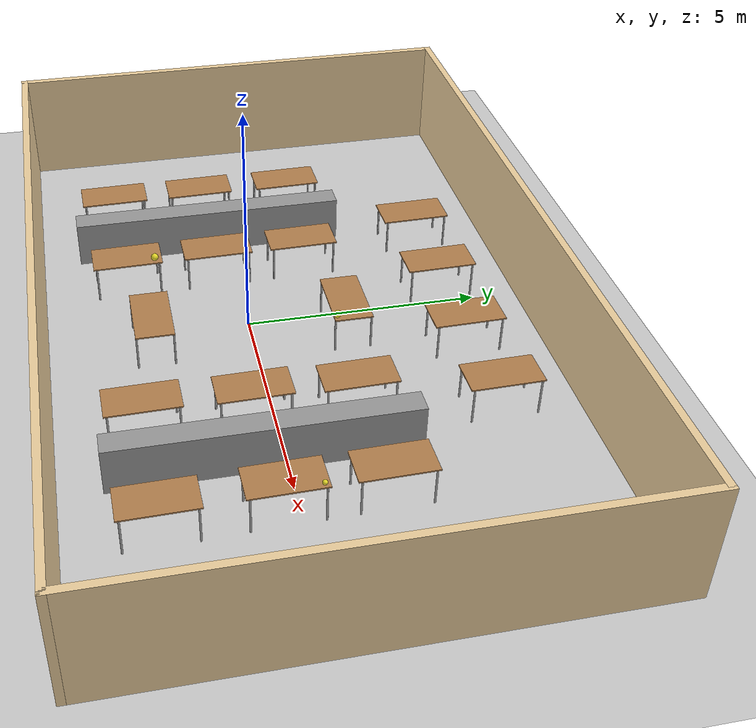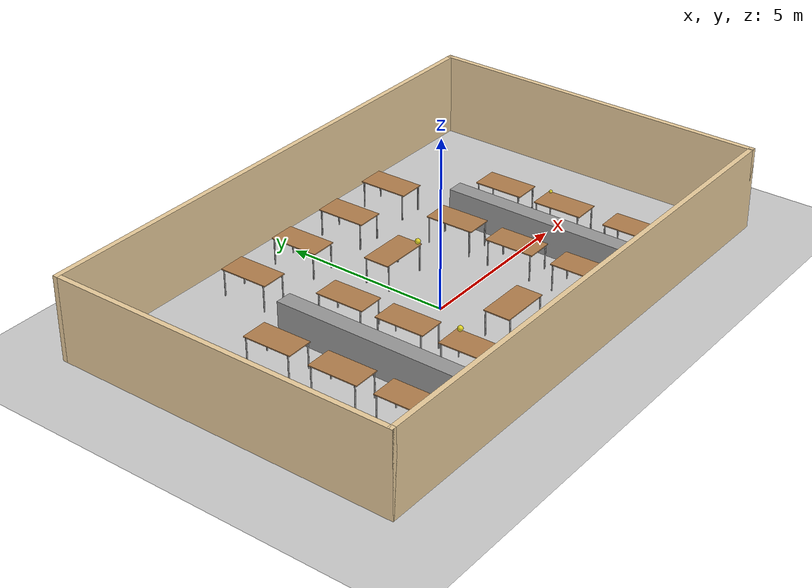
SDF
<sdf version="1.7">
 <world name="default">
  <light name="sun" type="directional">
   <pose>0 0 10 0 -0 0</pose>
   <diffuse>0.8 0.8 0.8 1</diffuse>
   <specular>0.2 0.2 0.2 1</specular>
   <attenuation>
    <range>1000</range>
    <constant>0.9</constant>
    <linear>0.01</linear>
    <quadratic>0.001</quadratic>
   </attenuation>
   <direction>-0.5 0.1 -0.9</direction>
   <spot><inner_angle>0</inner_angle><outer_angle>0</outer_angle><falloff>0</falloff></spot>
  </light>
  <model name="ground_plane">
   <static>1</static>
   <link name="link">
    <collision name="collision">
     <geometry><plane><normal>0 0 1</normal><size>100 100</size></plane></geometry>
     <surface>
      <contact><collide_bitmask>65535</collide_bitmask></contact>
      <friction><ode><mu>100</mu><mu2>50</mu2></ode></friction>
     </surface>
    </collision>
    <visual name="visual">
     <cast_shadows>0</cast_shadows>
     <geometry><plane><normal>0 0 1</normal><size>100 100</size></plane></geometry>
     <material>
      <script><uri>file://media/materials/scripts/gazebo.material</uri><name>Gazebo/Grey</name></script>
     </material>
    </visual>
   </link>
  </model>
  <gravity>0 0 -9.8</gravity>
  <magnetic_field>6e-06 2.3e-05 -4.2e-05</magnetic_field>
  <atmosphere type="adiabatic"/>
  <physics type="ode">
   <max_step_size>0.001</max_step_size>
   <real_time_factor>1</real_time_factor>
   <real_time_update_rate>1000</real_time_update_rate>
  </physics>
  <scene><ambient>0.4 0.4 0.4 1</ambient><background>0.7 0.7 0.7 1</background><shadows>1</shadows></scene>
  <audio><device>default</device></audio>
  <spherical_coordinates>
   <surface_model>EARTH_WGS84</surface_model>
   <latitude_deg>0</latitude_deg>
   <longitude_deg>0</longitude_deg>
   <elevation>0</elevation>
   <heading_deg>0</heading_deg>
  </spherical_coordinates>
  <model name="mapa_new">
   <pose>0.553189 0.87741 0 0 -0 0</pose>
   <link name="Wall_2">
    <collision name="Wall_2_Collision">
     <geometry><box><size>16.38 0.15 2.5</size></box></geometry>
     <pose>0 0 1.25 0 -0 0</pose>
    </collision>
    <visual name="Wall_2_Visual">
     <pose>0 0 1.25 0 -0 0</pose>
     <geometry><box><size>16.38 0.15 2.5</size></box></geometry>
     <material>
      <script><uri>file://media/materials/scripts/gazebo.material</uri><name>Gazebo/Grey</name></script>
      <ambient>0.921569 0.807843 0.615686 1</ambient>
     </material>
     <meta><layer>0</layer></meta>
    </visual>
    <pose>-0 5.175 0 0 -0 0</pose>
   </link>
   <link name="Wall_4">
    <collision name="Wall_4_Collision">
     <geometry><box><size>10.5 0.15 2.5</size></box></geometry>
     <pose>0 0 1.25 0 -0 0</pose>
    </collision>
    <visual name="Wall_4_Visual">
     <pose>0 0 1.25 0 -0 0</pose>
     <geometry><box><size>10.5 0.15 2.5</size></box></geometry>
     <material>
      <script><uri>file://media/materials/scripts/gazebo.material</uri><name>Gazebo/Grey</name></script>
      <ambient>0.921569 0.807843 0.615686 1</ambient>
     </material>
     <meta><layer>0</layer></meta>
    </visual>
    <pose>-8.115 0 0 0 -0 -1.5708</pose>
   </link>
   <link name="Wall_6">
    <collision name="Wall_6_Collision">
     <geometry><box><size>10.5 0.15 2.5</size></box></geometry>
     <pose>0 0 1.25 0 -0 0</pose>
    </collision>
    <visual name="Wall_6_Visual">
     <pose>0 0 1.25 0 -0 0</pose>
     <geometry><box><size>10.5 0.15 2.5</size></box></geometry>
     <material>
      <script><uri>file://media/materials/scripts/gazebo.material</uri><name>Gazebo/Grey</name></script>
      <ambient>0.921569 0.807843 0.615686 1</ambient>
     </material>
     <meta><layer>0</layer></meta>
    </visual>
    <pose>8.115 0 0 0 -0 -1.5708</pose>
   </link>
   <link name="Wall_8">
    <collision name="Wall_8_Collision">
     <geometry><box><size>16.38 0.15 2.5</size></box></geometry>
     <pose>0 0 1.25 0 -0 0</pose>
    </collision>
    <visual name="Wall_8_Visual">
     <pose>0 0 1.25 0 -0 0</pose>
     <geometry><box><size>16.38 0.15 2.5</size></box></geometry>
     <material>
      <script><uri>file://media/materials/scripts/gazebo.material</uri><name>Gazebo/Grey</name></script>
      <ambient>0.921569 0.807843 0.615686 1</ambient>
     </material>
     <meta><layer>0</layer></meta>
    </visual>
    <pose>-0 -5.175 0 0 -0 0</pose>
   </link>
   <static>1</static>
  </model>
  <model name="separador_pared">
   <pose>0.48579 -0.391509 0 0 -0 0</pose>
   <link name="Wall_0">
    <collision name="Wall_0_Collision">
     <geometry><box><size>6 0.5 1</size></box></geometry>
     <pose>0 0 0.5 0 -0 0</pose>
    </collision>
    <visual name="Wall_0_Visual">
     <pose>0 0 0.5 0 -0 0</pose>
     <geometry><box><size>6 0.5 1</size></box></geometry>
     <material>
      <script><uri>file://media/materials/scripts/gazebo.material</uri><name>Gazebo/Grey</name></script>
      <ambient>0.627451 0.580392 0.580392 1</ambient>
     </material>
     <meta><layer>0</layer></meta>
    </visual>
    <pose>3.7232 0.008937 0 0 -0 1.5708</pose>
   </link>
   <link name="Wall_2">
    <collision name="Wall_2_Collision">
     <geometry><box><size>6 0.5 1</size></box></geometry>
     <pose>0 0 0.5 0 -0 0</pose>
    </collision>
    <visual name="Wall_2_Visual">
     <pose>0 0 0.5 0 -0 0</pose>
     <geometry><box><size>6 0.5 1</size></box></geometry>
     <material>
      <script><uri>file://media/materials/scripts/gazebo.material</uri><name>Gazebo/Grey</name></script>
      <ambient>0.368627 0.360784 0.392157 1</ambient>
     </material>
     <meta><layer>0</layer></meta>
    </visual>
    <pose>-3.7232 -0.008937 0 0 -0 -1.5708</pose>
   </link>
   <static>1</static>
  </model>
  <model name="table_clone_clone">
   <link name="link">
    <inertial>
     <mass>1</mass>
     <pose>1.2 0 0.8 0 -0 0</pose>
     <inertia><ixx>1</ixx><ixy>0</ixy><ixz>0</ixz><iyy>1</iyy><iyz>0</iyz><izz>1</izz></inertia>
    </inertial>
    <visual name="back_right_leg">
     <pose>-0.68 -0.38 0.4 0 -0 0</pose>
     <geometry><cylinder><radius>0.02</radius><length>0.8</length></cylinder></geometry>
     <material>
      <script><uri>file://media/materials/scripts/gazebo.material</uri><name>Gazebo/Grey</name></script>
      <shader type="pixel"><normal_map>__default__</normal_map></shader>
      <ambient>0.3 0.3 0.3 1</ambient>
      <diffuse>0.7 0.7 0.7 1</diffuse>
      <specular>0.01 0.01 0.01 1</specular>
      <emissive>0 0 0 1</emissive>
     </material>
    </visual>
    <visual name="front_right_leg">
     <pose>0.68 -0.38 0.4 0 -0 0</pose>
     <geometry><cylinder><radius>0.02</radius><length>0.8</length></cylinder></geometry>
     <material>
      <script><uri>file://media/materials/scripts/gazebo.material</uri><name>Gazebo/Grey</name></script>
      <shader type="pixel"><normal_map>__default__</normal_map></shader>
      <ambient>0.3 0.3 0.3 1</ambient>
      <diffuse>0.7 0.7 0.7 1</diffuse>
      <specular>0.01 0.01 0.01 1</specular>
      <emissive>0 0 0 1</emissive>
     </material>
    </visual>
    <visual name="visual1">
     <pose>0 0 0.8 0 -0 0</pose>
     <geometry><box><size>1.5 0.8 0.03</size></box></geometry>
     <material>
      <script><uri>file://media/materials/scripts/gazebo.material</uri><name>Gazebo/Wood</name></script>
      <shader type="pixel"><normal_map>__default__</normal_map></shader>
      <ambient>1 1 1 1</ambient>
      <diffuse>1 1 1 1</diffuse>
      <specular>0.2 0.2 0.2 1</specular>
      <emissive>0 0 0 1</emissive>
     </material>
    </visual>
    <visual name="front_left_leg">
     <pose>0.68 0.38 0.4 0 -0 0</pose>
     <geometry><cylinder><radius>0.02</radius><length>0.8</length></cylinder></geometry>
     <material>
      <script><uri>file://media/materials/scripts/gazebo.material</uri><name>Gazebo/Grey</name></script>
      <shader type="pixel"><normal_map>__default__</normal_map></shader>
      <ambient>0.3 0.3 0.3 1</ambient>
      <diffuse>0.7 0.7 0.7 1</diffuse>
      <specular>0.01 0.01 0.01 1</specular>
      <emissive>0 0 0 1</emissive>
     </material>
    </visual>
    <visual name="back_left_leg">
     <pose>-0.68 0.38 0.4 0 -0 0</pose>
     <geometry><cylinder><radius>0.02</radius><length>0.8</length></cylinder></geometry>
     <material>
      <script><uri>file://media/materials/scripts/gazebo.material</uri><name>Gazebo/Grey</name></script>
      <shader type="pixel"><normal_map>__default__</normal_map></shader>
      <ambient>0.3 0.3 0.3 1</ambient>
      <diffuse>0.7 0.7 0.7 1</diffuse>
      <specular>0.01 0.01 0.01 1</specular>
      <emissive>0 0 0 1</emissive>
     </material>
    </visual>
    <collision name="back_right_leg">
     <pose>-0.68 -0.38 0.4 0 -0 0</pose>
     <geometry><cylinder><radius>0.02</radius><length>0.8</length></cylinder></geometry>
     <surface>
      <friction>
       <ode><mu>1</mu><mu2>1</mu2><fdir1>0 0 0</fdir1><slip1>0</slip1><slip2>0</slip2></ode>
       <torsional>
        <coefficient>1</coefficient>
        <patch_radius>0</patch_radius>
        <surface_radius>0</surface_radius>
        <use_patch_radius>1</use_patch_radius>
        <ode><slip>0</slip></ode>
       </torsional>
      </friction>
      <bounce><restitution_coefficient>0</restitution_coefficient><threshold>1e+06</threshold></bounce>
      <contact>
       <collide_without_contact>0</collide_without_contact>
       <collide_without_contact_bitmask>1</collide_without_contact_bitmask>
       <collide_bitmask>1</collide_bitmask>
       <ode>
        <soft_cfm>0</soft_cfm>
        <soft_erp>0.2</soft_erp>
        <kp>1e+13</kp>
        <kd>1</kd>
        <max_vel>0.01</max_vel>
        <min_depth>0</min_depth>
       </ode>
       <bullet>
        <split_impulse>1</split_impulse>
        <split_impulse_penetration_threshold>-0.01</split_impulse_penetration_threshold>
        <soft_cfm>0</soft_cfm>
        <soft_erp>0.2</soft_erp>
        <kp>1e+13</kp>
        <kd>1</kd>
       </bullet>
      </contact>
     </surface>
    </collision>
    <collision name="front_left_leg">
     <pose>0.68 0.38 0.4 0 -0 0</pose>
     <geometry><cylinder><radius>0.02</radius><length>0.8</length></cylinder></geometry>
     <surface>
      <friction>
       <ode><mu>1</mu><mu2>1</mu2><fdir1>0 0 0</fdir1><slip1>0</slip1><slip2>0</slip2></ode>
       <torsional>
        <coefficient>1</coefficient>
        <patch_radius>0</patch_radius>
        <surface_radius>0</surface_radius>
        <use_patch_radius>1</use_patch_radius>
        <ode><slip>0</slip></ode>
       </torsional>
      </friction>
      <bounce><restitution_coefficient>0</restitution_coefficient><threshold>1e+06</threshold></bounce>
      <contact>
       <collide_without_contact>0</collide_without_contact>
       <collide_without_contact_bitmask>1</collide_without_contact_bitmask>
       <collide_bitmask>1</collide_bitmask>
       <ode>
        <soft_cfm>0</soft_cfm>
        <soft_erp>0.2</soft_erp>
        <kp>1e+13</kp>
        <kd>1</kd>
        <max_vel>0.01</max_vel>
        <min_depth>0</min_depth>
       </ode>
       <bullet>
        <split_impulse>1</split_impulse>
        <split_impulse_penetration_threshold>-0.01</split_impulse_penetration_threshold>
        <soft_cfm>0</soft_cfm>
        <soft_erp>0.2</soft_erp>
        <kp>1e+13</kp>
        <kd>1</kd>
       </bullet>
      </contact>
     </surface>
    </collision>
    <collision name="back_left_leg">
     <pose>-0.68 0.38 0.4 0 -0 0</pose>
     <geometry><cylinder><radius>0.02</radius><length>0.8</length></cylinder></geometry>
     <surface>
      <friction>
       <ode><mu>1</mu><mu2>1</mu2><fdir1>0 0 0</fdir1><slip1>0</slip1><slip2>0</slip2></ode>
       <torsional>
        <coefficient>1</coefficient>
        <patch_radius>0</patch_radius>
        <surface_radius>0</surface_radius>
        <use_patch_radius>1</use_patch_radius>
        <ode><slip>0</slip></ode>
       </torsional>
      </friction>
      <bounce><restitution_coefficient>0</restitution_coefficient><threshold>1e+06</threshold></bounce>
      <contact>
       <collide_without_contact>0</collide_without_contact>
       <collide_without_contact_bitmask>1</collide_without_contact_bitmask>
       <collide_bitmask>1</collide_bitmask>
       <ode>
        <soft_cfm>0</soft_cfm>
        <soft_erp>0.2</soft_erp>
        <kp>1e+13</kp>
        <kd>1</kd>
        <max_vel>0.01</max_vel>
        <min_depth>0</min_depth>
       </ode>
       <bullet>
        <split_impulse>1</split_impulse>
        <split_impulse_penetration_threshold>-0.01</split_impulse_penetration_threshold>
        <soft_cfm>0</soft_cfm>
        <soft_erp>0.2</soft_erp>
        <kp>1e+13</kp>
        <kd>1</kd>
       </bullet>
      </contact>
     </surface>
    </collision>
    <collision name="surface">
     <pose>0 0 0.8 0 -0 0</pose>
     <geometry><box><size>1.5 0.8 0.03</size></box></geometry>
     <surface>
      <friction>
       <ode><mu>0.6</mu><mu2>0.6</mu2><fdir1>0 0 0</fdir1><slip1>0</slip1><slip2>0</slip2></ode>
       <torsional>
        <coefficient>1</coefficient>
        <patch_radius>0</patch_radius>
        <surface_radius>0</surface_radius>
        <use_patch_radius>1</use_patch_radius>
        <ode><slip>0</slip></ode>
       </torsional>
      </friction>
      <bounce><restitution_coefficient>0</restitution_coefficient><threshold>1e+06</threshold></bounce>
      <contact>
       <collide_without_contact>0</collide_without_contact>
       <collide_without_contact_bitmask>1</collide_without_contact_bitmask>
       <collide_bitmask>1</collide_bitmask>
       <ode>
        <soft_cfm>0</soft_cfm>
        <soft_erp>0.2</soft_erp>
        <kp>1e+13</kp>
        <kd>1</kd>
        <max_vel>0.01</max_vel>
        <min_depth>0</min_depth>
       </ode>
       <bullet>
        <split_impulse>1</split_impulse>
        <split_impulse_penetration_threshold>-0.01</split_impulse_penetration_threshold>
        <soft_cfm>0</soft_cfm>
        <soft_erp>0.2</soft_erp>
        <kp>1e+13</kp>
        <kd>1</kd>
       </bullet>
      </contact>
     </surface>
    </collision>
    <collision name="front_right_leg">
     <pose>0.68 -0.38 0.4 0 -0 0</pose>
     <geometry><cylinder><radius>0.02</radius><length>0.8</length></cylinder></geometry>
     <surface>
      <friction>
       <ode><mu>1</mu><mu2>1</mu2><fdir1>0 0 0</fdir1><slip1>0</slip1><slip2>0</slip2></ode>
       <torsional>
        <coefficient>1</coefficient>
        <patch_radius>0</patch_radius>
        <surface_radius>0</surface_radius>
        <use_patch_radius>1</use_patch_radius>
        <ode><slip>0</slip></ode>
       </torsional>
      </friction>
      <bounce><restitution_coefficient>0</restitution_coefficient><threshold>1e+06</threshold></bounce>
      <contact>
       <collide_without_contact>0</collide_without_contact>
       <collide_without_contact_bitmask>1</collide_without_contact_bitmask>
       <collide_bitmask>1</collide_bitmask>
       <ode>
        <soft_cfm>0</soft_cfm>
        <soft_erp>0.2</soft_erp>
        <kp>1e+13</kp>
        <kd>1</kd>
        <max_vel>0.01</max_vel>
        <min_depth>0</min_depth>
       </ode>
       <bullet>
        <split_impulse>1</split_impulse>
        <split_impulse_penetration_threshold>-0.01</split_impulse_penetration_threshold>
        <soft_cfm>0</soft_cfm>
        <soft_erp>0.2</soft_erp>
        <kp>1e+13</kp>
        <kd>1</kd>
       </bullet>
      </contact>
     </surface>
    </collision>
   </link>
   <static>1</static>
   <pose>1.49993 4.29823 0 0 0 -1.55553</pose>
  </model>
  <model name="table_clone_clone_0">
   <link name="link">
    <inertial>
     <mass>1</mass>
     <pose>1.2 0 0.8 0 -0 0</pose>
     <inertia><ixx>1</ixx><ixy>0</ixy><ixz>0</ixz><iyy>1</iyy><iyz>0</iyz><izz>1</izz></inertia>
    </inertial>
    <visual name="back_right_leg">
     <pose>-0.68 -0.38 0.4 0 -0 0</pose>
     <geometry><cylinder><radius>0.02</radius><length>0.8</length></cylinder></geometry>
     <material>
      <script><uri>file://media/materials/scripts/gazebo.material</uri><name>Gazebo/Grey</name></script>
      <shader type="pixel"><normal_map>__default__</normal_map></shader>
      <ambient>0.3 0.3 0.3 1</ambient>
      <diffuse>0.7 0.7 0.7 1</diffuse>
      <specular>0.01 0.01 0.01 1</specular>
      <emissive>0 0 0 1</emissive>
     </material>
    </visual>
    <visual name="front_right_leg">
     <pose>0.68 -0.38 0.4 0 -0 0</pose>
     <geometry><cylinder><radius>0.02</radius><length>0.8</length></cylinder></geometry>
     <material>
      <script><uri>file://media/materials/scripts/gazebo.material</uri><name>Gazebo/Grey</name></script>
      <shader type="pixel"><normal_map>__default__</normal_map></shader>
      <ambient>0.3 0.3 0.3 1</ambient>
      <diffuse>0.7 0.7 0.7 1</diffuse>
      <specular>0.01 0.01 0.01 1</specular>
      <emissive>0 0 0 1</emissive>
     </material>
    </visual>
    <visual name="visual1">
     <pose>0 0 0.8 0 -0 0</pose>
     <geometry><box><size>1.5 0.8 0.03</size></box></geometry>
     <material>
      <script><uri>file://media/materials/scripts/gazebo.material</uri><name>Gazebo/Wood</name></script>
      <shader type="pixel"><normal_map>__default__</normal_map></shader>
      <ambient>1 1 1 1</ambient>
      <diffuse>1 1 1 1</diffuse>
      <specular>0.2 0.2 0.2 1</specular>
      <emissive>0 0 0 1</emissive>
     </material>
    </visual>
    <visual name="front_left_leg">
     <pose>0.68 0.38 0.4 0 -0 0</pose>
     <geometry><cylinder><radius>0.02</radius><length>0.8</length></cylinder></geometry>
     <material>
      <script><uri>file://media/materials/scripts/gazebo.material</uri><name>Gazebo/Grey</name></script>
      <shader type="pixel"><normal_map>__default__</normal_map></shader>
      <ambient>0.3 0.3 0.3 1</ambient>
      <diffuse>0.7 0.7 0.7 1</diffuse>
      <specular>0.01 0.01 0.01 1</specular>
      <emissive>0 0 0 1</emissive>
     </material>
    </visual>
    <visual name="back_left_leg">
     <pose>-0.68 0.38 0.4 0 -0 0</pose>
     <geometry><cylinder><radius>0.02</radius><length>0.8</length></cylinder></geometry>
     <material>
      <script><uri>file://media/materials/scripts/gazebo.material</uri><name>Gazebo/Grey</name></script>
      <shader type="pixel"><normal_map>__default__</normal_map></shader>
      <ambient>0.3 0.3 0.3 1</ambient>
      <diffuse>0.7 0.7 0.7 1</diffuse>
      <specular>0.01 0.01 0.01 1</specular>
      <emissive>0 0 0 1</emissive>
     </material>
    </visual>
    <collision name="back_right_leg">
     <pose>-0.68 -0.38 0.4 0 -0 0</pose>
     <geometry><cylinder><radius>0.02</radius><length>0.8</length></cylinder></geometry>
     <surface>
      <friction>
       <ode><mu>1</mu><mu2>1</mu2><fdir1>0 0 0</fdir1><slip1>0</slip1><slip2>0</slip2></ode>
       <torsional>
        <coefficient>1</coefficient>
        <patch_radius>0</patch_radius>
        <surface_radius>0</surface_radius>
        <use_patch_radius>1</use_patch_radius>
        <ode><slip>0</slip></ode>
       </torsional>
      </friction>
      <bounce><restitution_coefficient>0</restitution_coefficient><threshold>1e+06</threshold></bounce>
      <contact>
       <collide_without_contact>0</collide_without_contact>
       <collide_without_contact_bitmask>1</collide_without_contact_bitmask>
       <collide_bitmask>1</collide_bitmask>
       <ode>
        <soft_cfm>0</soft_cfm>
        <soft_erp>0.2</soft_erp>
        <kp>1e+13</kp>
        <kd>1</kd>
        <max_vel>0.01</max_vel>
        <min_depth>0</min_depth>
       </ode>
       <bullet>
        <split_impulse>1</split_impulse>
        <split_impulse_penetration_threshold>-0.01</split_impulse_penetration_threshold>
        <soft_cfm>0</soft_cfm>
        <soft_erp>0.2</soft_erp>
        <kp>1e+13</kp>
        <kd>1</kd>
       </bullet>
      </contact>
     </surface>
    </collision>
    <collision name="front_left_leg">
     <pose>0.68 0.38 0.4 0 -0 0</pose>
     <geometry><cylinder><radius>0.02</radius><length>0.8</length></cylinder></geometry>
     <surface>
      <friction>
       <ode><mu>1</mu><mu2>1</mu2><fdir1>0 0 0</fdir1><slip1>0</slip1><slip2>0</slip2></ode>
       <torsional>
        <coefficient>1</coefficient>
        <patch_radius>0</patch_radius>
        <surface_radius>0</surface_radius>
        <use_patch_radius>1</use_patch_radius>
        <ode><slip>0</slip></ode>
       </torsional>
      </friction>
      <bounce><restitution_coefficient>0</restitution_coefficient><threshold>1e+06</threshold></bounce>
      <contact>
       <collide_without_contact>0</collide_without_contact>
       <collide_without_contact_bitmask>1</collide_without_contact_bitmask>
       <collide_bitmask>1</collide_bitmask>
       <ode>
        <soft_cfm>0</soft_cfm>
        <soft_erp>0.2</soft_erp>
        <kp>1e+13</kp>
        <kd>1</kd>
        <max_vel>0.01</max_vel>
        <min_depth>0</min_depth>
       </ode>
       <bullet>
        <split_impulse>1</split_impulse>
        <split_impulse_penetration_threshold>-0.01</split_impulse_penetration_threshold>
        <soft_cfm>0</soft_cfm>
        <soft_erp>0.2</soft_erp>
        <kp>1e+13</kp>
        <kd>1</kd>
       </bullet>
      </contact>
     </surface>
    </collision>
    <collision name="back_left_leg">
     <pose>-0.68 0.38 0.4 0 -0 0</pose>
     <geometry><cylinder><radius>0.02</radius><length>0.8</length></cylinder></geometry>
     <surface>
      <friction>
       <ode><mu>1</mu><mu2>1</mu2><fdir1>0 0 0</fdir1><slip1>0</slip1><slip2>0</slip2></ode>
       <torsional>
        <coefficient>1</coefficient>
        <patch_radius>0</patch_radius>
        <surface_radius>0</surface_radius>
        <use_patch_radius>1</use_patch_radius>
        <ode><slip>0</slip></ode>
       </torsional>
      </friction>
      <bounce><restitution_coefficient>0</restitution_coefficient><threshold>1e+06</threshold></bounce>
      <contact>
       <collide_without_contact>0</collide_without_contact>
       <collide_without_contact_bitmask>1</collide_without_contact_bitmask>
       <collide_bitmask>1</collide_bitmask>
       <ode>
        <soft_cfm>0</soft_cfm>
        <soft_erp>0.2</soft_erp>
        <kp>1e+13</kp>
        <kd>1</kd>
        <max_vel>0.01</max_vel>
        <min_depth>0</min_depth>
       </ode>
       <bullet>
        <split_impulse>1</split_impulse>
        <split_impulse_penetration_threshold>-0.01</split_impulse_penetration_threshold>
        <soft_cfm>0</soft_cfm>
        <soft_erp>0.2</soft_erp>
        <kp>1e+13</kp>
        <kd>1</kd>
       </bullet>
      </contact>
     </surface>
    </collision>
    <collision name="surface">
     <pose>0 0 0.8 0 -0 0</pose>
     <geometry><box><size>1.5 0.8 0.03</size></box></geometry>
     <surface>
      <friction>
       <ode><mu>0.6</mu><mu2>0.6</mu2><fdir1>0 0 0</fdir1><slip1>0</slip1><slip2>0</slip2></ode>
       <torsional>
        <coefficient>1</coefficient>
        <patch_radius>0</patch_radius>
        <surface_radius>0</surface_radius>
        <use_patch_radius>1</use_patch_radius>
        <ode><slip>0</slip></ode>
       </torsional>
      </friction>
      <bounce><restitution_coefficient>0</restitution_coefficient><threshold>1e+06</threshold></bounce>
      <contact>
       <collide_without_contact>0</collide_without_contact>
       <collide_without_contact_bitmask>1</collide_without_contact_bitmask>
       <collide_bitmask>1</collide_bitmask>
       <ode>
        <soft_cfm>0</soft_cfm>
        <soft_erp>0.2</soft_erp>
        <kp>1e+13</kp>
        <kd>1</kd>
        <max_vel>0.01</max_vel>
        <min_depth>0</min_depth>
       </ode>
       <bullet>
        <split_impulse>1</split_impulse>
        <split_impulse_penetration_threshold>-0.01</split_impulse_penetration_threshold>
        <soft_cfm>0</soft_cfm>
        <soft_erp>0.2</soft_erp>
        <kp>1e+13</kp>
        <kd>1</kd>
       </bullet>
      </contact>
     </surface>
    </collision>
    <collision name="front_right_leg">
     <pose>0.68 -0.38 0.4 0 -0 0</pose>
     <geometry><cylinder><radius>0.02</radius><length>0.8</length></cylinder></geometry>
     <surface>
      <friction>
       <ode><mu>1</mu><mu2>1</mu2><fdir1>0 0 0</fdir1><slip1>0</slip1><slip2>0</slip2></ode>
       <torsional>
        <coefficient>1</coefficient>
        <patch_radius>0</patch_radius>
        <surface_radius>0</surface_radius>
        <use_patch_radius>1</use_patch_radius>
        <ode><slip>0</slip></ode>
       </torsional>
      </friction>
      <bounce><restitution_coefficient>0</restitution_coefficient><threshold>1e+06</threshold></bounce>
      <contact>
       <collide_without_contact>0</collide_without_contact>
       <collide_without_contact_bitmask>1</collide_without_contact_bitmask>
       <collide_bitmask>1</collide_bitmask>
       <ode>
        <soft_cfm>0</soft_cfm>
        <soft_erp>0.2</soft_erp>
        <kp>1e+13</kp>
        <kd>1</kd>
        <max_vel>0.01</max_vel>
        <min_depth>0</min_depth>
       </ode>
       <bullet>
        <split_impulse>1</split_impulse>
        <split_impulse_penetration_threshold>-0.01</split_impulse_penetration_threshold>
        <soft_cfm>0</soft_cfm>
        <soft_erp>0.2</soft_erp>
        <kp>1e+13</kp>
        <kd>1</kd>
       </bullet>
      </contact>
     </surface>
    </collision>
   </link>
   <static>1</static>
   <pose>3.51901 4.38519 0 0 0 -1.55553</pose>
  </model>
  <model name="table_clone_clone_1">
   <link name="link">
    <inertial>
     <mass>1</mass>
     <pose>1.2 0 0.8 0 -0 0</pose>
     <inertia><ixx>1</ixx><ixy>0</ixy><ixz>0</ixz><iyy>1</iyy><iyz>0</iyz><izz>1</izz></inertia>
    </inertial>
    <visual name="back_right_leg">
     <pose>-0.68 -0.38 0.4 0 -0 0</pose>
     <geometry><cylinder><radius>0.02</radius><length>0.8</length></cylinder></geometry>
     <material>
      <script><uri>file://media/materials/scripts/gazebo.material</uri><name>Gazebo/Grey</name></script>
      <shader type="pixel"><normal_map>__default__</normal_map></shader>
      <ambient>0.3 0.3 0.3 1</ambient>
      <diffuse>0.7 0.7 0.7 1</diffuse>
      <specular>0.01 0.01 0.01 1</specular>
      <emissive>0 0 0 1</emissive>
     </material>
    </visual>
    <visual name="front_right_leg">
     <pose>0.68 -0.38 0.4 0 -0 0</pose>
     <geometry><cylinder><radius>0.02</radius><length>0.8</length></cylinder></geometry>
     <material>
      <script><uri>file://media/materials/scripts/gazebo.material</uri><name>Gazebo/Grey</name></script>
      <shader type="pixel"><normal_map>__default__</normal_map></shader>
      <ambient>0.3 0.3 0.3 1</ambient>
      <diffuse>0.7 0.7 0.7 1</diffuse>
      <specular>0.01 0.01 0.01 1</specular>
      <emissive>0 0 0 1</emissive>
     </material>
    </visual>
    <visual name="visual1">
     <pose>0 0 0.8 0 -0 0</pose>
     <geometry><box><size>1.5 0.8 0.03</size></box></geometry>
     <material>
      <script><uri>file://media/materials/scripts/gazebo.material</uri><name>Gazebo/Wood</name></script>
      <shader type="pixel"><normal_map>__default__</normal_map></shader>
      <ambient>1 1 1 1</ambient>
      <diffuse>1 1 1 1</diffuse>
      <specular>0.2 0.2 0.2 1</specular>
      <emissive>0 0 0 1</emissive>
     </material>
    </visual>
    <visual name="front_left_leg">
     <pose>0.68 0.38 0.4 0 -0 0</pose>
     <geometry><cylinder><radius>0.02</radius><length>0.8</length></cylinder></geometry>
     <material>
      <script><uri>file://media/materials/scripts/gazebo.material</uri><name>Gazebo/Grey</name></script>
      <shader type="pixel"><normal_map>__default__</normal_map></shader>
      <ambient>0.3 0.3 0.3 1</ambient>
      <diffuse>0.7 0.7 0.7 1</diffuse>
      <specular>0.01 0.01 0.01 1</specular>
      <emissive>0 0 0 1</emissive>
     </material>
    </visual>
    <visual name="back_left_leg">
     <pose>-0.68 0.38 0.4 0 -0 0</pose>
     <geometry><cylinder><radius>0.02</radius><length>0.8</length></cylinder></geometry>
     <material>
      <script><uri>file://media/materials/scripts/gazebo.material</uri><name>Gazebo/Grey</name></script>
      <shader type="pixel"><normal_map>__default__</normal_map></shader>
      <ambient>0.3 0.3 0.3 1</ambient>
      <diffuse>0.7 0.7 0.7 1</diffuse>
      <specular>0.01 0.01 0.01 1</specular>
      <emissive>0 0 0 1</emissive>
     </material>
    </visual>
    <collision name="back_right_leg">
     <pose>-0.68 -0.38 0.4 0 -0 0</pose>
     <geometry><cylinder><radius>0.02</radius><length>0.8</length></cylinder></geometry>
     <surface>
      <friction>
       <ode><mu>1</mu><mu2>1</mu2><fdir1>0 0 0</fdir1><slip1>0</slip1><slip2>0</slip2></ode>
       <torsional>
        <coefficient>1</coefficient>
        <patch_radius>0</patch_radius>
        <surface_radius>0</surface_radius>
        <use_patch_radius>1</use_patch_radius>
        <ode><slip>0</slip></ode>
       </torsional>
      </friction>
      <bounce><restitution_coefficient>0</restitution_coefficient><threshold>1e+06</threshold></bounce>
      <contact>
       <collide_without_contact>0</collide_without_contact>
       <collide_without_contact_bitmask>1</collide_without_contact_bitmask>
       <collide_bitmask>1</collide_bitmask>
       <ode>
        <soft_cfm>0</soft_cfm>
        <soft_erp>0.2</soft_erp>
        <kp>1e+13</kp>
        <kd>1</kd>
        <max_vel>0.01</max_vel>
        <min_depth>0</min_depth>
       </ode>
       <bullet>
        <split_impulse>1</split_impulse>
        <split_impulse_penetration_threshold>-0.01</split_impulse_penetration_threshold>
        <soft_cfm>0</soft_cfm>
        <soft_erp>0.2</soft_erp>
        <kp>1e+13</kp>
        <kd>1</kd>
       </bullet>
      </contact>
     </surface>
    </collision>
    <collision name="front_left_leg">
     <pose>0.68 0.38 0.4 0 -0 0</pose>
     <geometry><cylinder><radius>0.02</radius><length>0.8</length></cylinder></geometry>
     <surface>
      <friction>
       <ode><mu>1</mu><mu2>1</mu2><fdir1>0 0 0</fdir1><slip1>0</slip1><slip2>0</slip2></ode>
       <torsional>
        <coefficient>1</coefficient>
        <patch_radius>0</patch_radius>
        <surface_radius>0</surface_radius>
        <use_patch_radius>1</use_patch_radius>
        <ode><slip>0</slip></ode>
       </torsional>
      </friction>
      <bounce><restitution_coefficient>0</restitution_coefficient><threshold>1e+06</threshold></bounce>
      <contact>
       <collide_without_contact>0</collide_without_contact>
       <collide_without_contact_bitmask>1</collide_without_contact_bitmask>
       <collide_bitmask>1</collide_bitmask>
       <ode>
        <soft_cfm>0</soft_cfm>
        <soft_erp>0.2</soft_erp>
        <kp>1e+13</kp>
        <kd>1</kd>
        <max_vel>0.01</max_vel>
        <min_depth>0</min_depth>
       </ode>
       <bullet>
        <split_impulse>1</split_impulse>
        <split_impulse_penetration_threshold>-0.01</split_impulse_penetration_threshold>
        <soft_cfm>0</soft_cfm>
        <soft_erp>0.2</soft_erp>
        <kp>1e+13</kp>
        <kd>1</kd>
       </bullet>
      </contact>
     </surface>
    </collision>
    <collision name="back_left_leg">
     <pose>-0.68 0.38 0.4 0 -0 0</pose>
     <geometry><cylinder><radius>0.02</radius><length>0.8</length></cylinder></geometry>
     <surface>
      <friction>
       <ode><mu>1</mu><mu2>1</mu2><fdir1>0 0 0</fdir1><slip1>0</slip1><slip2>0</slip2></ode>
       <torsional>
        <coefficient>1</coefficient>
        <patch_radius>0</patch_radius>
        <surface_radius>0</surface_radius>
        <use_patch_radius>1</use_patch_radius>
        <ode><slip>0</slip></ode>
       </torsional>
      </friction>
      <bounce><restitution_coefficient>0</restitution_coefficient><threshold>1e+06</threshold></bounce>
      <contact>
       <collide_without_contact>0</collide_without_contact>
       <collide_without_contact_bitmask>1</collide_without_contact_bitmask>
       <collide_bitmask>1</collide_bitmask>
       <ode>
        <soft_cfm>0</soft_cfm>
        <soft_erp>0.2</soft_erp>
        <kp>1e+13</kp>
        <kd>1</kd>
        <max_vel>0.01</max_vel>
        <min_depth>0</min_depth>
       </ode>
       <bullet>
        <split_impulse>1</split_impulse>
        <split_impulse_penetration_threshold>-0.01</split_impulse_penetration_threshold>
        <soft_cfm>0</soft_cfm>
        <soft_erp>0.2</soft_erp>
        <kp>1e+13</kp>
        <kd>1</kd>
       </bullet>
      </contact>
     </surface>
    </collision>
    <collision name="surface">
     <pose>0 0 0.8 0 -0 0</pose>
     <geometry><box><size>1.5 0.8 0.03</size></box></geometry>
     <surface>
      <friction>
       <ode><mu>0.6</mu><mu2>0.6</mu2><fdir1>0 0 0</fdir1><slip1>0</slip1><slip2>0</slip2></ode>
       <torsional>
        <coefficient>1</coefficient>
        <patch_radius>0</patch_radius>
        <surface_radius>0</surface_radius>
        <use_patch_radius>1</use_patch_radius>
        <ode><slip>0</slip></ode>
       </torsional>
      </friction>
      <bounce><restitution_coefficient>0</restitution_coefficient><threshold>1e+06</threshold></bounce>
      <contact>
       <collide_without_contact>0</collide_without_contact>
       <collide_without_contact_bitmask>1</collide_without_contact_bitmask>
       <collide_bitmask>1</collide_bitmask>
       <ode>
        <soft_cfm>0</soft_cfm>
        <soft_erp>0.2</soft_erp>
        <kp>1e+13</kp>
        <kd>1</kd>
        <max_vel>0.01</max_vel>
        <min_depth>0</min_depth>
       </ode>
       <bullet>
        <split_impulse>1</split_impulse>
        <split_impulse_penetration_threshold>-0.01</split_impulse_penetration_threshold>
        <soft_cfm>0</soft_cfm>
        <soft_erp>0.2</soft_erp>
        <kp>1e+13</kp>
        <kd>1</kd>
       </bullet>
      </contact>
     </surface>
    </collision>
    <collision name="front_right_leg">
     <pose>0.68 -0.38 0.4 0 -0 0</pose>
     <geometry><cylinder><radius>0.02</radius><length>0.8</length></cylinder></geometry>
     <surface>
      <friction>
       <ode><mu>1</mu><mu2>1</mu2><fdir1>0 0 0</fdir1><slip1>0</slip1><slip2>0</slip2></ode>
       <torsional>
        <coefficient>1</coefficient>
        <patch_radius>0</patch_radius>
        <surface_radius>0</surface_radius>
        <use_patch_radius>1</use_patch_radius>
        <ode><slip>0</slip></ode>
       </torsional>
      </friction>
      <bounce><restitution_coefficient>0</restitution_coefficient><threshold>1e+06</threshold></bounce>
      <contact>
       <collide_without_contact>0</collide_without_contact>
       <collide_without_contact_bitmask>1</collide_without_contact_bitmask>
       <collide_bitmask>1</collide_bitmask>
       <ode>
        <soft_cfm>0</soft_cfm>
        <soft_erp>0.2</soft_erp>
        <kp>1e+13</kp>
        <kd>1</kd>
        <max_vel>0.01</max_vel>
        <min_depth>0</min_depth>
       </ode>
       <bullet>
        <split_impulse>1</split_impulse>
        <split_impulse_penetration_threshold>-0.01</split_impulse_penetration_threshold>
        <soft_cfm>0</soft_cfm>
        <soft_erp>0.2</soft_erp>
        <kp>1e+13</kp>
        <kd>1</kd>
       </bullet>
      </contact>
     </surface>
    </collision>
   </link>
   <static>1</static>
   <pose>-2.51872 4.29115 0 0 0 -1.55553</pose>
  </model>
  <model name="table_clone_clone_2">
   <link name="link">
    <inertial>
     <mass>1</mass>
     <pose>1.2 0 0.8 0 -0 0</pose>
     <inertia><ixx>1</ixx><ixy>0</ixy><ixz>0</ixz><iyy>1</iyy><iyz>0</iyz><izz>1</izz></inertia>
    </inertial>
    <visual name="back_right_leg">
     <pose>-0.68 -0.38 0.4 0 -0 0</pose>
     <geometry><cylinder><radius>0.02</radius><length>0.8</length></cylinder></geometry>
     <material>
      <script><uri>file://media/materials/scripts/gazebo.material</uri><name>Gazebo/Grey</name></script>
      <shader type="pixel"><normal_map>__default__</normal_map></shader>
      <ambient>0.3 0.3 0.3 1</ambient>
      <diffuse>0.7 0.7 0.7 1</diffuse>
      <specular>0.01 0.01 0.01 1</specular>
      <emissive>0 0 0 1</emissive>
     </material>
    </visual>
    <visual name="front_right_leg">
     <pose>0.68 -0.38 0.4 0 -0 0</pose>
     <geometry><cylinder><radius>0.02</radius><length>0.8</length></cylinder></geometry>
     <material>
      <script><uri>file://media/materials/scripts/gazebo.material</uri><name>Gazebo/Grey</name></script>
      <shader type="pixel"><normal_map>__default__</normal_map></shader>
      <ambient>0.3 0.3 0.3 1</ambient>
      <diffuse>0.7 0.7 0.7 1</diffuse>
      <specular>0.01 0.01 0.01 1</specular>
      <emissive>0 0 0 1</emissive>
     </material>
    </visual>
    <visual name="visual1">
     <pose>0 0 0.8 0 -0 0</pose>
     <geometry><box><size>1.5 0.8 0.03</size></box></geometry>
     <material>
      <script><uri>file://media/materials/scripts/gazebo.material</uri><name>Gazebo/Wood</name></script>
      <shader type="pixel"><normal_map>__default__</normal_map></shader>
      <ambient>1 1 1 1</ambient>
      <diffuse>1 1 1 1</diffuse>
      <specular>0.2 0.2 0.2 1</specular>
      <emissive>0 0 0 1</emissive>
     </material>
    </visual>
    <visual name="front_left_leg">
     <pose>0.68 0.38 0.4 0 -0 0</pose>
     <geometry><cylinder><radius>0.02</radius><length>0.8</length></cylinder></geometry>
     <material>
      <script><uri>file://media/materials/scripts/gazebo.material</uri><name>Gazebo/Grey</name></script>
      <shader type="pixel"><normal_map>__default__</normal_map></shader>
      <ambient>0.3 0.3 0.3 1</ambient>
      <diffuse>0.7 0.7 0.7 1</diffuse>
      <specular>0.01 0.01 0.01 1</specular>
      <emissive>0 0 0 1</emissive>
     </material>
    </visual>
    <visual name="back_left_leg">
     <pose>-0.68 0.38 0.4 0 -0 0</pose>
     <geometry><cylinder><radius>0.02</radius><length>0.8</length></cylinder></geometry>
     <material>
      <script><uri>file://media/materials/scripts/gazebo.material</uri><name>Gazebo/Grey</name></script>
      <shader type="pixel"><normal_map>__default__</normal_map></shader>
      <ambient>0.3 0.3 0.3 1</ambient>
      <diffuse>0.7 0.7 0.7 1</diffuse>
      <specular>0.01 0.01 0.01 1</specular>
      <emissive>0 0 0 1</emissive>
     </material>
    </visual>
    <collision name="back_right_leg">
     <pose>-0.68 -0.38 0.4 0 -0 0</pose>
     <geometry><cylinder><radius>0.02</radius><length>0.8</length></cylinder></geometry>
     <surface>
      <friction>
       <ode><mu>1</mu><mu2>1</mu2><fdir1>0 0 0</fdir1><slip1>0</slip1><slip2>0</slip2></ode>
       <torsional>
        <coefficient>1</coefficient>
        <patch_radius>0</patch_radius>
        <surface_radius>0</surface_radius>
        <use_patch_radius>1</use_patch_radius>
        <ode><slip>0</slip></ode>
       </torsional>
      </friction>
      <bounce><restitution_coefficient>0</restitution_coefficient><threshold>1e+06</threshold></bounce>
      <contact>
       <collide_without_contact>0</collide_without_contact>
       <collide_without_contact_bitmask>1</collide_without_contact_bitmask>
       <collide_bitmask>1</collide_bitmask>
       <ode>
        <soft_cfm>0</soft_cfm>
        <soft_erp>0.2</soft_erp>
        <kp>1e+13</kp>
        <kd>1</kd>
        <max_vel>0.01</max_vel>
        <min_depth>0</min_depth>
       </ode>
       <bullet>
        <split_impulse>1</split_impulse>
        <split_impulse_penetration_threshold>-0.01</split_impulse_penetration_threshold>
        <soft_cfm>0</soft_cfm>
        <soft_erp>0.2</soft_erp>
        <kp>1e+13</kp>
        <kd>1</kd>
       </bullet>
      </contact>
     </surface>
    </collision>
    <collision name="front_left_leg">
     <pose>0.68 0.38 0.4 0 -0 0</pose>
     <geometry><cylinder><radius>0.02</radius><length>0.8</length></cylinder></geometry>
     <surface>
      <friction>
       <ode><mu>1</mu><mu2>1</mu2><fdir1>0 0 0</fdir1><slip1>0</slip1><slip2>0</slip2></ode>
       <torsional>
        <coefficient>1</coefficient>
        <patch_radius>0</patch_radius>
        <surface_radius>0</surface_radius>
        <use_patch_radius>1</use_patch_radius>
        <ode><slip>0</slip></ode>
       </torsional>
      </friction>
      <bounce><restitution_coefficient>0</restitution_coefficient><threshold>1e+06</threshold></bounce>
      <contact>
       <collide_without_contact>0</collide_without_contact>
       <collide_without_contact_bitmask>1</collide_without_contact_bitmask>
       <collide_bitmask>1</collide_bitmask>
       <ode>
        <soft_cfm>0</soft_cfm>
        <soft_erp>0.2</soft_erp>
        <kp>1e+13</kp>
        <kd>1</kd>
        <max_vel>0.01</max_vel>
        <min_depth>0</min_depth>
       </ode>
       <bullet>
        <split_impulse>1</split_impulse>
        <split_impulse_penetration_threshold>-0.01</split_impulse_penetration_threshold>
        <soft_cfm>0</soft_cfm>
        <soft_erp>0.2</soft_erp>
        <kp>1e+13</kp>
        <kd>1</kd>
       </bullet>
      </contact>
     </surface>
    </collision>
    <collision name="back_left_leg">
     <pose>-0.68 0.38 0.4 0 -0 0</pose>
     <geometry><cylinder><radius>0.02</radius><length>0.8</length></cylinder></geometry>
     <surface>
      <friction>
       <ode><mu>1</mu><mu2>1</mu2><fdir1>0 0 0</fdir1><slip1>0</slip1><slip2>0</slip2></ode>
       <torsional>
        <coefficient>1</coefficient>
        <patch_radius>0</patch_radius>
        <surface_radius>0</surface_radius>
        <use_patch_radius>1</use_patch_radius>
        <ode><slip>0</slip></ode>
       </torsional>
      </friction>
      <bounce><restitution_coefficient>0</restitution_coefficient><threshold>1e+06</threshold></bounce>
      <contact>
       <collide_without_contact>0</collide_without_contact>
       <collide_without_contact_bitmask>1</collide_without_contact_bitmask>
       <collide_bitmask>1</collide_bitmask>
       <ode>
        <soft_cfm>0</soft_cfm>
        <soft_erp>0.2</soft_erp>
        <kp>1e+13</kp>
        <kd>1</kd>
        <max_vel>0.01</max_vel>
        <min_depth>0</min_depth>
       </ode>
       <bullet>
        <split_impulse>1</split_impulse>
        <split_impulse_penetration_threshold>-0.01</split_impulse_penetration_threshold>
        <soft_cfm>0</soft_cfm>
        <soft_erp>0.2</soft_erp>
        <kp>1e+13</kp>
        <kd>1</kd>
       </bullet>
      </contact>
     </surface>
    </collision>
    <collision name="surface">
     <pose>0 0 0.8 0 -0 0</pose>
     <geometry><box><size>1.5 0.8 0.03</size></box></geometry>
     <surface>
      <friction>
       <ode><mu>0.6</mu><mu2>0.6</mu2><fdir1>0 0 0</fdir1><slip1>0</slip1><slip2>0</slip2></ode>
       <torsional>
        <coefficient>1</coefficient>
        <patch_radius>0</patch_radius>
        <surface_radius>0</surface_radius>
        <use_patch_radius>1</use_patch_radius>
        <ode><slip>0</slip></ode>
       </torsional>
      </friction>
      <bounce><restitution_coefficient>0</restitution_coefficient><threshold>1e+06</threshold></bounce>
      <contact>
       <collide_without_contact>0</collide_without_contact>
       <collide_without_contact_bitmask>1</collide_without_contact_bitmask>
       <collide_bitmask>1</collide_bitmask>
       <ode>
        <soft_cfm>0</soft_cfm>
        <soft_erp>0.2</soft_erp>
        <kp>1e+13</kp>
        <kd>1</kd>
        <max_vel>0.01</max_vel>
        <min_depth>0</min_depth>
       </ode>
       <bullet>
        <split_impulse>1</split_impulse>
        <split_impulse_penetration_threshold>-0.01</split_impulse_penetration_threshold>
        <soft_cfm>0</soft_cfm>
        <soft_erp>0.2</soft_erp>
        <kp>1e+13</kp>
        <kd>1</kd>
       </bullet>
      </contact>
     </surface>
    </collision>
    <collision name="front_right_leg">
     <pose>0.68 -0.38 0.4 0 -0 0</pose>
     <geometry><cylinder><radius>0.02</radius><length>0.8</length></cylinder></geometry>
     <surface>
      <friction>
       <ode><mu>1</mu><mu2>1</mu2><fdir1>0 0 0</fdir1><slip1>0</slip1><slip2>0</slip2></ode>
       <torsional>
        <coefficient>1</coefficient>
        <patch_radius>0</patch_radius>
        <surface_radius>0</surface_radius>
        <use_patch_radius>1</use_patch_radius>
        <ode><slip>0</slip></ode>
       </torsional>
      </friction>
      <bounce><restitution_coefficient>0</restitution_coefficient><threshold>1e+06</threshold></bounce>
      <contact>
       <collide_without_contact>0</collide_without_contact>
       <collide_without_contact_bitmask>1</collide_without_contact_bitmask>
       <collide_bitmask>1</collide_bitmask>
       <ode>
        <soft_cfm>0</soft_cfm>
        <soft_erp>0.2</soft_erp>
        <kp>1e+13</kp>
        <kd>1</kd>
        <max_vel>0.01</max_vel>
        <min_depth>0</min_depth>
       </ode>
       <bullet>
        <split_impulse>1</split_impulse>
        <split_impulse_penetration_threshold>-0.01</split_impulse_penetration_threshold>
        <soft_cfm>0</soft_cfm>
        <soft_erp>0.2</soft_erp>
        <kp>1e+13</kp>
        <kd>1</kd>
       </bullet>
      </contact>
     </surface>
    </collision>
   </link>
   <static>1</static>
   <pose>-1.93807 1.51938 0 0 0 -1.55553</pose>
  </model>
  <model name="table_clone_clone_3">
   <link name="link">
    <inertial>
     <mass>1</mass>
     <pose>1.2 0 0.8 0 -0 0</pose>
     <inertia><ixx>1</ixx><ixy>0</ixy><ixz>0</ixz><iyy>1</iyy><iyz>0</iyz><izz>1</izz></inertia>
    </inertial>
    <visual name="back_right_leg">
     <pose>-0.68 -0.38 0.4 0 -0 0</pose>
     <geometry><cylinder><radius>0.02</radius><length>0.8</length></cylinder></geometry>
     <material>
      <script><uri>file://media/materials/scripts/gazebo.material</uri><name>Gazebo/Grey</name></script>
      <shader type="pixel"><normal_map>__default__</normal_map></shader>
      <ambient>0.3 0.3 0.3 1</ambient>
      <diffuse>0.7 0.7 0.7 1</diffuse>
      <specular>0.01 0.01 0.01 1</specular>
      <emissive>0 0 0 1</emissive>
     </material>
    </visual>
    <visual name="front_right_leg">
     <pose>0.68 -0.38 0.4 0 -0 0</pose>
     <geometry><cylinder><radius>0.02</radius><length>0.8</length></cylinder></geometry>
     <material>
      <script><uri>file://media/materials/scripts/gazebo.material</uri><name>Gazebo/Grey</name></script>
      <shader type="pixel"><normal_map>__default__</normal_map></shader>
      <ambient>0.3 0.3 0.3 1</ambient>
      <diffuse>0.7 0.7 0.7 1</diffuse>
      <specular>0.01 0.01 0.01 1</specular>
      <emissive>0 0 0 1</emissive>
     </material>
    </visual>
    <visual name="visual1">
     <pose>0 0 0.8 0 -0 0</pose>
     <geometry><box><size>1.5 0.8 0.03</size></box></geometry>
     <material>
      <script><uri>file://media/materials/scripts/gazebo.material</uri><name>Gazebo/Wood</name></script>
      <shader type="pixel"><normal_map>__default__</normal_map></shader>
      <ambient>1 1 1 1</ambient>
      <diffuse>1 1 1 1</diffuse>
      <specular>0.2 0.2 0.2 1</specular>
      <emissive>0 0 0 1</emissive>
     </material>
    </visual>
    <visual name="front_left_leg">
     <pose>0.68 0.38 0.4 0 -0 0</pose>
     <geometry><cylinder><radius>0.02</radius><length>0.8</length></cylinder></geometry>
     <material>
      <script><uri>file://media/materials/scripts/gazebo.material</uri><name>Gazebo/Grey</name></script>
      <shader type="pixel"><normal_map>__default__</normal_map></shader>
      <ambient>0.3 0.3 0.3 1</ambient>
      <diffuse>0.7 0.7 0.7 1</diffuse>
      <specular>0.01 0.01 0.01 1</specular>
      <emissive>0 0 0 1</emissive>
     </material>
    </visual>
    <visual name="back_left_leg">
     <pose>-0.68 0.38 0.4 0 -0 0</pose>
     <geometry><cylinder><radius>0.02</radius><length>0.8</length></cylinder></geometry>
     <material>
      <script><uri>file://media/materials/scripts/gazebo.material</uri><name>Gazebo/Grey</name></script>
      <shader type="pixel"><normal_map>__default__</normal_map></shader>
      <ambient>0.3 0.3 0.3 1</ambient>
      <diffuse>0.7 0.7 0.7 1</diffuse>
      <specular>0.01 0.01 0.01 1</specular>
      <emissive>0 0 0 1</emissive>
     </material>
    </visual>
    <collision name="back_right_leg">
     <pose>-0.68 -0.38 0.4 0 -0 0</pose>
     <geometry><cylinder><radius>0.02</radius><length>0.8</length></cylinder></geometry>
     <surface>
      <friction>
       <ode><mu>1</mu><mu2>1</mu2><fdir1>0 0 0</fdir1><slip1>0</slip1><slip2>0</slip2></ode>
       <torsional>
        <coefficient>1</coefficient>
        <patch_radius>0</patch_radius>
        <surface_radius>0</surface_radius>
        <use_patch_radius>1</use_patch_radius>
        <ode><slip>0</slip></ode>
       </torsional>
      </friction>
      <bounce><restitution_coefficient>0</restitution_coefficient><threshold>1e+06</threshold></bounce>
      <contact>
       <collide_without_contact>0</collide_without_contact>
       <collide_without_contact_bitmask>1</collide_without_contact_bitmask>
       <collide_bitmask>1</collide_bitmask>
       <ode>
        <soft_cfm>0</soft_cfm>
        <soft_erp>0.2</soft_erp>
        <kp>1e+13</kp>
        <kd>1</kd>
        <max_vel>0.01</max_vel>
        <min_depth>0</min_depth>
       </ode>
       <bullet>
        <split_impulse>1</split_impulse>
        <split_impulse_penetration_threshold>-0.01</split_impulse_penetration_threshold>
        <soft_cfm>0</soft_cfm>
        <soft_erp>0.2</soft_erp>
        <kp>1e+13</kp>
        <kd>1</kd>
       </bullet>
      </contact>
     </surface>
    </collision>
    <collision name="front_left_leg">
     <pose>0.68 0.38 0.4 0 -0 0</pose>
     <geometry><cylinder><radius>0.02</radius><length>0.8</length></cylinder></geometry>
     <surface>
      <friction>
       <ode><mu>1</mu><mu2>1</mu2><fdir1>0 0 0</fdir1><slip1>0</slip1><slip2>0</slip2></ode>
       <torsional>
        <coefficient>1</coefficient>
        <patch_radius>0</patch_radius>
        <surface_radius>0</surface_radius>
        <use_patch_radius>1</use_patch_radius>
        <ode><slip>0</slip></ode>
       </torsional>
      </friction>
      <bounce><restitution_coefficient>0</restitution_coefficient><threshold>1e+06</threshold></bounce>
      <contact>
       <collide_without_contact>0</collide_without_contact>
       <collide_without_contact_bitmask>1</collide_without_contact_bitmask>
       <collide_bitmask>1</collide_bitmask>
       <ode>
        <soft_cfm>0</soft_cfm>
        <soft_erp>0.2</soft_erp>
        <kp>1e+13</kp>
        <kd>1</kd>
        <max_vel>0.01</max_vel>
        <min_depth>0</min_depth>
       </ode>
       <bullet>
        <split_impulse>1</split_impulse>
        <split_impulse_penetration_threshold>-0.01</split_impulse_penetration_threshold>
        <soft_cfm>0</soft_cfm>
        <soft_erp>0.2</soft_erp>
        <kp>1e+13</kp>
        <kd>1</kd>
       </bullet>
      </contact>
     </surface>
    </collision>
    <collision name="back_left_leg">
     <pose>-0.68 0.38 0.4 0 -0 0</pose>
     <geometry><cylinder><radius>0.02</radius><length>0.8</length></cylinder></geometry>
     <surface>
      <friction>
       <ode><mu>1</mu><mu2>1</mu2><fdir1>0 0 0</fdir1><slip1>0</slip1><slip2>0</slip2></ode>
       <torsional>
        <coefficient>1</coefficient>
        <patch_radius>0</patch_radius>
        <surface_radius>0</surface_radius>
        <use_patch_radius>1</use_patch_radius>
        <ode><slip>0</slip></ode>
       </torsional>
      </friction>
      <bounce><restitution_coefficient>0</restitution_coefficient><threshold>1e+06</threshold></bounce>
      <contact>
       <collide_without_contact>0</collide_without_contact>
       <collide_without_contact_bitmask>1</collide_without_contact_bitmask>
       <collide_bitmask>1</collide_bitmask>
       <ode>
        <soft_cfm>0</soft_cfm>
        <soft_erp>0.2</soft_erp>
        <kp>1e+13</kp>
        <kd>1</kd>
        <max_vel>0.01</max_vel>
        <min_depth>0</min_depth>
       </ode>
       <bullet>
        <split_impulse>1</split_impulse>
        <split_impulse_penetration_threshold>-0.01</split_impulse_penetration_threshold>
        <soft_cfm>0</soft_cfm>
        <soft_erp>0.2</soft_erp>
        <kp>1e+13</kp>
        <kd>1</kd>
       </bullet>
      </contact>
     </surface>
    </collision>
    <collision name="surface">
     <pose>0 0 0.8 0 -0 0</pose>
     <geometry><box><size>1.5 0.8 0.03</size></box></geometry>
     <surface>
      <friction>
       <ode><mu>0.6</mu><mu2>0.6</mu2><fdir1>0 0 0</fdir1><slip1>0</slip1><slip2>0</slip2></ode>
       <torsional>
        <coefficient>1</coefficient>
        <patch_radius>0</patch_radius>
        <surface_radius>0</surface_radius>
        <use_patch_radius>1</use_patch_radius>
        <ode><slip>0</slip></ode>
       </torsional>
      </friction>
      <bounce><restitution_coefficient>0</restitution_coefficient><threshold>1e+06</threshold></bounce>
      <contact>
       <collide_without_contact>0</collide_without_contact>
       <collide_without_contact_bitmask>1</collide_without_contact_bitmask>
       <collide_bitmask>1</collide_bitmask>
       <ode>
        <soft_cfm>0</soft_cfm>
        <soft_erp>0.2</soft_erp>
        <kp>1e+13</kp>
        <kd>1</kd>
        <max_vel>0.01</max_vel>
        <min_depth>0</min_depth>
       </ode>
       <bullet>
        <split_impulse>1</split_impulse>
        <split_impulse_penetration_threshold>-0.01</split_impulse_penetration_threshold>
        <soft_cfm>0</soft_cfm>
        <soft_erp>0.2</soft_erp>
        <kp>1e+13</kp>
        <kd>1</kd>
       </bullet>
      </contact>
     </surface>
    </collision>
    <collision name="front_right_leg">
     <pose>0.68 -0.38 0.4 0 -0 0</pose>
     <geometry><cylinder><radius>0.02</radius><length>0.8</length></cylinder></geometry>
     <surface>
      <friction>
       <ode><mu>1</mu><mu2>1</mu2><fdir1>0 0 0</fdir1><slip1>0</slip1><slip2>0</slip2></ode>
       <torsional>
        <coefficient>1</coefficient>
        <patch_radius>0</patch_radius>
        <surface_radius>0</surface_radius>
        <use_patch_radius>1</use_patch_radius>
        <ode><slip>0</slip></ode>
       </torsional>
      </friction>
      <bounce><restitution_coefficient>0</restitution_coefficient><threshold>1e+06</threshold></bounce>
      <contact>
       <collide_without_contact>0</collide_without_contact>
       <collide_without_contact_bitmask>1</collide_without_contact_bitmask>
       <collide_bitmask>1</collide_bitmask>
       <ode>
        <soft_cfm>0</soft_cfm>
        <soft_erp>0.2</soft_erp>
        <kp>1e+13</kp>
        <kd>1</kd>
        <max_vel>0.01</max_vel>
        <min_depth>0</min_depth>
       </ode>
       <bullet>
        <split_impulse>1</split_impulse>
        <split_impulse_penetration_threshold>-0.01</split_impulse_penetration_threshold>
        <soft_cfm>0</soft_cfm>
        <soft_erp>0.2</soft_erp>
        <kp>1e+13</kp>
        <kd>1</kd>
       </bullet>
      </contact>
     </surface>
    </collision>
   </link>
   <static>1</static>
   <pose>-1.91664 -0.397328 0 0 0 -1.55553</pose>
  </model>
  <model name="table_clone_clone_4">
   <link name="link">
    <inertial>
     <mass>1</mass>
     <pose>1.2 0 0.8 0 -0 0</pose>
     <inertia><ixx>1</ixx><ixy>0</ixy><ixz>0</ixz><iyy>1</iyy><iyz>0</iyz><izz>1</izz></inertia>
    </inertial>
    <visual name="back_right_leg">
     <pose>-0.68 -0.38 0.4 0 -0 0</pose>
     <geometry><cylinder><radius>0.02</radius><length>0.8</length></cylinder></geometry>
     <material>
      <script><uri>file://media/materials/scripts/gazebo.material</uri><name>Gazebo/Grey</name></script>
      <shader type="pixel"><normal_map>__default__</normal_map></shader>
      <ambient>0.3 0.3 0.3 1</ambient>
      <diffuse>0.7 0.7 0.7 1</diffuse>
      <specular>0.01 0.01 0.01 1</specular>
      <emissive>0 0 0 1</emissive>
     </material>
    </visual>
    <visual name="front_right_leg">
     <pose>0.68 -0.38 0.4 0 -0 0</pose>
     <geometry><cylinder><radius>0.02</radius><length>0.8</length></cylinder></geometry>
     <material>
      <script><uri>file://media/materials/scripts/gazebo.material</uri><name>Gazebo/Grey</name></script>
      <shader type="pixel"><normal_map>__default__</normal_map></shader>
      <ambient>0.3 0.3 0.3 1</ambient>
      <diffuse>0.7 0.7 0.7 1</diffuse>
      <specular>0.01 0.01 0.01 1</specular>
      <emissive>0 0 0 1</emissive>
     </material>
    </visual>
    <visual name="visual1">
     <pose>0 0 0.8 0 -0 0</pose>
     <geometry><box><size>1.5 0.8 0.03</size></box></geometry>
     <material>
      <script><uri>file://media/materials/scripts/gazebo.material</uri><name>Gazebo/Wood</name></script>
      <shader type="pixel"><normal_map>__default__</normal_map></shader>
      <ambient>1 1 1 1</ambient>
      <diffuse>1 1 1 1</diffuse>
      <specular>0.2 0.2 0.2 1</specular>
      <emissive>0 0 0 1</emissive>
     </material>
    </visual>
    <visual name="front_left_leg">
     <pose>0.68 0.38 0.4 0 -0 0</pose>
     <geometry><cylinder><radius>0.02</radius><length>0.8</length></cylinder></geometry>
     <material>
      <script><uri>file://media/materials/scripts/gazebo.material</uri><name>Gazebo/Grey</name></script>
      <shader type="pixel"><normal_map>__default__</normal_map></shader>
      <ambient>0.3 0.3 0.3 1</ambient>
      <diffuse>0.7 0.7 0.7 1</diffuse>
      <specular>0.01 0.01 0.01 1</specular>
      <emissive>0 0 0 1</emissive>
     </material>
    </visual>
    <visual name="back_left_leg">
     <pose>-0.68 0.38 0.4 0 -0 0</pose>
     <geometry><cylinder><radius>0.02</radius><length>0.8</length></cylinder></geometry>
     <material>
      <script><uri>file://media/materials/scripts/gazebo.material</uri><name>Gazebo/Grey</name></script>
      <shader type="pixel"><normal_map>__default__</normal_map></shader>
      <ambient>0.3 0.3 0.3 1</ambient>
      <diffuse>0.7 0.7 0.7 1</diffuse>
      <specular>0.01 0.01 0.01 1</specular>
      <emissive>0 0 0 1</emissive>
     </material>
    </visual>
    <collision name="back_right_leg">
     <pose>-0.68 -0.38 0.4 0 -0 0</pose>
     <geometry><cylinder><radius>0.02</radius><length>0.8</length></cylinder></geometry>
     <surface>
      <friction>
       <ode><mu>1</mu><mu2>1</mu2><fdir1>0 0 0</fdir1><slip1>0</slip1><slip2>0</slip2></ode>
       <torsional>
        <coefficient>1</coefficient>
        <patch_radius>0</patch_radius>
        <surface_radius>0</surface_radius>
        <use_patch_radius>1</use_patch_radius>
        <ode><slip>0</slip></ode>
       </torsional>
      </friction>
      <bounce><restitution_coefficient>0</restitution_coefficient><threshold>1e+06</threshold></bounce>
      <contact>
       <collide_without_contact>0</collide_without_contact>
       <collide_without_contact_bitmask>1</collide_without_contact_bitmask>
       <collide_bitmask>1</collide_bitmask>
       <ode>
        <soft_cfm>0</soft_cfm>
        <soft_erp>0.2</soft_erp>
        <kp>1e+13</kp>
        <kd>1</kd>
        <max_vel>0.01</max_vel>
        <min_depth>0</min_depth>
       </ode>
       <bullet>
        <split_impulse>1</split_impulse>
        <split_impulse_penetration_threshold>-0.01</split_impulse_penetration_threshold>
        <soft_cfm>0</soft_cfm>
        <soft_erp>0.2</soft_erp>
        <kp>1e+13</kp>
        <kd>1</kd>
       </bullet>
      </contact>
     </surface>
    </collision>
    <collision name="front_left_leg">
     <pose>0.68 0.38 0.4 0 -0 0</pose>
     <geometry><cylinder><radius>0.02</radius><length>0.8</length></cylinder></geometry>
     <surface>
      <friction>
       <ode><mu>1</mu><mu2>1</mu2><fdir1>0 0 0</fdir1><slip1>0</slip1><slip2>0</slip2></ode>
       <torsional>
        <coefficient>1</coefficient>
        <patch_radius>0</patch_radius>
        <surface_radius>0</surface_radius>
        <use_patch_radius>1</use_patch_radius>
        <ode><slip>0</slip></ode>
       </torsional>
      </friction>
      <bounce><restitution_coefficient>0</restitution_coefficient><threshold>1e+06</threshold></bounce>
      <contact>
       <collide_without_contact>0</collide_without_contact>
       <collide_without_contact_bitmask>1</collide_without_contact_bitmask>
       <collide_bitmask>1</collide_bitmask>
       <ode>
        <soft_cfm>0</soft_cfm>
        <soft_erp>0.2</soft_erp>
        <kp>1e+13</kp>
        <kd>1</kd>
        <max_vel>0.01</max_vel>
        <min_depth>0</min_depth>
       </ode>
       <bullet>
        <split_impulse>1</split_impulse>
        <split_impulse_penetration_threshold>-0.01</split_impulse_penetration_threshold>
        <soft_cfm>0</soft_cfm>
        <soft_erp>0.2</soft_erp>
        <kp>1e+13</kp>
        <kd>1</kd>
       </bullet>
      </contact>
     </surface>
    </collision>
    <collision name="back_left_leg">
     <pose>-0.68 0.38 0.4 0 -0 0</pose>
     <geometry><cylinder><radius>0.02</radius><length>0.8</length></cylinder></geometry>
     <surface>
      <friction>
       <ode><mu>1</mu><mu2>1</mu2><fdir1>0 0 0</fdir1><slip1>0</slip1><slip2>0</slip2></ode>
       <torsional>
        <coefficient>1</coefficient>
        <patch_radius>0</patch_radius>
        <surface_radius>0</surface_radius>
        <use_patch_radius>1</use_patch_radius>
        <ode><slip>0</slip></ode>
       </torsional>
      </friction>
      <bounce><restitution_coefficient>0</restitution_coefficient><threshold>1e+06</threshold></bounce>
      <contact>
       <collide_without_contact>0</collide_without_contact>
       <collide_without_contact_bitmask>1</collide_without_contact_bitmask>
       <collide_bitmask>1</collide_bitmask>
       <ode>
        <soft_cfm>0</soft_cfm>
        <soft_erp>0.2</soft_erp>
        <kp>1e+13</kp>
        <kd>1</kd>
        <max_vel>0.01</max_vel>
        <min_depth>0</min_depth>
       </ode>
       <bullet>
        <split_impulse>1</split_impulse>
        <split_impulse_penetration_threshold>-0.01</split_impulse_penetration_threshold>
        <soft_cfm>0</soft_cfm>
        <soft_erp>0.2</soft_erp>
        <kp>1e+13</kp>
        <kd>1</kd>
       </bullet>
      </contact>
     </surface>
    </collision>
    <collision name="surface">
     <pose>0 0 0.8 0 -0 0</pose>
     <geometry><box><size>1.5 0.8 0.03</size></box></geometry>
     <surface>
      <friction>
       <ode><mu>0.6</mu><mu2>0.6</mu2><fdir1>0 0 0</fdir1><slip1>0</slip1><slip2>0</slip2></ode>
       <torsional>
        <coefficient>1</coefficient>
        <patch_radius>0</patch_radius>
        <surface_radius>0</surface_radius>
        <use_patch_radius>1</use_patch_radius>
        <ode><slip>0</slip></ode>
       </torsional>
      </friction>
      <bounce><restitution_coefficient>0</restitution_coefficient><threshold>1e+06</threshold></bounce>
      <contact>
       <collide_without_contact>0</collide_without_contact>
       <collide_without_contact_bitmask>1</collide_without_contact_bitmask>
       <collide_bitmask>1</collide_bitmask>
       <ode>
        <soft_cfm>0</soft_cfm>
        <soft_erp>0.2</soft_erp>
        <kp>1e+13</kp>
        <kd>1</kd>
        <max_vel>0.01</max_vel>
        <min_depth>0</min_depth>
       </ode>
       <bullet>
        <split_impulse>1</split_impulse>
        <split_impulse_penetration_threshold>-0.01</split_impulse_penetration_threshold>
        <soft_cfm>0</soft_cfm>
        <soft_erp>0.2</soft_erp>
        <kp>1e+13</kp>
        <kd>1</kd>
       </bullet>
      </contact>
     </surface>
    </collision>
    <collision name="front_right_leg">
     <pose>0.68 -0.38 0.4 0 -0 0</pose>
     <geometry><cylinder><radius>0.02</radius><length>0.8</length></cylinder></geometry>
     <surface>
      <friction>
       <ode><mu>1</mu><mu2>1</mu2><fdir1>0 0 0</fdir1><slip1>0</slip1><slip2>0</slip2></ode>
       <torsional>
        <coefficient>1</coefficient>
        <patch_radius>0</patch_radius>
        <surface_radius>0</surface_radius>
        <use_patch_radius>1</use_patch_radius>
        <ode><slip>0</slip></ode>
       </torsional>
      </friction>
      <bounce><restitution_coefficient>0</restitution_coefficient><threshold>1e+06</threshold></bounce>
      <contact>
       <collide_without_contact>0</collide_without_contact>
       <collide_without_contact_bitmask>1</collide_without_contact_bitmask>
       <collide_bitmask>1</collide_bitmask>
       <ode>
        <soft_cfm>0</soft_cfm>
        <soft_erp>0.2</soft_erp>
        <kp>1e+13</kp>
        <kd>1</kd>
        <max_vel>0.01</max_vel>
        <min_depth>0</min_depth>
       </ode>
       <bullet>
        <split_impulse>1</split_impulse>
        <split_impulse_penetration_threshold>-0.01</split_impulse_penetration_threshold>
        <soft_cfm>0</soft_cfm>
        <soft_erp>0.2</soft_erp>
        <kp>1e+13</kp>
        <kd>1</kd>
       </bullet>
      </contact>
     </surface>
    </collision>
   </link>
   <static>1</static>
   <pose>-1.89491 -2.38472 0 0 0 -1.55553</pose>
  </model>
  <model name="table_clone_clone_5">
   <link name="link">
    <inertial>
     <mass>1</mass>
     <pose>1.2 0 0.8 0 -0 0</pose>
     <inertia><ixx>1</ixx><ixy>0</ixy><ixz>0</ixz><iyy>1</iyy><iyz>0</iyz><izz>1</izz></inertia>
    </inertial>
    <visual name="back_right_leg">
     <pose>-0.68 -0.38 0.4 0 -0 0</pose>
     <geometry><cylinder><radius>0.02</radius><length>0.8</length></cylinder></geometry>
     <material>
      <script><uri>file://media/materials/scripts/gazebo.material</uri><name>Gazebo/Grey</name></script>
      <shader type="pixel"><normal_map>__default__</normal_map></shader>
      <ambient>0.3 0.3 0.3 1</ambient>
      <diffuse>0.7 0.7 0.7 1</diffuse>
      <specular>0.01 0.01 0.01 1</specular>
      <emissive>0 0 0 1</emissive>
     </material>
    </visual>
    <visual name="front_right_leg">
     <pose>0.68 -0.38 0.4 0 -0 0</pose>
     <geometry><cylinder><radius>0.02</radius><length>0.8</length></cylinder></geometry>
     <material>
      <script><uri>file://media/materials/scripts/gazebo.material</uri><name>Gazebo/Grey</name></script>
      <shader type="pixel"><normal_map>__default__</normal_map></shader>
      <ambient>0.3 0.3 0.3 1</ambient>
      <diffuse>0.7 0.7 0.7 1</diffuse>
      <specular>0.01 0.01 0.01 1</specular>
      <emissive>0 0 0 1</emissive>
     </material>
    </visual>
    <visual name="visual1">
     <pose>0 0 0.8 0 -0 0</pose>
     <geometry><box><size>1.5 0.8 0.03</size></box></geometry>
     <material>
      <script><uri>file://media/materials/scripts/gazebo.material</uri><name>Gazebo/Wood</name></script>
      <shader type="pixel"><normal_map>__default__</normal_map></shader>
      <ambient>1 1 1 1</ambient>
      <diffuse>1 1 1 1</diffuse>
      <specular>0.2 0.2 0.2 1</specular>
      <emissive>0 0 0 1</emissive>
     </material>
    </visual>
    <visual name="front_left_leg">
     <pose>0.68 0.38 0.4 0 -0 0</pose>
     <geometry><cylinder><radius>0.02</radius><length>0.8</length></cylinder></geometry>
     <material>
      <script><uri>file://media/materials/scripts/gazebo.material</uri><name>Gazebo/Grey</name></script>
      <shader type="pixel"><normal_map>__default__</normal_map></shader>
      <ambient>0.3 0.3 0.3 1</ambient>
      <diffuse>0.7 0.7 0.7 1</diffuse>
      <specular>0.01 0.01 0.01 1</specular>
      <emissive>0 0 0 1</emissive>
     </material>
    </visual>
    <visual name="back_left_leg">
     <pose>-0.68 0.38 0.4 0 -0 0</pose>
     <geometry><cylinder><radius>0.02</radius><length>0.8</length></cylinder></geometry>
     <material>
      <script><uri>file://media/materials/scripts/gazebo.material</uri><name>Gazebo/Grey</name></script>
      <shader type="pixel"><normal_map>__default__</normal_map></shader>
      <ambient>0.3 0.3 0.3 1</ambient>
      <diffuse>0.7 0.7 0.7 1</diffuse>
      <specular>0.01 0.01 0.01 1</specular>
      <emissive>0 0 0 1</emissive>
     </material>
    </visual>
    <collision name="back_right_leg">
     <pose>-0.68 -0.38 0.4 0 -0 0</pose>
     <geometry><cylinder><radius>0.02</radius><length>0.8</length></cylinder></geometry>
     <surface>
      <friction>
       <ode><mu>1</mu><mu2>1</mu2><fdir1>0 0 0</fdir1><slip1>0</slip1><slip2>0</slip2></ode>
       <torsional>
        <coefficient>1</coefficient>
        <patch_radius>0</patch_radius>
        <surface_radius>0</surface_radius>
        <use_patch_radius>1</use_patch_radius>
        <ode><slip>0</slip></ode>
       </torsional>
      </friction>
      <bounce><restitution_coefficient>0</restitution_coefficient><threshold>1e+06</threshold></bounce>
      <contact>
       <collide_without_contact>0</collide_without_contact>
       <collide_without_contact_bitmask>1</collide_without_contact_bitmask>
       <collide_bitmask>1</collide_bitmask>
       <ode>
        <soft_cfm>0</soft_cfm>
        <soft_erp>0.2</soft_erp>
        <kp>1e+13</kp>
        <kd>1</kd>
        <max_vel>0.01</max_vel>
        <min_depth>0</min_depth>
       </ode>
       <bullet>
        <split_impulse>1</split_impulse>
        <split_impulse_penetration_threshold>-0.01</split_impulse_penetration_threshold>
        <soft_cfm>0</soft_cfm>
        <soft_erp>0.2</soft_erp>
        <kp>1e+13</kp>
        <kd>1</kd>
       </bullet>
      </contact>
     </surface>
    </collision>
    <collision name="front_left_leg">
     <pose>0.68 0.38 0.4 0 -0 0</pose>
     <geometry><cylinder><radius>0.02</radius><length>0.8</length></cylinder></geometry>
     <surface>
      <friction>
       <ode><mu>1</mu><mu2>1</mu2><fdir1>0 0 0</fdir1><slip1>0</slip1><slip2>0</slip2></ode>
       <torsional>
        <coefficient>1</coefficient>
        <patch_radius>0</patch_radius>
        <surface_radius>0</surface_radius>
        <use_patch_radius>1</use_patch_radius>
        <ode><slip>0</slip></ode>
       </torsional>
      </friction>
      <bounce><restitution_coefficient>0</restitution_coefficient><threshold>1e+06</threshold></bounce>
      <contact>
       <collide_without_contact>0</collide_without_contact>
       <collide_without_contact_bitmask>1</collide_without_contact_bitmask>
       <collide_bitmask>1</collide_bitmask>
       <ode>
        <soft_cfm>0</soft_cfm>
        <soft_erp>0.2</soft_erp>
        <kp>1e+13</kp>
        <kd>1</kd>
        <max_vel>0.01</max_vel>
        <min_depth>0</min_depth>
       </ode>
       <bullet>
        <split_impulse>1</split_impulse>
        <split_impulse_penetration_threshold>-0.01</split_impulse_penetration_threshold>
        <soft_cfm>0</soft_cfm>
        <soft_erp>0.2</soft_erp>
        <kp>1e+13</kp>
        <kd>1</kd>
       </bullet>
      </contact>
     </surface>
    </collision>
    <collision name="back_left_leg">
     <pose>-0.68 0.38 0.4 0 -0 0</pose>
     <geometry><cylinder><radius>0.02</radius><length>0.8</length></cylinder></geometry>
     <surface>
      <friction>
       <ode><mu>1</mu><mu2>1</mu2><fdir1>0 0 0</fdir1><slip1>0</slip1><slip2>0</slip2></ode>
       <torsional>
        <coefficient>1</coefficient>
        <patch_radius>0</patch_radius>
        <surface_radius>0</surface_radius>
        <use_patch_radius>1</use_patch_radius>
        <ode><slip>0</slip></ode>
       </torsional>
      </friction>
      <bounce><restitution_coefficient>0</restitution_coefficient><threshold>1e+06</threshold></bounce>
      <contact>
       <collide_without_contact>0</collide_without_contact>
       <collide_without_contact_bitmask>1</collide_without_contact_bitmask>
       <collide_bitmask>1</collide_bitmask>
       <ode>
        <soft_cfm>0</soft_cfm>
        <soft_erp>0.2</soft_erp>
        <kp>1e+13</kp>
        <kd>1</kd>
        <max_vel>0.01</max_vel>
        <min_depth>0</min_depth>
       </ode>
       <bullet>
        <split_impulse>1</split_impulse>
        <split_impulse_penetration_threshold>-0.01</split_impulse_penetration_threshold>
        <soft_cfm>0</soft_cfm>
        <soft_erp>0.2</soft_erp>
        <kp>1e+13</kp>
        <kd>1</kd>
       </bullet>
      </contact>
     </surface>
    </collision>
    <collision name="surface">
     <pose>0 0 0.8 0 -0 0</pose>
     <geometry><box><size>1.5 0.8 0.03</size></box></geometry>
     <surface>
      <friction>
       <ode><mu>0.6</mu><mu2>0.6</mu2><fdir1>0 0 0</fdir1><slip1>0</slip1><slip2>0</slip2></ode>
       <torsional>
        <coefficient>1</coefficient>
        <patch_radius>0</patch_radius>
        <surface_radius>0</surface_radius>
        <use_patch_radius>1</use_patch_radius>
        <ode><slip>0</slip></ode>
       </torsional>
      </friction>
      <bounce><restitution_coefficient>0</restitution_coefficient><threshold>1e+06</threshold></bounce>
      <contact>
       <collide_without_contact>0</collide_without_contact>
       <collide_without_contact_bitmask>1</collide_without_contact_bitmask>
       <collide_bitmask>1</collide_bitmask>
       <ode>
        <soft_cfm>0</soft_cfm>
        <soft_erp>0.2</soft_erp>
        <kp>1e+13</kp>
        <kd>1</kd>
        <max_vel>0.01</max_vel>
        <min_depth>0</min_depth>
       </ode>
       <bullet>
        <split_impulse>1</split_impulse>
        <split_impulse_penetration_threshold>-0.01</split_impulse_penetration_threshold>
        <soft_cfm>0</soft_cfm>
        <soft_erp>0.2</soft_erp>
        <kp>1e+13</kp>
        <kd>1</kd>
       </bullet>
      </contact>
     </surface>
    </collision>
    <collision name="front_right_leg">
     <pose>0.68 -0.38 0.4 0 -0 0</pose>
     <geometry><cylinder><radius>0.02</radius><length>0.8</length></cylinder></geometry>
     <surface>
      <friction>
       <ode><mu>1</mu><mu2>1</mu2><fdir1>0 0 0</fdir1><slip1>0</slip1><slip2>0</slip2></ode>
       <torsional>
        <coefficient>1</coefficient>
        <patch_radius>0</patch_radius>
        <surface_radius>0</surface_radius>
        <use_patch_radius>1</use_patch_radius>
        <ode><slip>0</slip></ode>
       </torsional>
      </friction>
      <bounce><restitution_coefficient>0</restitution_coefficient><threshold>1e+06</threshold></bounce>
      <contact>
       <collide_without_contact>0</collide_without_contact>
       <collide_without_contact_bitmask>1</collide_without_contact_bitmask>
       <collide_bitmask>1</collide_bitmask>
       <ode>
        <soft_cfm>0</soft_cfm>
        <soft_erp>0.2</soft_erp>
        <kp>1e+13</kp>
        <kd>1</kd>
        <max_vel>0.01</max_vel>
        <min_depth>0</min_depth>
       </ode>
       <bullet>
        <split_impulse>1</split_impulse>
        <split_impulse_penetration_threshold>-0.01</split_impulse_penetration_threshold>
        <soft_cfm>0</soft_cfm>
        <soft_erp>0.2</soft_erp>
        <kp>1e+13</kp>
        <kd>1</kd>
       </bullet>
      </contact>
     </surface>
    </collision>
   </link>
   <static>1</static>
   <pose>-4.56976 -2.4658 0 0 0 -1.55553</pose>
  </model>
  <model name="table_clone_clone_6">
   <link name="link">
    <inertial>
     <mass>1</mass>
     <pose>1.2 0 0.8 0 -0 0</pose>
     <inertia><ixx>1</ixx><ixy>0</ixy><ixz>0</ixz><iyy>1</iyy><iyz>0</iyz><izz>1</izz></inertia>
    </inertial>
    <visual name="back_right_leg">
     <pose>-0.68 -0.38 0.4 0 -0 0</pose>
     <geometry><cylinder><radius>0.02</radius><length>0.8</length></cylinder></geometry>
     <material>
      <script><uri>file://media/materials/scripts/gazebo.material</uri><name>Gazebo/Grey</name></script>
      <shader type="pixel"><normal_map>__default__</normal_map></shader>
      <ambient>0.3 0.3 0.3 1</ambient>
      <diffuse>0.7 0.7 0.7 1</diffuse>
      <specular>0.01 0.01 0.01 1</specular>
      <emissive>0 0 0 1</emissive>
     </material>
    </visual>
    <visual name="front_right_leg">
     <pose>0.68 -0.38 0.4 0 -0 0</pose>
     <geometry><cylinder><radius>0.02</radius><length>0.8</length></cylinder></geometry>
     <material>
      <script><uri>file://media/materials/scripts/gazebo.material</uri><name>Gazebo/Grey</name></script>
      <shader type="pixel"><normal_map>__default__</normal_map></shader>
      <ambient>0.3 0.3 0.3 1</ambient>
      <diffuse>0.7 0.7 0.7 1</diffuse>
      <specular>0.01 0.01 0.01 1</specular>
      <emissive>0 0 0 1</emissive>
     </material>
    </visual>
    <visual name="visual1">
     <pose>0 0 0.8 0 -0 0</pose>
     <geometry><box><size>1.5 0.8 0.03</size></box></geometry>
     <material>
      <script><uri>file://media/materials/scripts/gazebo.material</uri><name>Gazebo/Wood</name></script>
      <shader type="pixel"><normal_map>__default__</normal_map></shader>
      <ambient>1 1 1 1</ambient>
      <diffuse>1 1 1 1</diffuse>
      <specular>0.2 0.2 0.2 1</specular>
      <emissive>0 0 0 1</emissive>
     </material>
    </visual>
    <visual name="front_left_leg">
     <pose>0.68 0.38 0.4 0 -0 0</pose>
     <geometry><cylinder><radius>0.02</radius><length>0.8</length></cylinder></geometry>
     <material>
      <script><uri>file://media/materials/scripts/gazebo.material</uri><name>Gazebo/Grey</name></script>
      <shader type="pixel"><normal_map>__default__</normal_map></shader>
      <ambient>0.3 0.3 0.3 1</ambient>
      <diffuse>0.7 0.7 0.7 1</diffuse>
      <specular>0.01 0.01 0.01 1</specular>
      <emissive>0 0 0 1</emissive>
     </material>
    </visual>
    <visual name="back_left_leg">
     <pose>-0.68 0.38 0.4 0 -0 0</pose>
     <geometry><cylinder><radius>0.02</radius><length>0.8</length></cylinder></geometry>
     <material>
      <script><uri>file://media/materials/scripts/gazebo.material</uri><name>Gazebo/Grey</name></script>
      <shader type="pixel"><normal_map>__default__</normal_map></shader>
      <ambient>0.3 0.3 0.3 1</ambient>
      <diffuse>0.7 0.7 0.7 1</diffuse>
      <specular>0.01 0.01 0.01 1</specular>
      <emissive>0 0 0 1</emissive>
     </material>
    </visual>
    <collision name="back_right_leg">
     <pose>-0.68 -0.38 0.4 0 -0 0</pose>
     <geometry><cylinder><radius>0.02</radius><length>0.8</length></cylinder></geometry>
     <surface>
      <friction>
       <ode><mu>1</mu><mu2>1</mu2><fdir1>0 0 0</fdir1><slip1>0</slip1><slip2>0</slip2></ode>
       <torsional>
        <coefficient>1</coefficient>
        <patch_radius>0</patch_radius>
        <surface_radius>0</surface_radius>
        <use_patch_radius>1</use_patch_radius>
        <ode><slip>0</slip></ode>
       </torsional>
      </friction>
      <bounce><restitution_coefficient>0</restitution_coefficient><threshold>1e+06</threshold></bounce>
      <contact>
       <collide_without_contact>0</collide_without_contact>
       <collide_without_contact_bitmask>1</collide_without_contact_bitmask>
       <collide_bitmask>1</collide_bitmask>
       <ode>
        <soft_cfm>0</soft_cfm>
        <soft_erp>0.2</soft_erp>
        <kp>1e+13</kp>
        <kd>1</kd>
        <max_vel>0.01</max_vel>
        <min_depth>0</min_depth>
       </ode>
       <bullet>
        <split_impulse>1</split_impulse>
        <split_impulse_penetration_threshold>-0.01</split_impulse_penetration_threshold>
        <soft_cfm>0</soft_cfm>
        <soft_erp>0.2</soft_erp>
        <kp>1e+13</kp>
        <kd>1</kd>
       </bullet>
      </contact>
     </surface>
    </collision>
    <collision name="front_left_leg">
     <pose>0.68 0.38 0.4 0 -0 0</pose>
     <geometry><cylinder><radius>0.02</radius><length>0.8</length></cylinder></geometry>
     <surface>
      <friction>
       <ode><mu>1</mu><mu2>1</mu2><fdir1>0 0 0</fdir1><slip1>0</slip1><slip2>0</slip2></ode>
       <torsional>
        <coefficient>1</coefficient>
        <patch_radius>0</patch_radius>
        <surface_radius>0</surface_radius>
        <use_patch_radius>1</use_patch_radius>
        <ode><slip>0</slip></ode>
       </torsional>
      </friction>
      <bounce><restitution_coefficient>0</restitution_coefficient><threshold>1e+06</threshold></bounce>
      <contact>
       <collide_without_contact>0</collide_without_contact>
       <collide_without_contact_bitmask>1</collide_without_contact_bitmask>
       <collide_bitmask>1</collide_bitmask>
       <ode>
        <soft_cfm>0</soft_cfm>
        <soft_erp>0.2</soft_erp>
        <kp>1e+13</kp>
        <kd>1</kd>
        <max_vel>0.01</max_vel>
        <min_depth>0</min_depth>
       </ode>
       <bullet>
        <split_impulse>1</split_impulse>
        <split_impulse_penetration_threshold>-0.01</split_impulse_penetration_threshold>
        <soft_cfm>0</soft_cfm>
        <soft_erp>0.2</soft_erp>
        <kp>1e+13</kp>
        <kd>1</kd>
       </bullet>
      </contact>
     </surface>
    </collision>
    <collision name="back_left_leg">
     <pose>-0.68 0.38 0.4 0 -0 0</pose>
     <geometry><cylinder><radius>0.02</radius><length>0.8</length></cylinder></geometry>
     <surface>
      <friction>
       <ode><mu>1</mu><mu2>1</mu2><fdir1>0 0 0</fdir1><slip1>0</slip1><slip2>0</slip2></ode>
       <torsional>
        <coefficient>1</coefficient>
        <patch_radius>0</patch_radius>
        <surface_radius>0</surface_radius>
        <use_patch_radius>1</use_patch_radius>
        <ode><slip>0</slip></ode>
       </torsional>
      </friction>
      <bounce><restitution_coefficient>0</restitution_coefficient><threshold>1e+06</threshold></bounce>
      <contact>
       <collide_without_contact>0</collide_without_contact>
       <collide_without_contact_bitmask>1</collide_without_contact_bitmask>
       <collide_bitmask>1</collide_bitmask>
       <ode>
        <soft_cfm>0</soft_cfm>
        <soft_erp>0.2</soft_erp>
        <kp>1e+13</kp>
        <kd>1</kd>
        <max_vel>0.01</max_vel>
        <min_depth>0</min_depth>
       </ode>
       <bullet>
        <split_impulse>1</split_impulse>
        <split_impulse_penetration_threshold>-0.01</split_impulse_penetration_threshold>
        <soft_cfm>0</soft_cfm>
        <soft_erp>0.2</soft_erp>
        <kp>1e+13</kp>
        <kd>1</kd>
       </bullet>
      </contact>
     </surface>
    </collision>
    <collision name="surface">
     <pose>0 0 0.8 0 -0 0</pose>
     <geometry><box><size>1.5 0.8 0.03</size></box></geometry>
     <surface>
      <friction>
       <ode><mu>0.6</mu><mu2>0.6</mu2><fdir1>0 0 0</fdir1><slip1>0</slip1><slip2>0</slip2></ode>
       <torsional>
        <coefficient>1</coefficient>
        <patch_radius>0</patch_radius>
        <surface_radius>0</surface_radius>
        <use_patch_radius>1</use_patch_radius>
        <ode><slip>0</slip></ode>
       </torsional>
      </friction>
      <bounce><restitution_coefficient>0</restitution_coefficient><threshold>1e+06</threshold></bounce>
      <contact>
       <collide_without_contact>0</collide_without_contact>
       <collide_without_contact_bitmask>1</collide_without_contact_bitmask>
       <collide_bitmask>1</collide_bitmask>
       <ode>
        <soft_cfm>0</soft_cfm>
        <soft_erp>0.2</soft_erp>
        <kp>1e+13</kp>
        <kd>1</kd>
        <max_vel>0.01</max_vel>
        <min_depth>0</min_depth>
       </ode>
       <bullet>
        <split_impulse>1</split_impulse>
        <split_impulse_penetration_threshold>-0.01</split_impulse_penetration_threshold>
        <soft_cfm>0</soft_cfm>
        <soft_erp>0.2</soft_erp>
        <kp>1e+13</kp>
        <kd>1</kd>
       </bullet>
      </contact>
     </surface>
    </collision>
    <collision name="front_right_leg">
     <pose>0.68 -0.38 0.4 0 -0 0</pose>
     <geometry><cylinder><radius>0.02</radius><length>0.8</length></cylinder></geometry>
     <surface>
      <friction>
       <ode><mu>1</mu><mu2>1</mu2><fdir1>0 0 0</fdir1><slip1>0</slip1><slip2>0</slip2></ode>
       <torsional>
        <coefficient>1</coefficient>
        <patch_radius>0</patch_radius>
        <surface_radius>0</surface_radius>
        <use_patch_radius>1</use_patch_radius>
        <ode><slip>0</slip></ode>
       </torsional>
      </friction>
      <bounce><restitution_coefficient>0</restitution_coefficient><threshold>1e+06</threshold></bounce>
      <contact>
       <collide_without_contact>0</collide_without_contact>
       <collide_without_contact_bitmask>1</collide_without_contact_bitmask>
       <collide_bitmask>1</collide_bitmask>
       <ode>
        <soft_cfm>0</soft_cfm>
        <soft_erp>0.2</soft_erp>
        <kp>1e+13</kp>
        <kd>1</kd>
        <max_vel>0.01</max_vel>
        <min_depth>0</min_depth>
       </ode>
       <bullet>
        <split_impulse>1</split_impulse>
        <split_impulse_penetration_threshold>-0.01</split_impulse_penetration_threshold>
        <soft_cfm>0</soft_cfm>
        <soft_erp>0.2</soft_erp>
        <kp>1e+13</kp>
        <kd>1</kd>
       </bullet>
      </contact>
     </surface>
    </collision>
   </link>
   <static>1</static>
   <pose>-4.58076 -0.445463 0 0 0 -1.55553</pose>
  </model>
  <model name="table_clone_clone_7">
   <link name="link">
    <inertial>
     <mass>1</mass>
     <pose>1.2 0 0.8 0 -0 0</pose>
     <inertia><ixx>1</ixx><ixy>0</ixy><ixz>0</ixz><iyy>1</iyy><iyz>0</iyz><izz>1</izz></inertia>
    </inertial>
    <visual name="back_right_leg">
     <pose>-0.68 -0.38 0.4 0 -0 0</pose>
     <geometry><cylinder><radius>0.02</radius><length>0.8</length></cylinder></geometry>
     <material>
      <script><uri>file://media/materials/scripts/gazebo.material</uri><name>Gazebo/Grey</name></script>
      <shader type="pixel"><normal_map>__default__</normal_map></shader>
      <ambient>0.3 0.3 0.3 1</ambient>
      <diffuse>0.7 0.7 0.7 1</diffuse>
      <specular>0.01 0.01 0.01 1</specular>
      <emissive>0 0 0 1</emissive>
     </material>
    </visual>
    <visual name="front_right_leg">
     <pose>0.68 -0.38 0.4 0 -0 0</pose>
     <geometry><cylinder><radius>0.02</radius><length>0.8</length></cylinder></geometry>
     <material>
      <script><uri>file://media/materials/scripts/gazebo.material</uri><name>Gazebo/Grey</name></script>
      <shader type="pixel"><normal_map>__default__</normal_map></shader>
      <ambient>0.3 0.3 0.3 1</ambient>
      <diffuse>0.7 0.7 0.7 1</diffuse>
      <specular>0.01 0.01 0.01 1</specular>
      <emissive>0 0 0 1</emissive>
     </material>
    </visual>
    <visual name="visual1">
     <pose>0 0 0.8 0 -0 0</pose>
     <geometry><box><size>1.5 0.8 0.03</size></box></geometry>
     <material>
      <script><uri>file://media/materials/scripts/gazebo.material</uri><name>Gazebo/Wood</name></script>
      <shader type="pixel"><normal_map>__default__</normal_map></shader>
      <ambient>1 1 1 1</ambient>
      <diffuse>1 1 1 1</diffuse>
      <specular>0.2 0.2 0.2 1</specular>
      <emissive>0 0 0 1</emissive>
     </material>
    </visual>
    <visual name="front_left_leg">
     <pose>0.68 0.38 0.4 0 -0 0</pose>
     <geometry><cylinder><radius>0.02</radius><length>0.8</length></cylinder></geometry>
     <material>
      <script><uri>file://media/materials/scripts/gazebo.material</uri><name>Gazebo/Grey</name></script>
      <shader type="pixel"><normal_map>__default__</normal_map></shader>
      <ambient>0.3 0.3 0.3 1</ambient>
      <diffuse>0.7 0.7 0.7 1</diffuse>
      <specular>0.01 0.01 0.01 1</specular>
      <emissive>0 0 0 1</emissive>
     </material>
    </visual>
    <visual name="back_left_leg">
     <pose>-0.68 0.38 0.4 0 -0 0</pose>
     <geometry><cylinder><radius>0.02</radius><length>0.8</length></cylinder></geometry>
     <material>
      <script><uri>file://media/materials/scripts/gazebo.material</uri><name>Gazebo/Grey</name></script>
      <shader type="pixel"><normal_map>__default__</normal_map></shader>
      <ambient>0.3 0.3 0.3 1</ambient>
      <diffuse>0.7 0.7 0.7 1</diffuse>
      <specular>0.01 0.01 0.01 1</specular>
      <emissive>0 0 0 1</emissive>
     </material>
    </visual>
    <collision name="back_right_leg">
     <pose>-0.68 -0.38 0.4 0 -0 0</pose>
     <geometry><cylinder><radius>0.02</radius><length>0.8</length></cylinder></geometry>
     <surface>
      <friction>
       <ode><mu>1</mu><mu2>1</mu2><fdir1>0 0 0</fdir1><slip1>0</slip1><slip2>0</slip2></ode>
       <torsional>
        <coefficient>1</coefficient>
        <patch_radius>0</patch_radius>
        <surface_radius>0</surface_radius>
        <use_patch_radius>1</use_patch_radius>
        <ode><slip>0</slip></ode>
       </torsional>
      </friction>
      <bounce><restitution_coefficient>0</restitution_coefficient><threshold>1e+06</threshold></bounce>
      <contact>
       <collide_without_contact>0</collide_without_contact>
       <collide_without_contact_bitmask>1</collide_without_contact_bitmask>
       <collide_bitmask>1</collide_bitmask>
       <ode>
        <soft_cfm>0</soft_cfm>
        <soft_erp>0.2</soft_erp>
        <kp>1e+13</kp>
        <kd>1</kd>
        <max_vel>0.01</max_vel>
        <min_depth>0</min_depth>
       </ode>
       <bullet>
        <split_impulse>1</split_impulse>
        <split_impulse_penetration_threshold>-0.01</split_impulse_penetration_threshold>
        <soft_cfm>0</soft_cfm>
        <soft_erp>0.2</soft_erp>
        <kp>1e+13</kp>
        <kd>1</kd>
       </bullet>
      </contact>
     </surface>
    </collision>
    <collision name="front_left_leg">
     <pose>0.68 0.38 0.4 0 -0 0</pose>
     <geometry><cylinder><radius>0.02</radius><length>0.8</length></cylinder></geometry>
     <surface>
      <friction>
       <ode><mu>1</mu><mu2>1</mu2><fdir1>0 0 0</fdir1><slip1>0</slip1><slip2>0</slip2></ode>
       <torsional>
        <coefficient>1</coefficient>
        <patch_radius>0</patch_radius>
        <surface_radius>0</surface_radius>
        <use_patch_radius>1</use_patch_radius>
        <ode><slip>0</slip></ode>
       </torsional>
      </friction>
      <bounce><restitution_coefficient>0</restitution_coefficient><threshold>1e+06</threshold></bounce>
      <contact>
       <collide_without_contact>0</collide_without_contact>
       <collide_without_contact_bitmask>1</collide_without_contact_bitmask>
       <collide_bitmask>1</collide_bitmask>
       <ode>
        <soft_cfm>0</soft_cfm>
        <soft_erp>0.2</soft_erp>
        <kp>1e+13</kp>
        <kd>1</kd>
        <max_vel>0.01</max_vel>
        <min_depth>0</min_depth>
       </ode>
       <bullet>
        <split_impulse>1</split_impulse>
        <split_impulse_penetration_threshold>-0.01</split_impulse_penetration_threshold>
        <soft_cfm>0</soft_cfm>
        <soft_erp>0.2</soft_erp>
        <kp>1e+13</kp>
        <kd>1</kd>
       </bullet>
      </contact>
     </surface>
    </collision>
    <collision name="back_left_leg">
     <pose>-0.68 0.38 0.4 0 -0 0</pose>
     <geometry><cylinder><radius>0.02</radius><length>0.8</length></cylinder></geometry>
     <surface>
      <friction>
       <ode><mu>1</mu><mu2>1</mu2><fdir1>0 0 0</fdir1><slip1>0</slip1><slip2>0</slip2></ode>
       <torsional>
        <coefficient>1</coefficient>
        <patch_radius>0</patch_radius>
        <surface_radius>0</surface_radius>
        <use_patch_radius>1</use_patch_radius>
        <ode><slip>0</slip></ode>
       </torsional>
      </friction>
      <bounce><restitution_coefficient>0</restitution_coefficient><threshold>1e+06</threshold></bounce>
      <contact>
       <collide_without_contact>0</collide_without_contact>
       <collide_without_contact_bitmask>1</collide_without_contact_bitmask>
       <collide_bitmask>1</collide_bitmask>
       <ode>
        <soft_cfm>0</soft_cfm>
        <soft_erp>0.2</soft_erp>
        <kp>1e+13</kp>
        <kd>1</kd>
        <max_vel>0.01</max_vel>
        <min_depth>0</min_depth>
       </ode>
       <bullet>
        <split_impulse>1</split_impulse>
        <split_impulse_penetration_threshold>-0.01</split_impulse_penetration_threshold>
        <soft_cfm>0</soft_cfm>
        <soft_erp>0.2</soft_erp>
        <kp>1e+13</kp>
        <kd>1</kd>
       </bullet>
      </contact>
     </surface>
    </collision>
    <collision name="surface">
     <pose>0 0 0.8 0 -0 0</pose>
     <geometry><box><size>1.5 0.8 0.03</size></box></geometry>
     <surface>
      <friction>
       <ode><mu>0.6</mu><mu2>0.6</mu2><fdir1>0 0 0</fdir1><slip1>0</slip1><slip2>0</slip2></ode>
       <torsional>
        <coefficient>1</coefficient>
        <patch_radius>0</patch_radius>
        <surface_radius>0</surface_radius>
        <use_patch_radius>1</use_patch_radius>
        <ode><slip>0</slip></ode>
       </torsional>
      </friction>
      <bounce><restitution_coefficient>0</restitution_coefficient><threshold>1e+06</threshold></bounce>
      <contact>
       <collide_without_contact>0</collide_without_contact>
       <collide_without_contact_bitmask>1</collide_without_contact_bitmask>
       <collide_bitmask>1</collide_bitmask>
       <ode>
        <soft_cfm>0</soft_cfm>
        <soft_erp>0.2</soft_erp>
        <kp>1e+13</kp>
        <kd>1</kd>
        <max_vel>0.01</max_vel>
        <min_depth>0</min_depth>
       </ode>
       <bullet>
        <split_impulse>1</split_impulse>
        <split_impulse_penetration_threshold>-0.01</split_impulse_penetration_threshold>
        <soft_cfm>0</soft_cfm>
        <soft_erp>0.2</soft_erp>
        <kp>1e+13</kp>
        <kd>1</kd>
       </bullet>
      </contact>
     </surface>
    </collision>
    <collision name="front_right_leg">
     <pose>0.68 -0.38 0.4 0 -0 0</pose>
     <geometry><cylinder><radius>0.02</radius><length>0.8</length></cylinder></geometry>
     <surface>
      <friction>
       <ode><mu>1</mu><mu2>1</mu2><fdir1>0 0 0</fdir1><slip1>0</slip1><slip2>0</slip2></ode>
       <torsional>
        <coefficient>1</coefficient>
        <patch_radius>0</patch_radius>
        <surface_radius>0</surface_radius>
        <use_patch_radius>1</use_patch_radius>
        <ode><slip>0</slip></ode>
       </torsional>
      </friction>
      <bounce><restitution_coefficient>0</restitution_coefficient><threshold>1e+06</threshold></bounce>
      <contact>
       <collide_without_contact>0</collide_without_contact>
       <collide_without_contact_bitmask>1</collide_without_contact_bitmask>
       <collide_bitmask>1</collide_bitmask>
       <ode>
        <soft_cfm>0</soft_cfm>
        <soft_erp>0.2</soft_erp>
        <kp>1e+13</kp>
        <kd>1</kd>
        <max_vel>0.01</max_vel>
        <min_depth>0</min_depth>
       </ode>
       <bullet>
        <split_impulse>1</split_impulse>
        <split_impulse_penetration_threshold>-0.01</split_impulse_penetration_threshold>
        <soft_cfm>0</soft_cfm>
        <soft_erp>0.2</soft_erp>
        <kp>1e+13</kp>
        <kd>1</kd>
       </bullet>
      </contact>
     </surface>
    </collision>
   </link>
   <static>1</static>
   <pose>-4.57984 1.65627 0 0 0 -1.55553</pose>
  </model>
  <model name="table_clone_clone_8">
   <link name="link">
    <inertial>
     <mass>1</mass>
     <pose>1.2 0 0.8 0 -0 0</pose>
     <inertia><ixx>1</ixx><ixy>0</ixy><ixz>0</ixz><iyy>1</iyy><iyz>0</iyz><izz>1</izz></inertia>
    </inertial>
    <visual name="back_right_leg">
     <pose>-0.68 -0.38 0.4 0 -0 0</pose>
     <geometry><cylinder><radius>0.02</radius><length>0.8</length></cylinder></geometry>
     <material>
      <script><uri>file://media/materials/scripts/gazebo.material</uri><name>Gazebo/Grey</name></script>
      <shader type="pixel"><normal_map>__default__</normal_map></shader>
      <ambient>0.3 0.3 0.3 1</ambient>
      <diffuse>0.7 0.7 0.7 1</diffuse>
      <specular>0.01 0.01 0.01 1</specular>
      <emissive>0 0 0 1</emissive>
     </material>
    </visual>
    <visual name="front_right_leg">
     <pose>0.68 -0.38 0.4 0 -0 0</pose>
     <geometry><cylinder><radius>0.02</radius><length>0.8</length></cylinder></geometry>
     <material>
      <script><uri>file://media/materials/scripts/gazebo.material</uri><name>Gazebo/Grey</name></script>
      <shader type="pixel"><normal_map>__default__</normal_map></shader>
      <ambient>0.3 0.3 0.3 1</ambient>
      <diffuse>0.7 0.7 0.7 1</diffuse>
      <specular>0.01 0.01 0.01 1</specular>
      <emissive>0 0 0 1</emissive>
     </material>
    </visual>
    <visual name="visual1">
     <pose>0 0 0.8 0 -0 0</pose>
     <geometry><box><size>1.5 0.8 0.03</size></box></geometry>
     <material>
      <script><uri>file://media/materials/scripts/gazebo.material</uri><name>Gazebo/Wood</name></script>
      <shader type="pixel"><normal_map>__default__</normal_map></shader>
      <ambient>1 1 1 1</ambient>
      <diffuse>1 1 1 1</diffuse>
      <specular>0.2 0.2 0.2 1</specular>
      <emissive>0 0 0 1</emissive>
     </material>
    </visual>
    <visual name="front_left_leg">
     <pose>0.68 0.38 0.4 0 -0 0</pose>
     <geometry><cylinder><radius>0.02</radius><length>0.8</length></cylinder></geometry>
     <material>
      <script><uri>file://media/materials/scripts/gazebo.material</uri><name>Gazebo/Grey</name></script>
      <shader type="pixel"><normal_map>__default__</normal_map></shader>
      <ambient>0.3 0.3 0.3 1</ambient>
      <diffuse>0.7 0.7 0.7 1</diffuse>
      <specular>0.01 0.01 0.01 1</specular>
      <emissive>0 0 0 1</emissive>
     </material>
    </visual>
    <visual name="back_left_leg">
     <pose>-0.68 0.38 0.4 0 -0 0</pose>
     <geometry><cylinder><radius>0.02</radius><length>0.8</length></cylinder></geometry>
     <material>
      <script><uri>file://media/materials/scripts/gazebo.material</uri><name>Gazebo/Grey</name></script>
      <shader type="pixel"><normal_map>__default__</normal_map></shader>
      <ambient>0.3 0.3 0.3 1</ambient>
      <diffuse>0.7 0.7 0.7 1</diffuse>
      <specular>0.01 0.01 0.01 1</specular>
      <emissive>0 0 0 1</emissive>
     </material>
    </visual>
    <collision name="back_right_leg">
     <pose>-0.68 -0.38 0.4 0 -0 0</pose>
     <geometry><cylinder><radius>0.02</radius><length>0.8</length></cylinder></geometry>
     <surface>
      <friction>
       <ode><mu>1</mu><mu2>1</mu2><fdir1>0 0 0</fdir1><slip1>0</slip1><slip2>0</slip2></ode>
       <torsional>
        <coefficient>1</coefficient>
        <patch_radius>0</patch_radius>
        <surface_radius>0</surface_radius>
        <use_patch_radius>1</use_patch_radius>
        <ode><slip>0</slip></ode>
       </torsional>
      </friction>
      <bounce><restitution_coefficient>0</restitution_coefficient><threshold>1e+06</threshold></bounce>
      <contact>
       <collide_without_contact>0</collide_without_contact>
       <collide_without_contact_bitmask>1</collide_without_contact_bitmask>
       <collide_bitmask>1</collide_bitmask>
       <ode>
        <soft_cfm>0</soft_cfm>
        <soft_erp>0.2</soft_erp>
        <kp>1e+13</kp>
        <kd>1</kd>
        <max_vel>0.01</max_vel>
        <min_depth>0</min_depth>
       </ode>
       <bullet>
        <split_impulse>1</split_impulse>
        <split_impulse_penetration_threshold>-0.01</split_impulse_penetration_threshold>
        <soft_cfm>0</soft_cfm>
        <soft_erp>0.2</soft_erp>
        <kp>1e+13</kp>
        <kd>1</kd>
       </bullet>
      </contact>
     </surface>
    </collision>
    <collision name="front_left_leg">
     <pose>0.68 0.38 0.4 0 -0 0</pose>
     <geometry><cylinder><radius>0.02</radius><length>0.8</length></cylinder></geometry>
     <surface>
      <friction>
       <ode><mu>1</mu><mu2>1</mu2><fdir1>0 0 0</fdir1><slip1>0</slip1><slip2>0</slip2></ode>
       <torsional>
        <coefficient>1</coefficient>
        <patch_radius>0</patch_radius>
        <surface_radius>0</surface_radius>
        <use_patch_radius>1</use_patch_radius>
        <ode><slip>0</slip></ode>
       </torsional>
      </friction>
      <bounce><restitution_coefficient>0</restitution_coefficient><threshold>1e+06</threshold></bounce>
      <contact>
       <collide_without_contact>0</collide_without_contact>
       <collide_without_contact_bitmask>1</collide_without_contact_bitmask>
       <collide_bitmask>1</collide_bitmask>
       <ode>
        <soft_cfm>0</soft_cfm>
        <soft_erp>0.2</soft_erp>
        <kp>1e+13</kp>
        <kd>1</kd>
        <max_vel>0.01</max_vel>
        <min_depth>0</min_depth>
       </ode>
       <bullet>
        <split_impulse>1</split_impulse>
        <split_impulse_penetration_threshold>-0.01</split_impulse_penetration_threshold>
        <soft_cfm>0</soft_cfm>
        <soft_erp>0.2</soft_erp>
        <kp>1e+13</kp>
        <kd>1</kd>
       </bullet>
      </contact>
     </surface>
    </collision>
    <collision name="back_left_leg">
     <pose>-0.68 0.38 0.4 0 -0 0</pose>
     <geometry><cylinder><radius>0.02</radius><length>0.8</length></cylinder></geometry>
     <surface>
      <friction>
       <ode><mu>1</mu><mu2>1</mu2><fdir1>0 0 0</fdir1><slip1>0</slip1><slip2>0</slip2></ode>
       <torsional>
        <coefficient>1</coefficient>
        <patch_radius>0</patch_radius>
        <surface_radius>0</surface_radius>
        <use_patch_radius>1</use_patch_radius>
        <ode><slip>0</slip></ode>
       </torsional>
      </friction>
      <bounce><restitution_coefficient>0</restitution_coefficient><threshold>1e+06</threshold></bounce>
      <contact>
       <collide_without_contact>0</collide_without_contact>
       <collide_without_contact_bitmask>1</collide_without_contact_bitmask>
       <collide_bitmask>1</collide_bitmask>
       <ode>
        <soft_cfm>0</soft_cfm>
        <soft_erp>0.2</soft_erp>
        <kp>1e+13</kp>
        <kd>1</kd>
        <max_vel>0.01</max_vel>
        <min_depth>0</min_depth>
       </ode>
       <bullet>
        <split_impulse>1</split_impulse>
        <split_impulse_penetration_threshold>-0.01</split_impulse_penetration_threshold>
        <soft_cfm>0</soft_cfm>
        <soft_erp>0.2</soft_erp>
        <kp>1e+13</kp>
        <kd>1</kd>
       </bullet>
      </contact>
     </surface>
    </collision>
    <collision name="surface">
     <pose>0 0 0.8 0 -0 0</pose>
     <geometry><box><size>1.5 0.8 0.03</size></box></geometry>
     <surface>
      <friction>
       <ode><mu>0.6</mu><mu2>0.6</mu2><fdir1>0 0 0</fdir1><slip1>0</slip1><slip2>0</slip2></ode>
       <torsional>
        <coefficient>1</coefficient>
        <patch_radius>0</patch_radius>
        <surface_radius>0</surface_radius>
        <use_patch_radius>1</use_patch_radius>
        <ode><slip>0</slip></ode>
       </torsional>
      </friction>
      <bounce><restitution_coefficient>0</restitution_coefficient><threshold>1e+06</threshold></bounce>
      <contact>
       <collide_without_contact>0</collide_without_contact>
       <collide_without_contact_bitmask>1</collide_without_contact_bitmask>
       <collide_bitmask>1</collide_bitmask>
       <ode>
        <soft_cfm>0</soft_cfm>
        <soft_erp>0.2</soft_erp>
        <kp>1e+13</kp>
        <kd>1</kd>
        <max_vel>0.01</max_vel>
        <min_depth>0</min_depth>
       </ode>
       <bullet>
        <split_impulse>1</split_impulse>
        <split_impulse_penetration_threshold>-0.01</split_impulse_penetration_threshold>
        <soft_cfm>0</soft_cfm>
        <soft_erp>0.2</soft_erp>
        <kp>1e+13</kp>
        <kd>1</kd>
       </bullet>
      </contact>
     </surface>
    </collision>
    <collision name="front_right_leg">
     <pose>0.68 -0.38 0.4 0 -0 0</pose>
     <geometry><cylinder><radius>0.02</radius><length>0.8</length></cylinder></geometry>
     <surface>
      <friction>
       <ode><mu>1</mu><mu2>1</mu2><fdir1>0 0 0</fdir1><slip1>0</slip1><slip2>0</slip2></ode>
       <torsional>
        <coefficient>1</coefficient>
        <patch_radius>0</patch_radius>
        <surface_radius>0</surface_radius>
        <use_patch_radius>1</use_patch_radius>
        <ode><slip>0</slip></ode>
       </torsional>
      </friction>
      <bounce><restitution_coefficient>0</restitution_coefficient><threshold>1e+06</threshold></bounce>
      <contact>
       <collide_without_contact>0</collide_without_contact>
       <collide_without_contact_bitmask>1</collide_without_contact_bitmask>
       <collide_bitmask>1</collide_bitmask>
       <ode>
        <soft_cfm>0</soft_cfm>
        <soft_erp>0.2</soft_erp>
        <kp>1e+13</kp>
        <kd>1</kd>
        <max_vel>0.01</max_vel>
        <min_depth>0</min_depth>
       </ode>
       <bullet>
        <split_impulse>1</split_impulse>
        <split_impulse_penetration_threshold>-0.01</split_impulse_penetration_threshold>
        <soft_cfm>0</soft_cfm>
        <soft_erp>0.2</soft_erp>
        <kp>1e+13</kp>
        <kd>1</kd>
       </bullet>
      </contact>
     </surface>
    </collision>
   </link>
   <static>1</static>
   <pose>2.99961 1.65581 0 0 0 -1.55553</pose>
  </model>
  <model name="table_clone_clone_9">
   <link name="link">
    <inertial>
     <mass>1</mass>
     <pose>1.2 0 0.8 0 -0 0</pose>
     <inertia><ixx>1</ixx><ixy>0</ixy><ixz>0</ixz><iyy>1</iyy><iyz>0</iyz><izz>1</izz></inertia>
    </inertial>
    <visual name="back_right_leg">
     <pose>-0.68 -0.38 0.4 0 -0 0</pose>
     <geometry><cylinder><radius>0.02</radius><length>0.8</length></cylinder></geometry>
     <material>
      <script><uri>file://media/materials/scripts/gazebo.material</uri><name>Gazebo/Grey</name></script>
      <shader type="pixel"><normal_map>__default__</normal_map></shader>
      <ambient>0.3 0.3 0.3 1</ambient>
      <diffuse>0.7 0.7 0.7 1</diffuse>
      <specular>0.01 0.01 0.01 1</specular>
      <emissive>0 0 0 1</emissive>
     </material>
    </visual>
    <visual name="front_right_leg">
     <pose>0.68 -0.38 0.4 0 -0 0</pose>
     <geometry><cylinder><radius>0.02</radius><length>0.8</length></cylinder></geometry>
     <material>
      <script><uri>file://media/materials/scripts/gazebo.material</uri><name>Gazebo/Grey</name></script>
      <shader type="pixel"><normal_map>__default__</normal_map></shader>
      <ambient>0.3 0.3 0.3 1</ambient>
      <diffuse>0.7 0.7 0.7 1</diffuse>
      <specular>0.01 0.01 0.01 1</specular>
      <emissive>0 0 0 1</emissive>
     </material>
    </visual>
    <visual name="visual1">
     <pose>0 0 0.8 0 -0 0</pose>
     <geometry><box><size>1.5 0.8 0.03</size></box></geometry>
     <material>
      <script><uri>file://media/materials/scripts/gazebo.material</uri><name>Gazebo/Wood</name></script>
      <shader type="pixel"><normal_map>__default__</normal_map></shader>
      <ambient>1 1 1 1</ambient>
      <diffuse>1 1 1 1</diffuse>
      <specular>0.2 0.2 0.2 1</specular>
      <emissive>0 0 0 1</emissive>
     </material>
    </visual>
    <visual name="front_left_leg">
     <pose>0.68 0.38 0.4 0 -0 0</pose>
     <geometry><cylinder><radius>0.02</radius><length>0.8</length></cylinder></geometry>
     <material>
      <script><uri>file://media/materials/scripts/gazebo.material</uri><name>Gazebo/Grey</name></script>
      <shader type="pixel"><normal_map>__default__</normal_map></shader>
      <ambient>0.3 0.3 0.3 1</ambient>
      <diffuse>0.7 0.7 0.7 1</diffuse>
      <specular>0.01 0.01 0.01 1</specular>
      <emissive>0 0 0 1</emissive>
     </material>
    </visual>
    <visual name="back_left_leg">
     <pose>-0.68 0.38 0.4 0 -0 0</pose>
     <geometry><cylinder><radius>0.02</radius><length>0.8</length></cylinder></geometry>
     <material>
      <script><uri>file://media/materials/scripts/gazebo.material</uri><name>Gazebo/Grey</name></script>
      <shader type="pixel"><normal_map>__default__</normal_map></shader>
      <ambient>0.3 0.3 0.3 1</ambient>
      <diffuse>0.7 0.7 0.7 1</diffuse>
      <specular>0.01 0.01 0.01 1</specular>
      <emissive>0 0 0 1</emissive>
     </material>
    </visual>
    <collision name="back_right_leg">
     <pose>-0.68 -0.38 0.4 0 -0 0</pose>
     <geometry><cylinder><radius>0.02</radius><length>0.8</length></cylinder></geometry>
     <surface>
      <friction>
       <ode><mu>1</mu><mu2>1</mu2><fdir1>0 0 0</fdir1><slip1>0</slip1><slip2>0</slip2></ode>
       <torsional>
        <coefficient>1</coefficient>
        <patch_radius>0</patch_radius>
        <surface_radius>0</surface_radius>
        <use_patch_radius>1</use_patch_radius>
        <ode><slip>0</slip></ode>
       </torsional>
      </friction>
      <bounce><restitution_coefficient>0</restitution_coefficient><threshold>1e+06</threshold></bounce>
      <contact>
       <collide_without_contact>0</collide_without_contact>
       <collide_without_contact_bitmask>1</collide_without_contact_bitmask>
       <collide_bitmask>1</collide_bitmask>
       <ode>
        <soft_cfm>0</soft_cfm>
        <soft_erp>0.2</soft_erp>
        <kp>1e+13</kp>
        <kd>1</kd>
        <max_vel>0.01</max_vel>
        <min_depth>0</min_depth>
       </ode>
       <bullet>
        <split_impulse>1</split_impulse>
        <split_impulse_penetration_threshold>-0.01</split_impulse_penetration_threshold>
        <soft_cfm>0</soft_cfm>
        <soft_erp>0.2</soft_erp>
        <kp>1e+13</kp>
        <kd>1</kd>
       </bullet>
      </contact>
     </surface>
    </collision>
    <collision name="front_left_leg">
     <pose>0.68 0.38 0.4 0 -0 0</pose>
     <geometry><cylinder><radius>0.02</radius><length>0.8</length></cylinder></geometry>
     <surface>
      <friction>
       <ode><mu>1</mu><mu2>1</mu2><fdir1>0 0 0</fdir1><slip1>0</slip1><slip2>0</slip2></ode>
       <torsional>
        <coefficient>1</coefficient>
        <patch_radius>0</patch_radius>
        <surface_radius>0</surface_radius>
        <use_patch_radius>1</use_patch_radius>
        <ode><slip>0</slip></ode>
       </torsional>
      </friction>
      <bounce><restitution_coefficient>0</restitution_coefficient><threshold>1e+06</threshold></bounce>
      <contact>
       <collide_without_contact>0</collide_without_contact>
       <collide_without_contact_bitmask>1</collide_without_contact_bitmask>
       <collide_bitmask>1</collide_bitmask>
       <ode>
        <soft_cfm>0</soft_cfm>
        <soft_erp>0.2</soft_erp>
        <kp>1e+13</kp>
        <kd>1</kd>
        <max_vel>0.01</max_vel>
        <min_depth>0</min_depth>
       </ode>
       <bullet>
        <split_impulse>1</split_impulse>
        <split_impulse_penetration_threshold>-0.01</split_impulse_penetration_threshold>
        <soft_cfm>0</soft_cfm>
        <soft_erp>0.2</soft_erp>
        <kp>1e+13</kp>
        <kd>1</kd>
       </bullet>
      </contact>
     </surface>
    </collision>
    <collision name="back_left_leg">
     <pose>-0.68 0.38 0.4 0 -0 0</pose>
     <geometry><cylinder><radius>0.02</radius><length>0.8</length></cylinder></geometry>
     <surface>
      <friction>
       <ode><mu>1</mu><mu2>1</mu2><fdir1>0 0 0</fdir1><slip1>0</slip1><slip2>0</slip2></ode>
       <torsional>
        <coefficient>1</coefficient>
        <patch_radius>0</patch_radius>
        <surface_radius>0</surface_radius>
        <use_patch_radius>1</use_patch_radius>
        <ode><slip>0</slip></ode>
       </torsional>
      </friction>
      <bounce><restitution_coefficient>0</restitution_coefficient><threshold>1e+06</threshold></bounce>
      <contact>
       <collide_without_contact>0</collide_without_contact>
       <collide_without_contact_bitmask>1</collide_without_contact_bitmask>
       <collide_bitmask>1</collide_bitmask>
       <ode>
        <soft_cfm>0</soft_cfm>
        <soft_erp>0.2</soft_erp>
        <kp>1e+13</kp>
        <kd>1</kd>
        <max_vel>0.01</max_vel>
        <min_depth>0</min_depth>
       </ode>
       <bullet>
        <split_impulse>1</split_impulse>
        <split_impulse_penetration_threshold>-0.01</split_impulse_penetration_threshold>
        <soft_cfm>0</soft_cfm>
        <soft_erp>0.2</soft_erp>
        <kp>1e+13</kp>
        <kd>1</kd>
       </bullet>
      </contact>
     </surface>
    </collision>
    <collision name="surface">
     <pose>0 0 0.8 0 -0 0</pose>
     <geometry><box><size>1.5 0.8 0.03</size></box></geometry>
     <surface>
      <friction>
       <ode><mu>0.6</mu><mu2>0.6</mu2><fdir1>0 0 0</fdir1><slip1>0</slip1><slip2>0</slip2></ode>
       <torsional>
        <coefficient>1</coefficient>
        <patch_radius>0</patch_radius>
        <surface_radius>0</surface_radius>
        <use_patch_radius>1</use_patch_radius>
        <ode><slip>0</slip></ode>
       </torsional>
      </friction>
      <bounce><restitution_coefficient>0</restitution_coefficient><threshold>1e+06</threshold></bounce>
      <contact>
       <collide_without_contact>0</collide_without_contact>
       <collide_without_contact_bitmask>1</collide_without_contact_bitmask>
       <collide_bitmask>1</collide_bitmask>
       <ode>
        <soft_cfm>0</soft_cfm>
        <soft_erp>0.2</soft_erp>
        <kp>1e+13</kp>
        <kd>1</kd>
        <max_vel>0.01</max_vel>
        <min_depth>0</min_depth>
       </ode>
       <bullet>
        <split_impulse>1</split_impulse>
        <split_impulse_penetration_threshold>-0.01</split_impulse_penetration_threshold>
        <soft_cfm>0</soft_cfm>
        <soft_erp>0.2</soft_erp>
        <kp>1e+13</kp>
        <kd>1</kd>
       </bullet>
      </contact>
     </surface>
    </collision>
    <collision name="front_right_leg">
     <pose>0.68 -0.38 0.4 0 -0 0</pose>
     <geometry><cylinder><radius>0.02</radius><length>0.8</length></cylinder></geometry>
     <surface>
      <friction>
       <ode><mu>1</mu><mu2>1</mu2><fdir1>0 0 0</fdir1><slip1>0</slip1><slip2>0</slip2></ode>
       <torsional>
        <coefficient>1</coefficient>
        <patch_radius>0</patch_radius>
        <surface_radius>0</surface_radius>
        <use_patch_radius>1</use_patch_radius>
        <ode><slip>0</slip></ode>
       </torsional>
      </friction>
      <bounce><restitution_coefficient>0</restitution_coefficient><threshold>1e+06</threshold></bounce>
      <contact>
       <collide_without_contact>0</collide_without_contact>
       <collide_without_contact_bitmask>1</collide_without_contact_bitmask>
       <collide_bitmask>1</collide_bitmask>
       <ode>
        <soft_cfm>0</soft_cfm>
        <soft_erp>0.2</soft_erp>
        <kp>1e+13</kp>
        <kd>1</kd>
        <max_vel>0.01</max_vel>
        <min_depth>0</min_depth>
       </ode>
       <bullet>
        <split_impulse>1</split_impulse>
        <split_impulse_penetration_threshold>-0.01</split_impulse_penetration_threshold>
        <soft_cfm>0</soft_cfm>
        <soft_erp>0.2</soft_erp>
        <kp>1e+13</kp>
        <kd>1</kd>
       </bullet>
      </contact>
     </surface>
    </collision>
   </link>
   <static>1</static>
   <pose>2.94436 -0.386852 0 0 0 -1.55553</pose>
  </model>
  <model name="table_clone_clone_10">
   <link name="link">
    <inertial>
     <mass>1</mass>
     <pose>1.2 0 0.8 0 -0 0</pose>
     <inertia><ixx>1</ixx><ixy>0</ixy><ixz>0</ixz><iyy>1</iyy><iyz>0</iyz><izz>1</izz></inertia>
    </inertial>
    <visual name="back_right_leg">
     <pose>-0.68 -0.38 0.4 0 -0 0</pose>
     <geometry><cylinder><radius>0.02</radius><length>0.8</length></cylinder></geometry>
     <material>
      <script><uri>file://media/materials/scripts/gazebo.material</uri><name>Gazebo/Grey</name></script>
      <shader type="pixel"><normal_map>__default__</normal_map></shader>
      <ambient>0.3 0.3 0.3 1</ambient>
      <diffuse>0.7 0.7 0.7 1</diffuse>
      <specular>0.01 0.01 0.01 1</specular>
      <emissive>0 0 0 1</emissive>
     </material>
    </visual>
    <visual name="front_right_leg">
     <pose>0.68 -0.38 0.4 0 -0 0</pose>
     <geometry><cylinder><radius>0.02</radius><length>0.8</length></cylinder></geometry>
     <material>
      <script><uri>file://media/materials/scripts/gazebo.material</uri><name>Gazebo/Grey</name></script>
      <shader type="pixel"><normal_map>__default__</normal_map></shader>
      <ambient>0.3 0.3 0.3 1</ambient>
      <diffuse>0.7 0.7 0.7 1</diffuse>
      <specular>0.01 0.01 0.01 1</specular>
      <emissive>0 0 0 1</emissive>
     </material>
    </visual>
    <visual name="visual1">
     <pose>0 0 0.8 0 -0 0</pose>
     <geometry><box><size>1.5 0.8 0.03</size></box></geometry>
     <material>
      <script><uri>file://media/materials/scripts/gazebo.material</uri><name>Gazebo/Wood</name></script>
      <shader type="pixel"><normal_map>__default__</normal_map></shader>
      <ambient>1 1 1 1</ambient>
      <diffuse>1 1 1 1</diffuse>
      <specular>0.2 0.2 0.2 1</specular>
      <emissive>0 0 0 1</emissive>
     </material>
    </visual>
    <visual name="front_left_leg">
     <pose>0.68 0.38 0.4 0 -0 0</pose>
     <geometry><cylinder><radius>0.02</radius><length>0.8</length></cylinder></geometry>
     <material>
      <script><uri>file://media/materials/scripts/gazebo.material</uri><name>Gazebo/Grey</name></script>
      <shader type="pixel"><normal_map>__default__</normal_map></shader>
      <ambient>0.3 0.3 0.3 1</ambient>
      <diffuse>0.7 0.7 0.7 1</diffuse>
      <specular>0.01 0.01 0.01 1</specular>
      <emissive>0 0 0 1</emissive>
     </material>
    </visual>
    <visual name="back_left_leg">
     <pose>-0.68 0.38 0.4 0 -0 0</pose>
     <geometry><cylinder><radius>0.02</radius><length>0.8</length></cylinder></geometry>
     <material>
      <script><uri>file://media/materials/scripts/gazebo.material</uri><name>Gazebo/Grey</name></script>
      <shader type="pixel"><normal_map>__default__</normal_map></shader>
      <ambient>0.3 0.3 0.3 1</ambient>
      <diffuse>0.7 0.7 0.7 1</diffuse>
      <specular>0.01 0.01 0.01 1</specular>
      <emissive>0 0 0 1</emissive>
     </material>
    </visual>
    <collision name="back_right_leg">
     <pose>-0.68 -0.38 0.4 0 -0 0</pose>
     <geometry><cylinder><radius>0.02</radius><length>0.8</length></cylinder></geometry>
     <surface>
      <friction>
       <ode><mu>1</mu><mu2>1</mu2><fdir1>0 0 0</fdir1><slip1>0</slip1><slip2>0</slip2></ode>
       <torsional>
        <coefficient>1</coefficient>
        <patch_radius>0</patch_radius>
        <surface_radius>0</surface_radius>
        <use_patch_radius>1</use_patch_radius>
        <ode><slip>0</slip></ode>
       </torsional>
      </friction>
      <bounce><restitution_coefficient>0</restitution_coefficient><threshold>1e+06</threshold></bounce>
      <contact>
       <collide_without_contact>0</collide_without_contact>
       <collide_without_contact_bitmask>1</collide_without_contact_bitmask>
       <collide_bitmask>1</collide_bitmask>
       <ode>
        <soft_cfm>0</soft_cfm>
        <soft_erp>0.2</soft_erp>
        <kp>1e+13</kp>
        <kd>1</kd>
        <max_vel>0.01</max_vel>
        <min_depth>0</min_depth>
       </ode>
       <bullet>
        <split_impulse>1</split_impulse>
        <split_impulse_penetration_threshold>-0.01</split_impulse_penetration_threshold>
        <soft_cfm>0</soft_cfm>
        <soft_erp>0.2</soft_erp>
        <kp>1e+13</kp>
        <kd>1</kd>
       </bullet>
      </contact>
     </surface>
    </collision>
    <collision name="front_left_leg">
     <pose>0.68 0.38 0.4 0 -0 0</pose>
     <geometry><cylinder><radius>0.02</radius><length>0.8</length></cylinder></geometry>
     <surface>
      <friction>
       <ode><mu>1</mu><mu2>1</mu2><fdir1>0 0 0</fdir1><slip1>0</slip1><slip2>0</slip2></ode>
       <torsional>
        <coefficient>1</coefficient>
        <patch_radius>0</patch_radius>
        <surface_radius>0</surface_radius>
        <use_patch_radius>1</use_patch_radius>
        <ode><slip>0</slip></ode>
       </torsional>
      </friction>
      <bounce><restitution_coefficient>0</restitution_coefficient><threshold>1e+06</threshold></bounce>
      <contact>
       <collide_without_contact>0</collide_without_contact>
       <collide_without_contact_bitmask>1</collide_without_contact_bitmask>
       <collide_bitmask>1</collide_bitmask>
       <ode>
        <soft_cfm>0</soft_cfm>
        <soft_erp>0.2</soft_erp>
        <kp>1e+13</kp>
        <kd>1</kd>
        <max_vel>0.01</max_vel>
        <min_depth>0</min_depth>
       </ode>
       <bullet>
        <split_impulse>1</split_impulse>
        <split_impulse_penetration_threshold>-0.01</split_impulse_penetration_threshold>
        <soft_cfm>0</soft_cfm>
        <soft_erp>0.2</soft_erp>
        <kp>1e+13</kp>
        <kd>1</kd>
       </bullet>
      </contact>
     </surface>
    </collision>
    <collision name="back_left_leg">
     <pose>-0.68 0.38 0.4 0 -0 0</pose>
     <geometry><cylinder><radius>0.02</radius><length>0.8</length></cylinder></geometry>
     <surface>
      <friction>
       <ode><mu>1</mu><mu2>1</mu2><fdir1>0 0 0</fdir1><slip1>0</slip1><slip2>0</slip2></ode>
       <torsional>
        <coefficient>1</coefficient>
        <patch_radius>0</patch_radius>
        <surface_radius>0</surface_radius>
        <use_patch_radius>1</use_patch_radius>
        <ode><slip>0</slip></ode>
       </torsional>
      </friction>
      <bounce><restitution_coefficient>0</restitution_coefficient><threshold>1e+06</threshold></bounce>
      <contact>
       <collide_without_contact>0</collide_without_contact>
       <collide_without_contact_bitmask>1</collide_without_contact_bitmask>
       <collide_bitmask>1</collide_bitmask>
       <ode>
        <soft_cfm>0</soft_cfm>
        <soft_erp>0.2</soft_erp>
        <kp>1e+13</kp>
        <kd>1</kd>
        <max_vel>0.01</max_vel>
        <min_depth>0</min_depth>
       </ode>
       <bullet>
        <split_impulse>1</split_impulse>
        <split_impulse_penetration_threshold>-0.01</split_impulse_penetration_threshold>
        <soft_cfm>0</soft_cfm>
        <soft_erp>0.2</soft_erp>
        <kp>1e+13</kp>
        <kd>1</kd>
       </bullet>
      </contact>
     </surface>
    </collision>
    <collision name="surface">
     <pose>0 0 0.8 0 -0 0</pose>
     <geometry><box><size>1.5 0.8 0.03</size></box></geometry>
     <surface>
      <friction>
       <ode><mu>0.6</mu><mu2>0.6</mu2><fdir1>0 0 0</fdir1><slip1>0</slip1><slip2>0</slip2></ode>
       <torsional>
        <coefficient>1</coefficient>
        <patch_radius>0</patch_radius>
        <surface_radius>0</surface_radius>
        <use_patch_radius>1</use_patch_radius>
        <ode><slip>0</slip></ode>
       </torsional>
      </friction>
      <bounce><restitution_coefficient>0</restitution_coefficient><threshold>1e+06</threshold></bounce>
      <contact>
       <collide_without_contact>0</collide_without_contact>
       <collide_without_contact_bitmask>1</collide_without_contact_bitmask>
       <collide_bitmask>1</collide_bitmask>
       <ode>
        <soft_cfm>0</soft_cfm>
        <soft_erp>0.2</soft_erp>
        <kp>1e+13</kp>
        <kd>1</kd>
        <max_vel>0.01</max_vel>
        <min_depth>0</min_depth>
       </ode>
       <bullet>
        <split_impulse>1</split_impulse>
        <split_impulse_penetration_threshold>-0.01</split_impulse_penetration_threshold>
        <soft_cfm>0</soft_cfm>
        <soft_erp>0.2</soft_erp>
        <kp>1e+13</kp>
        <kd>1</kd>
       </bullet>
      </contact>
     </surface>
    </collision>
    <collision name="front_right_leg">
     <pose>0.68 -0.38 0.4 0 -0 0</pose>
     <geometry><cylinder><radius>0.02</radius><length>0.8</length></cylinder></geometry>
     <surface>
      <friction>
       <ode><mu>1</mu><mu2>1</mu2><fdir1>0 0 0</fdir1><slip1>0</slip1><slip2>0</slip2></ode>
       <torsional>
        <coefficient>1</coefficient>
        <patch_radius>0</patch_radius>
        <surface_radius>0</surface_radius>
        <use_patch_radius>1</use_patch_radius>
        <ode><slip>0</slip></ode>
       </torsional>
      </friction>
      <bounce><restitution_coefficient>0</restitution_coefficient><threshold>1e+06</threshold></bounce>
      <contact>
       <collide_without_contact>0</collide_without_contact>
       <collide_without_contact_bitmask>1</collide_without_contact_bitmask>
       <collide_bitmask>1</collide_bitmask>
       <ode>
        <soft_cfm>0</soft_cfm>
        <soft_erp>0.2</soft_erp>
        <kp>1e+13</kp>
        <kd>1</kd>
        <max_vel>0.01</max_vel>
        <min_depth>0</min_depth>
       </ode>
       <bullet>
        <split_impulse>1</split_impulse>
        <split_impulse_penetration_threshold>-0.01</split_impulse_penetration_threshold>
        <soft_cfm>0</soft_cfm>
        <soft_erp>0.2</soft_erp>
        <kp>1e+13</kp>
        <kd>1</kd>
       </bullet>
      </contact>
     </surface>
    </collision>
   </link>
   <static>1</static>
   <pose>2.91333 -2.50734 0 0 0 -1.55553</pose>
  </model>
  <model name="table_clone_clone_11">
   <link name="link">
    <inertial>
     <mass>1</mass>
     <pose>1.2 0 0.8 0 -0 0</pose>
     <inertia><ixx>1</ixx><ixy>0</ixy><ixz>0</ixz><iyy>1</iyy><iyz>0</iyz><izz>1</izz></inertia>
    </inertial>
    <visual name="back_right_leg">
     <pose>-0.68 -0.38 0.4 0 -0 0</pose>
     <geometry><cylinder><radius>0.02</radius><length>0.8</length></cylinder></geometry>
     <material>
      <script><uri>file://media/materials/scripts/gazebo.material</uri><name>Gazebo/Grey</name></script>
      <shader type="pixel"><normal_map>__default__</normal_map></shader>
      <ambient>0.3 0.3 0.3 1</ambient>
      <diffuse>0.7 0.7 0.7 1</diffuse>
      <specular>0.01 0.01 0.01 1</specular>
      <emissive>0 0 0 1</emissive>
     </material>
    </visual>
    <visual name="front_right_leg">
     <pose>0.68 -0.38 0.4 0 -0 0</pose>
     <geometry><cylinder><radius>0.02</radius><length>0.8</length></cylinder></geometry>
     <material>
      <script><uri>file://media/materials/scripts/gazebo.material</uri><name>Gazebo/Grey</name></script>
      <shader type="pixel"><normal_map>__default__</normal_map></shader>
      <ambient>0.3 0.3 0.3 1</ambient>
      <diffuse>0.7 0.7 0.7 1</diffuse>
      <specular>0.01 0.01 0.01 1</specular>
      <emissive>0 0 0 1</emissive>
     </material>
    </visual>
    <visual name="visual1">
     <pose>0 0 0.8 0 -0 0</pose>
     <geometry><box><size>1.5 0.8 0.03</size></box></geometry>
     <material>
      <script><uri>file://media/materials/scripts/gazebo.material</uri><name>Gazebo/Wood</name></script>
      <shader type="pixel"><normal_map>__default__</normal_map></shader>
      <ambient>1 1 1 1</ambient>
      <diffuse>1 1 1 1</diffuse>
      <specular>0.2 0.2 0.2 1</specular>
      <emissive>0 0 0 1</emissive>
     </material>
    </visual>
    <visual name="front_left_leg">
     <pose>0.68 0.38 0.4 0 -0 0</pose>
     <geometry><cylinder><radius>0.02</radius><length>0.8</length></cylinder></geometry>
     <material>
      <script><uri>file://media/materials/scripts/gazebo.material</uri><name>Gazebo/Grey</name></script>
      <shader type="pixel"><normal_map>__default__</normal_map></shader>
      <ambient>0.3 0.3 0.3 1</ambient>
      <diffuse>0.7 0.7 0.7 1</diffuse>
      <specular>0.01 0.01 0.01 1</specular>
      <emissive>0 0 0 1</emissive>
     </material>
    </visual>
    <visual name="back_left_leg">
     <pose>-0.68 0.38 0.4 0 -0 0</pose>
     <geometry><cylinder><radius>0.02</radius><length>0.8</length></cylinder></geometry>
     <material>
      <script><uri>file://media/materials/scripts/gazebo.material</uri><name>Gazebo/Grey</name></script>
      <shader type="pixel"><normal_map>__default__</normal_map></shader>
      <ambient>0.3 0.3 0.3 1</ambient>
      <diffuse>0.7 0.7 0.7 1</diffuse>
      <specular>0.01 0.01 0.01 1</specular>
      <emissive>0 0 0 1</emissive>
     </material>
    </visual>
    <collision name="back_right_leg">
     <pose>-0.68 -0.38 0.4 0 -0 0</pose>
     <geometry><cylinder><radius>0.02</radius><length>0.8</length></cylinder></geometry>
     <surface>
      <friction>
       <ode><mu>1</mu><mu2>1</mu2><fdir1>0 0 0</fdir1><slip1>0</slip1><slip2>0</slip2></ode>
       <torsional>
        <coefficient>1</coefficient>
        <patch_radius>0</patch_radius>
        <surface_radius>0</surface_radius>
        <use_patch_radius>1</use_patch_radius>
        <ode><slip>0</slip></ode>
       </torsional>
      </friction>
      <bounce><restitution_coefficient>0</restitution_coefficient><threshold>1e+06</threshold></bounce>
      <contact>
       <collide_without_contact>0</collide_without_contact>
       <collide_without_contact_bitmask>1</collide_without_contact_bitmask>
       <collide_bitmask>1</collide_bitmask>
       <ode>
        <soft_cfm>0</soft_cfm>
        <soft_erp>0.2</soft_erp>
        <kp>1e+13</kp>
        <kd>1</kd>
        <max_vel>0.01</max_vel>
        <min_depth>0</min_depth>
       </ode>
       <bullet>
        <split_impulse>1</split_impulse>
        <split_impulse_penetration_threshold>-0.01</split_impulse_penetration_threshold>
        <soft_cfm>0</soft_cfm>
        <soft_erp>0.2</soft_erp>
        <kp>1e+13</kp>
        <kd>1</kd>
       </bullet>
      </contact>
     </surface>
    </collision>
    <collision name="front_left_leg">
     <pose>0.68 0.38 0.4 0 -0 0</pose>
     <geometry><cylinder><radius>0.02</radius><length>0.8</length></cylinder></geometry>
     <surface>
      <friction>
       <ode><mu>1</mu><mu2>1</mu2><fdir1>0 0 0</fdir1><slip1>0</slip1><slip2>0</slip2></ode>
       <torsional>
        <coefficient>1</coefficient>
        <patch_radius>0</patch_radius>
        <surface_radius>0</surface_radius>
        <use_patch_radius>1</use_patch_radius>
        <ode><slip>0</slip></ode>
       </torsional>
      </friction>
      <bounce><restitution_coefficient>0</restitution_coefficient><threshold>1e+06</threshold></bounce>
      <contact>
       <collide_without_contact>0</collide_without_contact>
       <collide_without_contact_bitmask>1</collide_without_contact_bitmask>
       <collide_bitmask>1</collide_bitmask>
       <ode>
        <soft_cfm>0</soft_cfm>
        <soft_erp>0.2</soft_erp>
        <kp>1e+13</kp>
        <kd>1</kd>
        <max_vel>0.01</max_vel>
        <min_depth>0</min_depth>
       </ode>
       <bullet>
        <split_impulse>1</split_impulse>
        <split_impulse_penetration_threshold>-0.01</split_impulse_penetration_threshold>
        <soft_cfm>0</soft_cfm>
        <soft_erp>0.2</soft_erp>
        <kp>1e+13</kp>
        <kd>1</kd>
       </bullet>
      </contact>
     </surface>
    </collision>
    <collision name="back_left_leg">
     <pose>-0.68 0.38 0.4 0 -0 0</pose>
     <geometry><cylinder><radius>0.02</radius><length>0.8</length></cylinder></geometry>
     <surface>
      <friction>
       <ode><mu>1</mu><mu2>1</mu2><fdir1>0 0 0</fdir1><slip1>0</slip1><slip2>0</slip2></ode>
       <torsional>
        <coefficient>1</coefficient>
        <patch_radius>0</patch_radius>
        <surface_radius>0</surface_radius>
        <use_patch_radius>1</use_patch_radius>
        <ode><slip>0</slip></ode>
       </torsional>
      </friction>
      <bounce><restitution_coefficient>0</restitution_coefficient><threshold>1e+06</threshold></bounce>
      <contact>
       <collide_without_contact>0</collide_without_contact>
       <collide_without_contact_bitmask>1</collide_without_contact_bitmask>
       <collide_bitmask>1</collide_bitmask>
       <ode>
        <soft_cfm>0</soft_cfm>
        <soft_erp>0.2</soft_erp>
        <kp>1e+13</kp>
        <kd>1</kd>
        <max_vel>0.01</max_vel>
        <min_depth>0</min_depth>
       </ode>
       <bullet>
        <split_impulse>1</split_impulse>
        <split_impulse_penetration_threshold>-0.01</split_impulse_penetration_threshold>
        <soft_cfm>0</soft_cfm>
        <soft_erp>0.2</soft_erp>
        <kp>1e+13</kp>
        <kd>1</kd>
       </bullet>
      </contact>
     </surface>
    </collision>
    <collision name="surface">
     <pose>0 0 0.8 0 -0 0</pose>
     <geometry><box><size>1.5 0.8 0.03</size></box></geometry>
     <surface>
      <friction>
       <ode><mu>0.6</mu><mu2>0.6</mu2><fdir1>0 0 0</fdir1><slip1>0</slip1><slip2>0</slip2></ode>
       <torsional>
        <coefficient>1</coefficient>
        <patch_radius>0</patch_radius>
        <surface_radius>0</surface_radius>
        <use_patch_radius>1</use_patch_radius>
        <ode><slip>0</slip></ode>
       </torsional>
      </friction>
      <bounce><restitution_coefficient>0</restitution_coefficient><threshold>1e+06</threshold></bounce>
      <contact>
       <collide_without_contact>0</collide_without_contact>
       <collide_without_contact_bitmask>1</collide_without_contact_bitmask>
       <collide_bitmask>1</collide_bitmask>
       <ode>
        <soft_cfm>0</soft_cfm>
        <soft_erp>0.2</soft_erp>
        <kp>1e+13</kp>
        <kd>1</kd>
        <max_vel>0.01</max_vel>
        <min_depth>0</min_depth>
       </ode>
       <bullet>
        <split_impulse>1</split_impulse>
        <split_impulse_penetration_threshold>-0.01</split_impulse_penetration_threshold>
        <soft_cfm>0</soft_cfm>
        <soft_erp>0.2</soft_erp>
        <kp>1e+13</kp>
        <kd>1</kd>
       </bullet>
      </contact>
     </surface>
    </collision>
    <collision name="front_right_leg">
     <pose>0.68 -0.38 0.4 0 -0 0</pose>
     <geometry><cylinder><radius>0.02</radius><length>0.8</length></cylinder></geometry>
     <surface>
      <friction>
       <ode><mu>1</mu><mu2>1</mu2><fdir1>0 0 0</fdir1><slip1>0</slip1><slip2>0</slip2></ode>
       <torsional>
        <coefficient>1</coefficient>
        <patch_radius>0</patch_radius>
        <surface_radius>0</surface_radius>
        <use_patch_radius>1</use_patch_radius>
        <ode><slip>0</slip></ode>
       </torsional>
      </friction>
      <bounce><restitution_coefficient>0</restitution_coefficient><threshold>1e+06</threshold></bounce>
      <contact>
       <collide_without_contact>0</collide_without_contact>
       <collide_without_contact_bitmask>1</collide_without_contact_bitmask>
       <collide_bitmask>1</collide_bitmask>
       <ode>
        <soft_cfm>0</soft_cfm>
        <soft_erp>0.2</soft_erp>
        <kp>1e+13</kp>
        <kd>1</kd>
        <max_vel>0.01</max_vel>
        <min_depth>0</min_depth>
       </ode>
       <bullet>
        <split_impulse>1</split_impulse>
        <split_impulse_penetration_threshold>-0.01</split_impulse_penetration_threshold>
        <soft_cfm>0</soft_cfm>
        <soft_erp>0.2</soft_erp>
        <kp>1e+13</kp>
        <kd>1</kd>
       </bullet>
      </contact>
     </surface>
    </collision>
   </link>
   <static>1</static>
   <pose>5.54109 -2.49347 0 0 0 -1.55553</pose>
  </model>
  <model name="table_clone_clone_12">
   <link name="link">
    <inertial>
     <mass>1</mass>
     <pose>1.2 0 0.8 0 -0 0</pose>
     <inertia><ixx>1</ixx><ixy>0</ixy><ixz>0</ixz><iyy>1</iyy><iyz>0</iyz><izz>1</izz></inertia>
    </inertial>
    <visual name="back_right_leg">
     <pose>-0.68 -0.38 0.4 0 -0 0</pose>
     <geometry><cylinder><radius>0.02</radius><length>0.8</length></cylinder></geometry>
     <material>
      <script><uri>file://media/materials/scripts/gazebo.material</uri><name>Gazebo/Grey</name></script>
      <shader type="pixel"><normal_map>__default__</normal_map></shader>
      <ambient>0.3 0.3 0.3 1</ambient>
      <diffuse>0.7 0.7 0.7 1</diffuse>
      <specular>0.01 0.01 0.01 1</specular>
      <emissive>0 0 0 1</emissive>
     </material>
    </visual>
    <visual name="front_right_leg">
     <pose>0.68 -0.38 0.4 0 -0 0</pose>
     <geometry><cylinder><radius>0.02</radius><length>0.8</length></cylinder></geometry>
     <material>
      <script><uri>file://media/materials/scripts/gazebo.material</uri><name>Gazebo/Grey</name></script>
      <shader type="pixel"><normal_map>__default__</normal_map></shader>
      <ambient>0.3 0.3 0.3 1</ambient>
      <diffuse>0.7 0.7 0.7 1</diffuse>
      <specular>0.01 0.01 0.01 1</specular>
      <emissive>0 0 0 1</emissive>
     </material>
    </visual>
    <visual name="visual1">
     <pose>0 0 0.8 0 -0 0</pose>
     <geometry><box><size>1.5 0.8 0.03</size></box></geometry>
     <material>
      <script><uri>file://media/materials/scripts/gazebo.material</uri><name>Gazebo/Wood</name></script>
      <shader type="pixel"><normal_map>__default__</normal_map></shader>
      <ambient>1 1 1 1</ambient>
      <diffuse>1 1 1 1</diffuse>
      <specular>0.2 0.2 0.2 1</specular>
      <emissive>0 0 0 1</emissive>
     </material>
    </visual>
    <visual name="front_left_leg">
     <pose>0.68 0.38 0.4 0 -0 0</pose>
     <geometry><cylinder><radius>0.02</radius><length>0.8</length></cylinder></geometry>
     <material>
      <script><uri>file://media/materials/scripts/gazebo.material</uri><name>Gazebo/Grey</name></script>
      <shader type="pixel"><normal_map>__default__</normal_map></shader>
      <ambient>0.3 0.3 0.3 1</ambient>
      <diffuse>0.7 0.7 0.7 1</diffuse>
      <specular>0.01 0.01 0.01 1</specular>
      <emissive>0 0 0 1</emissive>
     </material>
    </visual>
    <visual name="back_left_leg">
     <pose>-0.68 0.38 0.4 0 -0 0</pose>
     <geometry><cylinder><radius>0.02</radius><length>0.8</length></cylinder></geometry>
     <material>
      <script><uri>file://media/materials/scripts/gazebo.material</uri><name>Gazebo/Grey</name></script>
      <shader type="pixel"><normal_map>__default__</normal_map></shader>
      <ambient>0.3 0.3 0.3 1</ambient>
      <diffuse>0.7 0.7 0.7 1</diffuse>
      <specular>0.01 0.01 0.01 1</specular>
      <emissive>0 0 0 1</emissive>
     </material>
    </visual>
    <collision name="back_right_leg">
     <pose>-0.68 -0.38 0.4 0 -0 0</pose>
     <geometry><cylinder><radius>0.02</radius><length>0.8</length></cylinder></geometry>
     <surface>
      <friction>
       <ode><mu>1</mu><mu2>1</mu2><fdir1>0 0 0</fdir1><slip1>0</slip1><slip2>0</slip2></ode>
       <torsional>
        <coefficient>1</coefficient>
        <patch_radius>0</patch_radius>
        <surface_radius>0</surface_radius>
        <use_patch_radius>1</use_patch_radius>
        <ode><slip>0</slip></ode>
       </torsional>
      </friction>
      <bounce><restitution_coefficient>0</restitution_coefficient><threshold>1e+06</threshold></bounce>
      <contact>
       <collide_without_contact>0</collide_without_contact>
       <collide_without_contact_bitmask>1</collide_without_contact_bitmask>
       <collide_bitmask>1</collide_bitmask>
       <ode>
        <soft_cfm>0</soft_cfm>
        <soft_erp>0.2</soft_erp>
        <kp>1e+13</kp>
        <kd>1</kd>
        <max_vel>0.01</max_vel>
        <min_depth>0</min_depth>
       </ode>
       <bullet>
        <split_impulse>1</split_impulse>
        <split_impulse_penetration_threshold>-0.01</split_impulse_penetration_threshold>
        <soft_cfm>0</soft_cfm>
        <soft_erp>0.2</soft_erp>
        <kp>1e+13</kp>
        <kd>1</kd>
       </bullet>
      </contact>
     </surface>
    </collision>
    <collision name="front_left_leg">
     <pose>0.68 0.38 0.4 0 -0 0</pose>
     <geometry><cylinder><radius>0.02</radius><length>0.8</length></cylinder></geometry>
     <surface>
      <friction>
       <ode><mu>1</mu><mu2>1</mu2><fdir1>0 0 0</fdir1><slip1>0</slip1><slip2>0</slip2></ode>
       <torsional>
        <coefficient>1</coefficient>
        <patch_radius>0</patch_radius>
        <surface_radius>0</surface_radius>
        <use_patch_radius>1</use_patch_radius>
        <ode><slip>0</slip></ode>
       </torsional>
      </friction>
      <bounce><restitution_coefficient>0</restitution_coefficient><threshold>1e+06</threshold></bounce>
      <contact>
       <collide_without_contact>0</collide_without_contact>
       <collide_without_contact_bitmask>1</collide_without_contact_bitmask>
       <collide_bitmask>1</collide_bitmask>
       <ode>
        <soft_cfm>0</soft_cfm>
        <soft_erp>0.2</soft_erp>
        <kp>1e+13</kp>
        <kd>1</kd>
        <max_vel>0.01</max_vel>
        <min_depth>0</min_depth>
       </ode>
       <bullet>
        <split_impulse>1</split_impulse>
        <split_impulse_penetration_threshold>-0.01</split_impulse_penetration_threshold>
        <soft_cfm>0</soft_cfm>
        <soft_erp>0.2</soft_erp>
        <kp>1e+13</kp>
        <kd>1</kd>
       </bullet>
      </contact>
     </surface>
    </collision>
    <collision name="back_left_leg">
     <pose>-0.68 0.38 0.4 0 -0 0</pose>
     <geometry><cylinder><radius>0.02</radius><length>0.8</length></cylinder></geometry>
     <surface>
      <friction>
       <ode><mu>1</mu><mu2>1</mu2><fdir1>0 0 0</fdir1><slip1>0</slip1><slip2>0</slip2></ode>
       <torsional>
        <coefficient>1</coefficient>
        <patch_radius>0</patch_radius>
        <surface_radius>0</surface_radius>
        <use_patch_radius>1</use_patch_radius>
        <ode><slip>0</slip></ode>
       </torsional>
      </friction>
      <bounce><restitution_coefficient>0</restitution_coefficient><threshold>1e+06</threshold></bounce>
      <contact>
       <collide_without_contact>0</collide_without_contact>
       <collide_without_contact_bitmask>1</collide_without_contact_bitmask>
       <collide_bitmask>1</collide_bitmask>
       <ode>
        <soft_cfm>0</soft_cfm>
        <soft_erp>0.2</soft_erp>
        <kp>1e+13</kp>
        <kd>1</kd>
        <max_vel>0.01</max_vel>
        <min_depth>0</min_depth>
       </ode>
       <bullet>
        <split_impulse>1</split_impulse>
        <split_impulse_penetration_threshold>-0.01</split_impulse_penetration_threshold>
        <soft_cfm>0</soft_cfm>
        <soft_erp>0.2</soft_erp>
        <kp>1e+13</kp>
        <kd>1</kd>
       </bullet>
      </contact>
     </surface>
    </collision>
    <collision name="surface">
     <pose>0 0 0.8 0 -0 0</pose>
     <geometry><box><size>1.5 0.8 0.03</size></box></geometry>
     <surface>
      <friction>
       <ode><mu>0.6</mu><mu2>0.6</mu2><fdir1>0 0 0</fdir1><slip1>0</slip1><slip2>0</slip2></ode>
       <torsional>
        <coefficient>1</coefficient>
        <patch_radius>0</patch_radius>
        <surface_radius>0</surface_radius>
        <use_patch_radius>1</use_patch_radius>
        <ode><slip>0</slip></ode>
       </torsional>
      </friction>
      <bounce><restitution_coefficient>0</restitution_coefficient><threshold>1e+06</threshold></bounce>
      <contact>
       <collide_without_contact>0</collide_without_contact>
       <collide_without_contact_bitmask>1</collide_without_contact_bitmask>
       <collide_bitmask>1</collide_bitmask>
       <ode>
        <soft_cfm>0</soft_cfm>
        <soft_erp>0.2</soft_erp>
        <kp>1e+13</kp>
        <kd>1</kd>
        <max_vel>0.01</max_vel>
        <min_depth>0</min_depth>
       </ode>
       <bullet>
        <split_impulse>1</split_impulse>
        <split_impulse_penetration_threshold>-0.01</split_impulse_penetration_threshold>
        <soft_cfm>0</soft_cfm>
        <soft_erp>0.2</soft_erp>
        <kp>1e+13</kp>
        <kd>1</kd>
       </bullet>
      </contact>
     </surface>
    </collision>
    <collision name="front_right_leg">
     <pose>0.68 -0.38 0.4 0 -0 0</pose>
     <geometry><cylinder><radius>0.02</radius><length>0.8</length></cylinder></geometry>
     <surface>
      <friction>
       <ode><mu>1</mu><mu2>1</mu2><fdir1>0 0 0</fdir1><slip1>0</slip1><slip2>0</slip2></ode>
       <torsional>
        <coefficient>1</coefficient>
        <patch_radius>0</patch_radius>
        <surface_radius>0</surface_radius>
        <use_patch_radius>1</use_patch_radius>
        <ode><slip>0</slip></ode>
       </torsional>
      </friction>
      <bounce><restitution_coefficient>0</restitution_coefficient><threshold>1e+06</threshold></bounce>
      <contact>
       <collide_without_contact>0</collide_without_contact>
       <collide_without_contact_bitmask>1</collide_without_contact_bitmask>
       <collide_bitmask>1</collide_bitmask>
       <ode>
        <soft_cfm>0</soft_cfm>
        <soft_erp>0.2</soft_erp>
        <kp>1e+13</kp>
        <kd>1</kd>
        <max_vel>0.01</max_vel>
        <min_depth>0</min_depth>
       </ode>
       <bullet>
        <split_impulse>1</split_impulse>
        <split_impulse_penetration_threshold>-0.01</split_impulse_penetration_threshold>
        <soft_cfm>0</soft_cfm>
        <soft_erp>0.2</soft_erp>
        <kp>1e+13</kp>
        <kd>1</kd>
       </bullet>
      </contact>
     </surface>
    </collision>
   </link>
   <static>1</static>
   <pose>5.48224 -0.264979 0 0 0 -1.55553</pose>
  </model>
  <model name="table_clone_clone_13">
   <link name="link">
    <inertial>
     <mass>1</mass>
     <pose>1.2 0 0.8 0 -0 0</pose>
     <inertia><ixx>1</ixx><ixy>0</ixy><ixz>0</ixz><iyy>1</iyy><iyz>0</iyz><izz>1</izz></inertia>
    </inertial>
    <visual name="back_right_leg">
     <pose>-0.68 -0.38 0.4 0 -0 0</pose>
     <geometry><cylinder><radius>0.02</radius><length>0.8</length></cylinder></geometry>
     <material>
      <script><uri>file://media/materials/scripts/gazebo.material</uri><name>Gazebo/Grey</name></script>
      <shader type="pixel"><normal_map>__default__</normal_map></shader>
      <ambient>0.3 0.3 0.3 1</ambient>
      <diffuse>0.7 0.7 0.7 1</diffuse>
      <specular>0.01 0.01 0.01 1</specular>
      <emissive>0 0 0 1</emissive>
     </material>
    </visual>
    <visual name="front_right_leg">
     <pose>0.68 -0.38 0.4 0 -0 0</pose>
     <geometry><cylinder><radius>0.02</radius><length>0.8</length></cylinder></geometry>
     <material>
      <script><uri>file://media/materials/scripts/gazebo.material</uri><name>Gazebo/Grey</name></script>
      <shader type="pixel"><normal_map>__default__</normal_map></shader>
      <ambient>0.3 0.3 0.3 1</ambient>
      <diffuse>0.7 0.7 0.7 1</diffuse>
      <specular>0.01 0.01 0.01 1</specular>
      <emissive>0 0 0 1</emissive>
     </material>
    </visual>
    <visual name="visual1">
     <pose>0 0 0.8 0 -0 0</pose>
     <geometry><box><size>1.5 0.8 0.03</size></box></geometry>
     <material>
      <script><uri>file://media/materials/scripts/gazebo.material</uri><name>Gazebo/Wood</name></script>
      <shader type="pixel"><normal_map>__default__</normal_map></shader>
      <ambient>1 1 1 1</ambient>
      <diffuse>1 1 1 1</diffuse>
      <specular>0.2 0.2 0.2 1</specular>
      <emissive>0 0 0 1</emissive>
     </material>
    </visual>
    <visual name="front_left_leg">
     <pose>0.68 0.38 0.4 0 -0 0</pose>
     <geometry><cylinder><radius>0.02</radius><length>0.8</length></cylinder></geometry>
     <material>
      <script><uri>file://media/materials/scripts/gazebo.material</uri><name>Gazebo/Grey</name></script>
      <shader type="pixel"><normal_map>__default__</normal_map></shader>
      <ambient>0.3 0.3 0.3 1</ambient>
      <diffuse>0.7 0.7 0.7 1</diffuse>
      <specular>0.01 0.01 0.01 1</specular>
      <emissive>0 0 0 1</emissive>
     </material>
    </visual>
    <visual name="back_left_leg">
     <pose>-0.68 0.38 0.4 0 -0 0</pose>
     <geometry><cylinder><radius>0.02</radius><length>0.8</length></cylinder></geometry>
     <material>
      <script><uri>file://media/materials/scripts/gazebo.material</uri><name>Gazebo/Grey</name></script>
      <shader type="pixel"><normal_map>__default__</normal_map></shader>
      <ambient>0.3 0.3 0.3 1</ambient>
      <diffuse>0.7 0.7 0.7 1</diffuse>
      <specular>0.01 0.01 0.01 1</specular>
      <emissive>0 0 0 1</emissive>
     </material>
    </visual>
    <collision name="back_right_leg">
     <pose>-0.68 -0.38 0.4 0 -0 0</pose>
     <geometry><cylinder><radius>0.02</radius><length>0.8</length></cylinder></geometry>
     <surface>
      <friction>
       <ode><mu>1</mu><mu2>1</mu2><fdir1>0 0 0</fdir1><slip1>0</slip1><slip2>0</slip2></ode>
       <torsional>
        <coefficient>1</coefficient>
        <patch_radius>0</patch_radius>
        <surface_radius>0</surface_radius>
        <use_patch_radius>1</use_patch_radius>
        <ode><slip>0</slip></ode>
       </torsional>
      </friction>
      <bounce><restitution_coefficient>0</restitution_coefficient><threshold>1e+06</threshold></bounce>
      <contact>
       <collide_without_contact>0</collide_without_contact>
       <collide_without_contact_bitmask>1</collide_without_contact_bitmask>
       <collide_bitmask>1</collide_bitmask>
       <ode>
        <soft_cfm>0</soft_cfm>
        <soft_erp>0.2</soft_erp>
        <kp>1e+13</kp>
        <kd>1</kd>
        <max_vel>0.01</max_vel>
        <min_depth>0</min_depth>
       </ode>
       <bullet>
        <split_impulse>1</split_impulse>
        <split_impulse_penetration_threshold>-0.01</split_impulse_penetration_threshold>
        <soft_cfm>0</soft_cfm>
        <soft_erp>0.2</soft_erp>
        <kp>1e+13</kp>
        <kd>1</kd>
       </bullet>
      </contact>
     </surface>
    </collision>
    <collision name="front_left_leg">
     <pose>0.68 0.38 0.4 0 -0 0</pose>
     <geometry><cylinder><radius>0.02</radius><length>0.8</length></cylinder></geometry>
     <surface>
      <friction>
       <ode><mu>1</mu><mu2>1</mu2><fdir1>0 0 0</fdir1><slip1>0</slip1><slip2>0</slip2></ode>
       <torsional>
        <coefficient>1</coefficient>
        <patch_radius>0</patch_radius>
        <surface_radius>0</surface_radius>
        <use_patch_radius>1</use_patch_radius>
        <ode><slip>0</slip></ode>
       </torsional>
      </friction>
      <bounce><restitution_coefficient>0</restitution_coefficient><threshold>1e+06</threshold></bounce>
      <contact>
       <collide_without_contact>0</collide_without_contact>
       <collide_without_contact_bitmask>1</collide_without_contact_bitmask>
       <collide_bitmask>1</collide_bitmask>
       <ode>
        <soft_cfm>0</soft_cfm>
        <soft_erp>0.2</soft_erp>
        <kp>1e+13</kp>
        <kd>1</kd>
        <max_vel>0.01</max_vel>
        <min_depth>0</min_depth>
       </ode>
       <bullet>
        <split_impulse>1</split_impulse>
        <split_impulse_penetration_threshold>-0.01</split_impulse_penetration_threshold>
        <soft_cfm>0</soft_cfm>
        <soft_erp>0.2</soft_erp>
        <kp>1e+13</kp>
        <kd>1</kd>
       </bullet>
      </contact>
     </surface>
    </collision>
    <collision name="back_left_leg">
     <pose>-0.68 0.38 0.4 0 -0 0</pose>
     <geometry><cylinder><radius>0.02</radius><length>0.8</length></cylinder></geometry>
     <surface>
      <friction>
       <ode><mu>1</mu><mu2>1</mu2><fdir1>0 0 0</fdir1><slip1>0</slip1><slip2>0</slip2></ode>
       <torsional>
        <coefficient>1</coefficient>
        <patch_radius>0</patch_radius>
        <surface_radius>0</surface_radius>
        <use_patch_radius>1</use_patch_radius>
        <ode><slip>0</slip></ode>
       </torsional>
      </friction>
      <bounce><restitution_coefficient>0</restitution_coefficient><threshold>1e+06</threshold></bounce>
      <contact>
       <collide_without_contact>0</collide_without_contact>
       <collide_without_contact_bitmask>1</collide_without_contact_bitmask>
       <collide_bitmask>1</collide_bitmask>
       <ode>
        <soft_cfm>0</soft_cfm>
        <soft_erp>0.2</soft_erp>
        <kp>1e+13</kp>
        <kd>1</kd>
        <max_vel>0.01</max_vel>
        <min_depth>0</min_depth>
       </ode>
       <bullet>
        <split_impulse>1</split_impulse>
        <split_impulse_penetration_threshold>-0.01</split_impulse_penetration_threshold>
        <soft_cfm>0</soft_cfm>
        <soft_erp>0.2</soft_erp>
        <kp>1e+13</kp>
        <kd>1</kd>
       </bullet>
      </contact>
     </surface>
    </collision>
    <collision name="surface">
     <pose>0 0 0.8 0 -0 0</pose>
     <geometry><box><size>1.5 0.8 0.03</size></box></geometry>
     <surface>
      <friction>
       <ode><mu>0.6</mu><mu2>0.6</mu2><fdir1>0 0 0</fdir1><slip1>0</slip1><slip2>0</slip2></ode>
       <torsional>
        <coefficient>1</coefficient>
        <patch_radius>0</patch_radius>
        <surface_radius>0</surface_radius>
        <use_patch_radius>1</use_patch_radius>
        <ode><slip>0</slip></ode>
       </torsional>
      </friction>
      <bounce><restitution_coefficient>0</restitution_coefficient><threshold>1e+06</threshold></bounce>
      <contact>
       <collide_without_contact>0</collide_without_contact>
       <collide_without_contact_bitmask>1</collide_without_contact_bitmask>
       <collide_bitmask>1</collide_bitmask>
       <ode>
        <soft_cfm>0</soft_cfm>
        <soft_erp>0.2</soft_erp>
        <kp>1e+13</kp>
        <kd>1</kd>
        <max_vel>0.01</max_vel>
        <min_depth>0</min_depth>
       </ode>
       <bullet>
        <split_impulse>1</split_impulse>
        <split_impulse_penetration_threshold>-0.01</split_impulse_penetration_threshold>
        <soft_cfm>0</soft_cfm>
        <soft_erp>0.2</soft_erp>
        <kp>1e+13</kp>
        <kd>1</kd>
       </bullet>
      </contact>
     </surface>
    </collision>
    <collision name="front_right_leg">
     <pose>0.68 -0.38 0.4 0 -0 0</pose>
     <geometry><cylinder><radius>0.02</radius><length>0.8</length></cylinder></geometry>
     <surface>
      <friction>
       <ode><mu>1</mu><mu2>1</mu2><fdir1>0 0 0</fdir1><slip1>0</slip1><slip2>0</slip2></ode>
       <torsional>
        <coefficient>1</coefficient>
        <patch_radius>0</patch_radius>
        <surface_radius>0</surface_radius>
        <use_patch_radius>1</use_patch_radius>
        <ode><slip>0</slip></ode>
       </torsional>
      </friction>
      <bounce><restitution_coefficient>0</restitution_coefficient><threshold>1e+06</threshold></bounce>
      <contact>
       <collide_without_contact>0</collide_without_contact>
       <collide_without_contact_bitmask>1</collide_without_contact_bitmask>
       <collide_bitmask>1</collide_bitmask>
       <ode>
        <soft_cfm>0</soft_cfm>
        <soft_erp>0.2</soft_erp>
        <kp>1e+13</kp>
        <kd>1</kd>
        <max_vel>0.01</max_vel>
        <min_depth>0</min_depth>
       </ode>
       <bullet>
        <split_impulse>1</split_impulse>
        <split_impulse_penetration_threshold>-0.01</split_impulse_penetration_threshold>
        <soft_cfm>0</soft_cfm>
        <soft_erp>0.2</soft_erp>
        <kp>1e+13</kp>
        <kd>1</kd>
       </bullet>
      </contact>
     </surface>
    </collision>
   </link>
   <static>1</static>
   <pose>5.44874 1.71095 0 0 0 -1.55553</pose>
  </model>
  <model name="table_clone_0">
   <link name="link">
    <inertial>
     <mass>1</mass>
     <pose>1.2 0 0.8 0 -0 0</pose>
     <inertia><ixx>1</ixx><ixy>0</ixy><ixz>0</ixz><iyy>1</iyy><iyz>0</iyz><izz>1</izz></inertia>
    </inertial>
    <visual name="back_right_leg">
     <pose>-0.68 -0.38 0.4 0 -0 0</pose>
     <geometry><cylinder><radius>0.02</radius><length>0.8</length></cylinder></geometry>
     <material>
      <script><uri>file://media/materials/scripts/gazebo.material</uri><name>Gazebo/Grey</name></script>
      <shader type="pixel"><normal_map>__default__</normal_map></shader>
      <ambient>0.3 0.3 0.3 1</ambient>
      <diffuse>0.7 0.7 0.7 1</diffuse>
      <specular>0.01 0.01 0.01 1</specular>
      <emissive>0 0 0 1</emissive>
     </material>
    </visual>
    <visual name="front_right_leg">
     <pose>0.68 -0.38 0.4 0 -0 0</pose>
     <geometry><cylinder><radius>0.02</radius><length>0.8</length></cylinder></geometry>
     <material>
      <script><uri>file://media/materials/scripts/gazebo.material</uri><name>Gazebo/Grey</name></script>
      <shader type="pixel"><normal_map>__default__</normal_map></shader>
      <ambient>0.3 0.3 0.3 1</ambient>
      <diffuse>0.7 0.7 0.7 1</diffuse>
      <specular>0.01 0.01 0.01 1</specular>
      <emissive>0 0 0 1</emissive>
     </material>
    </visual>
    <visual name="visual1">
     <pose>0 0 0.8 0 -0 0</pose>
     <geometry><box><size>1.5 0.8 0.03</size></box></geometry>
     <material>
      <script><uri>file://media/materials/scripts/gazebo.material</uri><name>Gazebo/Wood</name></script>
      <shader type="pixel"><normal_map>__default__</normal_map></shader>
      <ambient>1 1 1 1</ambient>
      <diffuse>1 1 1 1</diffuse>
      <specular>0.2 0.2 0.2 1</specular>
      <emissive>0 0 0 1</emissive>
     </material>
    </visual>
    <visual name="front_left_leg">
     <pose>0.68 0.38 0.4 0 -0 0</pose>
     <geometry><cylinder><radius>0.02</radius><length>0.8</length></cylinder></geometry>
     <material>
      <script><uri>file://media/materials/scripts/gazebo.material</uri><name>Gazebo/Grey</name></script>
      <shader type="pixel"><normal_map>__default__</normal_map></shader>
      <ambient>0.3 0.3 0.3 1</ambient>
      <diffuse>0.7 0.7 0.7 1</diffuse>
      <specular>0.01 0.01 0.01 1</specular>
      <emissive>0 0 0 1</emissive>
     </material>
    </visual>
    <visual name="back_left_leg">
     <pose>-0.68 0.38 0.4 0 -0 0</pose>
     <geometry><cylinder><radius>0.02</radius><length>0.8</length></cylinder></geometry>
     <material>
      <script><uri>file://media/materials/scripts/gazebo.material</uri><name>Gazebo/Grey</name></script>
      <shader type="pixel"><normal_map>__default__</normal_map></shader>
      <ambient>0.3 0.3 0.3 1</ambient>
      <diffuse>0.7 0.7 0.7 1</diffuse>
      <specular>0.01 0.01 0.01 1</specular>
      <emissive>0 0 0 1</emissive>
     </material>
    </visual>
    <collision name="back_right_leg">
     <pose>-0.68 -0.38 0.4 0 -0 0</pose>
     <geometry><cylinder><radius>0.02</radius><length>0.8</length></cylinder></geometry>
     <surface>
      <friction>
       <ode><mu>1</mu><mu2>1</mu2><fdir1>0 0 0</fdir1><slip1>0</slip1><slip2>0</slip2></ode>
       <torsional>
        <coefficient>1</coefficient>
        <patch_radius>0</patch_radius>
        <surface_radius>0</surface_radius>
        <use_patch_radius>1</use_patch_radius>
        <ode><slip>0</slip></ode>
       </torsional>
      </friction>
      <bounce><restitution_coefficient>0</restitution_coefficient><threshold>1e+06</threshold></bounce>
      <contact>
       <collide_without_contact>0</collide_without_contact>
       <collide_without_contact_bitmask>1</collide_without_contact_bitmask>
       <collide_bitmask>1</collide_bitmask>
       <ode>
        <soft_cfm>0</soft_cfm>
        <soft_erp>0.2</soft_erp>
        <kp>1e+13</kp>
        <kd>1</kd>
        <max_vel>0.01</max_vel>
        <min_depth>0</min_depth>
       </ode>
       <bullet>
        <split_impulse>1</split_impulse>
        <split_impulse_penetration_threshold>-0.01</split_impulse_penetration_threshold>
        <soft_cfm>0</soft_cfm>
        <soft_erp>0.2</soft_erp>
        <kp>1e+13</kp>
        <kd>1</kd>
       </bullet>
      </contact>
     </surface>
    </collision>
    <collision name="front_left_leg">
     <pose>0.68 0.38 0.4 0 -0 0</pose>
     <geometry><cylinder><radius>0.02</radius><length>0.8</length></cylinder></geometry>
     <surface>
      <friction>
       <ode><mu>1</mu><mu2>1</mu2><fdir1>0 0 0</fdir1><slip1>0</slip1><slip2>0</slip2></ode>
       <torsional>
        <coefficient>1</coefficient>
        <patch_radius>0</patch_radius>
        <surface_radius>0</surface_radius>
        <use_patch_radius>1</use_patch_radius>
        <ode><slip>0</slip></ode>
       </torsional>
      </friction>
      <bounce><restitution_coefficient>0</restitution_coefficient><threshold>1e+06</threshold></bounce>
      <contact>
       <collide_without_contact>0</collide_without_contact>
       <collide_without_contact_bitmask>1</collide_without_contact_bitmask>
       <collide_bitmask>1</collide_bitmask>
       <ode>
        <soft_cfm>0</soft_cfm>
        <soft_erp>0.2</soft_erp>
        <kp>1e+13</kp>
        <kd>1</kd>
        <max_vel>0.01</max_vel>
        <min_depth>0</min_depth>
       </ode>
       <bullet>
        <split_impulse>1</split_impulse>
        <split_impulse_penetration_threshold>-0.01</split_impulse_penetration_threshold>
        <soft_cfm>0</soft_cfm>
        <soft_erp>0.2</soft_erp>
        <kp>1e+13</kp>
        <kd>1</kd>
       </bullet>
      </contact>
     </surface>
    </collision>
    <collision name="back_left_leg">
     <pose>-0.68 0.38 0.4 0 -0 0</pose>
     <geometry><cylinder><radius>0.02</radius><length>0.8</length></cylinder></geometry>
     <surface>
      <friction>
       <ode><mu>1</mu><mu2>1</mu2><fdir1>0 0 0</fdir1><slip1>0</slip1><slip2>0</slip2></ode>
       <torsional>
        <coefficient>1</coefficient>
        <patch_radius>0</patch_radius>
        <surface_radius>0</surface_radius>
        <use_patch_radius>1</use_patch_radius>
        <ode><slip>0</slip></ode>
       </torsional>
      </friction>
      <bounce><restitution_coefficient>0</restitution_coefficient><threshold>1e+06</threshold></bounce>
      <contact>
       <collide_without_contact>0</collide_without_contact>
       <collide_without_contact_bitmask>1</collide_without_contact_bitmask>
       <collide_bitmask>1</collide_bitmask>
       <ode>
        <soft_cfm>0</soft_cfm>
        <soft_erp>0.2</soft_erp>
        <kp>1e+13</kp>
        <kd>1</kd>
        <max_vel>0.01</max_vel>
        <min_depth>0</min_depth>
       </ode>
       <bullet>
        <split_impulse>1</split_impulse>
        <split_impulse_penetration_threshold>-0.01</split_impulse_penetration_threshold>
        <soft_cfm>0</soft_cfm>
        <soft_erp>0.2</soft_erp>
        <kp>1e+13</kp>
        <kd>1</kd>
       </bullet>
      </contact>
     </surface>
    </collision>
    <collision name="surface">
     <pose>0 0 0.8 0 -0 0</pose>
     <geometry><box><size>1.5 0.8 0.03</size></box></geometry>
     <surface>
      <friction>
       <ode><mu>0.6</mu><mu2>0.6</mu2><fdir1>0 0 0</fdir1><slip1>0</slip1><slip2>0</slip2></ode>
       <torsional>
        <coefficient>1</coefficient>
        <patch_radius>0</patch_radius>
        <surface_radius>0</surface_radius>
        <use_patch_radius>1</use_patch_radius>
        <ode><slip>0</slip></ode>
       </torsional>
      </friction>
      <bounce><restitution_coefficient>0</restitution_coefficient><threshold>1e+06</threshold></bounce>
      <contact>
       <collide_without_contact>0</collide_without_contact>
       <collide_without_contact_bitmask>1</collide_without_contact_bitmask>
       <collide_bitmask>1</collide_bitmask>
       <ode>
        <soft_cfm>0</soft_cfm>
        <soft_erp>0.2</soft_erp>
        <kp>1e+13</kp>
        <kd>1</kd>
        <max_vel>0.01</max_vel>
        <min_depth>0</min_depth>
       </ode>
       <bullet>
        <split_impulse>1</split_impulse>
        <split_impulse_penetration_threshold>-0.01</split_impulse_penetration_threshold>
        <soft_cfm>0</soft_cfm>
        <soft_erp>0.2</soft_erp>
        <kp>1e+13</kp>
        <kd>1</kd>
       </bullet>
      </contact>
     </surface>
    </collision>
    <collision name="front_right_leg">
     <pose>0.68 -0.38 0.4 0 -0 0</pose>
     <geometry><cylinder><radius>0.02</radius><length>0.8</length></cylinder></geometry>
     <surface>
      <friction>
       <ode><mu>1</mu><mu2>1</mu2><fdir1>0 0 0</fdir1><slip1>0</slip1><slip2>0</slip2></ode>
       <torsional>
        <coefficient>1</coefficient>
        <patch_radius>0</patch_radius>
        <surface_radius>0</surface_radius>
        <use_patch_radius>1</use_patch_radius>
        <ode><slip>0</slip></ode>
       </torsional>
      </friction>
      <bounce><restitution_coefficient>0</restitution_coefficient><threshold>1e+06</threshold></bounce>
      <contact>
       <collide_without_contact>0</collide_without_contact>
       <collide_without_contact_bitmask>1</collide_without_contact_bitmask>
       <collide_bitmask>1</collide_bitmask>
       <ode>
        <soft_cfm>0</soft_cfm>
        <soft_erp>0.2</soft_erp>
        <kp>1e+13</kp>
        <kd>1</kd>
        <max_vel>0.01</max_vel>
        <min_depth>0</min_depth>
       </ode>
       <bullet>
        <split_impulse>1</split_impulse>
        <split_impulse_penetration_threshold>-0.01</split_impulse_penetration_threshold>
        <soft_cfm>0</soft_cfm>
        <soft_erp>0.2</soft_erp>
        <kp>1e+13</kp>
        <kd>1</kd>
       </bullet>
      </contact>
     </surface>
    </collision>
   </link>
   <static>1</static>
   <pose>0.548623 1.99744 0 0 -0 0</pose>
  </model>
  <model name="table_clone_1">
   <link name="link">
    <inertial>
     <mass>1</mass>
     <pose>1.2 0 0.8 0 -0 0</pose>
     <inertia><ixx>1</ixx><ixy>0</ixy><ixz>0</ixz><iyy>1</iyy><iyz>0</iyz><izz>1</izz></inertia>
    </inertial>
    <visual name="back_right_leg">
     <pose>-0.68 -0.38 0.4 0 -0 0</pose>
     <geometry><cylinder><radius>0.02</radius><length>0.8</length></cylinder></geometry>
     <material>
      <script><uri>file://media/materials/scripts/gazebo.material</uri><name>Gazebo/Grey</name></script>
      <shader type="pixel"><normal_map>__default__</normal_map></shader>
      <ambient>0.3 0.3 0.3 1</ambient>
      <diffuse>0.7 0.7 0.7 1</diffuse>
      <specular>0.01 0.01 0.01 1</specular>
      <emissive>0 0 0 1</emissive>
     </material>
    </visual>
    <visual name="front_right_leg">
     <pose>0.68 -0.38 0.4 0 -0 0</pose>
     <geometry><cylinder><radius>0.02</radius><length>0.8</length></cylinder></geometry>
     <material>
      <script><uri>file://media/materials/scripts/gazebo.material</uri><name>Gazebo/Grey</name></script>
      <shader type="pixel"><normal_map>__default__</normal_map></shader>
      <ambient>0.3 0.3 0.3 1</ambient>
      <diffuse>0.7 0.7 0.7 1</diffuse>
      <specular>0.01 0.01 0.01 1</specular>
      <emissive>0 0 0 1</emissive>
     </material>
    </visual>
    <visual name="visual1">
     <pose>0 0 0.8 0 -0 0</pose>
     <geometry><box><size>1.5 0.8 0.03</size></box></geometry>
     <material>
      <script><uri>file://media/materials/scripts/gazebo.material</uri><name>Gazebo/Wood</name></script>
      <shader type="pixel"><normal_map>__default__</normal_map></shader>
      <ambient>1 1 1 1</ambient>
      <diffuse>1 1 1 1</diffuse>
      <specular>0.2 0.2 0.2 1</specular>
      <emissive>0 0 0 1</emissive>
     </material>
    </visual>
    <visual name="front_left_leg">
     <pose>0.68 0.38 0.4 0 -0 0</pose>
     <geometry><cylinder><radius>0.02</radius><length>0.8</length></cylinder></geometry>
     <material>
      <script><uri>file://media/materials/scripts/gazebo.material</uri><name>Gazebo/Grey</name></script>
      <shader type="pixel"><normal_map>__default__</normal_map></shader>
      <ambient>0.3 0.3 0.3 1</ambient>
      <diffuse>0.7 0.7 0.7 1</diffuse>
      <specular>0.01 0.01 0.01 1</specular>
      <emissive>0 0 0 1</emissive>
     </material>
    </visual>
    <visual name="back_left_leg">
     <pose>-0.68 0.38 0.4 0 -0 0</pose>
     <geometry><cylinder><radius>0.02</radius><length>0.8</length></cylinder></geometry>
     <material>
      <script><uri>file://media/materials/scripts/gazebo.material</uri><name>Gazebo/Grey</name></script>
      <shader type="pixel"><normal_map>__default__</normal_map></shader>
      <ambient>0.3 0.3 0.3 1</ambient>
      <diffuse>0.7 0.7 0.7 1</diffuse>
      <specular>0.01 0.01 0.01 1</specular>
      <emissive>0 0 0 1</emissive>
     </material>
    </visual>
    <collision name="back_right_leg">
     <pose>-0.68 -0.38 0.4 0 -0 0</pose>
     <geometry><cylinder><radius>0.02</radius><length>0.8</length></cylinder></geometry>
     <surface>
      <friction>
       <ode><mu>1</mu><mu2>1</mu2><fdir1>0 0 0</fdir1><slip1>0</slip1><slip2>0</slip2></ode>
       <torsional>
        <coefficient>1</coefficient>
        <patch_radius>0</patch_radius>
        <surface_radius>0</surface_radius>
        <use_patch_radius>1</use_patch_radius>
        <ode><slip>0</slip></ode>
       </torsional>
      </friction>
      <bounce><restitution_coefficient>0</restitution_coefficient><threshold>1e+06</threshold></bounce>
      <contact>
       <collide_without_contact>0</collide_without_contact>
       <collide_without_contact_bitmask>1</collide_without_contact_bitmask>
       <collide_bitmask>1</collide_bitmask>
       <ode>
        <soft_cfm>0</soft_cfm>
        <soft_erp>0.2</soft_erp>
        <kp>1e+13</kp>
        <kd>1</kd>
        <max_vel>0.01</max_vel>
        <min_depth>0</min_depth>
       </ode>
       <bullet>
        <split_impulse>1</split_impulse>
        <split_impulse_penetration_threshold>-0.01</split_impulse_penetration_threshold>
        <soft_cfm>0</soft_cfm>
        <soft_erp>0.2</soft_erp>
        <kp>1e+13</kp>
        <kd>1</kd>
       </bullet>
      </contact>
     </surface>
    </collision>
    <collision name="front_left_leg">
     <pose>0.68 0.38 0.4 0 -0 0</pose>
     <geometry><cylinder><radius>0.02</radius><length>0.8</length></cylinder></geometry>
     <surface>
      <friction>
       <ode><mu>1</mu><mu2>1</mu2><fdir1>0 0 0</fdir1><slip1>0</slip1><slip2>0</slip2></ode>
       <torsional>
        <coefficient>1</coefficient>
        <patch_radius>0</patch_radius>
        <surface_radius>0</surface_radius>
        <use_patch_radius>1</use_patch_radius>
        <ode><slip>0</slip></ode>
       </torsional>
      </friction>
      <bounce><restitution_coefficient>0</restitution_coefficient><threshold>1e+06</threshold></bounce>
      <contact>
       <collide_without_contact>0</collide_without_contact>
       <collide_without_contact_bitmask>1</collide_without_contact_bitmask>
       <collide_bitmask>1</collide_bitmask>
       <ode>
        <soft_cfm>0</soft_cfm>
        <soft_erp>0.2</soft_erp>
        <kp>1e+13</kp>
        <kd>1</kd>
        <max_vel>0.01</max_vel>
        <min_depth>0</min_depth>
       </ode>
       <bullet>
        <split_impulse>1</split_impulse>
        <split_impulse_penetration_threshold>-0.01</split_impulse_penetration_threshold>
        <soft_cfm>0</soft_cfm>
        <soft_erp>0.2</soft_erp>
        <kp>1e+13</kp>
        <kd>1</kd>
       </bullet>
      </contact>
     </surface>
    </collision>
    <collision name="back_left_leg">
     <pose>-0.68 0.38 0.4 0 -0 0</pose>
     <geometry><cylinder><radius>0.02</radius><length>0.8</length></cylinder></geometry>
     <surface>
      <friction>
       <ode><mu>1</mu><mu2>1</mu2><fdir1>0 0 0</fdir1><slip1>0</slip1><slip2>0</slip2></ode>
       <torsional>
        <coefficient>1</coefficient>
        <patch_radius>0</patch_radius>
        <surface_radius>0</surface_radius>
        <use_patch_radius>1</use_patch_radius>
        <ode><slip>0</slip></ode>
       </torsional>
      </friction>
      <bounce><restitution_coefficient>0</restitution_coefficient><threshold>1e+06</threshold></bounce>
      <contact>
       <collide_without_contact>0</collide_without_contact>
       <collide_without_contact_bitmask>1</collide_without_contact_bitmask>
       <collide_bitmask>1</collide_bitmask>
       <ode>
        <soft_cfm>0</soft_cfm>
        <soft_erp>0.2</soft_erp>
        <kp>1e+13</kp>
        <kd>1</kd>
        <max_vel>0.01</max_vel>
        <min_depth>0</min_depth>
       </ode>
       <bullet>
        <split_impulse>1</split_impulse>
        <split_impulse_penetration_threshold>-0.01</split_impulse_penetration_threshold>
        <soft_cfm>0</soft_cfm>
        <soft_erp>0.2</soft_erp>
        <kp>1e+13</kp>
        <kd>1</kd>
       </bullet>
      </contact>
     </surface>
    </collision>
    <collision name="surface">
     <pose>0 0 0.8 0 -0 0</pose>
     <geometry><box><size>1.5 0.8 0.03</size></box></geometry>
     <surface>
      <friction>
       <ode><mu>0.6</mu><mu2>0.6</mu2><fdir1>0 0 0</fdir1><slip1>0</slip1><slip2>0</slip2></ode>
       <torsional>
        <coefficient>1</coefficient>
        <patch_radius>0</patch_radius>
        <surface_radius>0</surface_radius>
        <use_patch_radius>1</use_patch_radius>
        <ode><slip>0</slip></ode>
       </torsional>
      </friction>
      <bounce><restitution_coefficient>0</restitution_coefficient><threshold>1e+06</threshold></bounce>
      <contact>
       <collide_without_contact>0</collide_without_contact>
       <collide_without_contact_bitmask>1</collide_without_contact_bitmask>
       <collide_bitmask>1</collide_bitmask>
       <ode>
        <soft_cfm>0</soft_cfm>
        <soft_erp>0.2</soft_erp>
        <kp>1e+13</kp>
        <kd>1</kd>
        <max_vel>0.01</max_vel>
        <min_depth>0</min_depth>
       </ode>
       <bullet>
        <split_impulse>1</split_impulse>
        <split_impulse_penetration_threshold>-0.01</split_impulse_penetration_threshold>
        <soft_cfm>0</soft_cfm>
        <soft_erp>0.2</soft_erp>
        <kp>1e+13</kp>
        <kd>1</kd>
       </bullet>
      </contact>
     </surface>
    </collision>
    <collision name="front_right_leg">
     <pose>0.68 -0.38 0.4 0 -0 0</pose>
     <geometry><cylinder><radius>0.02</radius><length>0.8</length></cylinder></geometry>
     <surface>
      <friction>
       <ode><mu>1</mu><mu2>1</mu2><fdir1>0 0 0</fdir1><slip1>0</slip1><slip2>0</slip2></ode>
       <torsional>
        <coefficient>1</coefficient>
        <patch_radius>0</patch_radius>
        <surface_radius>0</surface_radius>
        <use_patch_radius>1</use_patch_radius>
        <ode><slip>0</slip></ode>
       </torsional>
      </friction>
      <bounce><restitution_coefficient>0</restitution_coefficient><threshold>1e+06</threshold></bounce>
      <contact>
       <collide_without_contact>0</collide_without_contact>
       <collide_without_contact_bitmask>1</collide_without_contact_bitmask>
       <collide_bitmask>1</collide_bitmask>
       <ode>
        <soft_cfm>0</soft_cfm>
        <soft_erp>0.2</soft_erp>
        <kp>1e+13</kp>
        <kd>1</kd>
        <max_vel>0.01</max_vel>
        <min_depth>0</min_depth>
       </ode>
       <bullet>
        <split_impulse>1</split_impulse>
        <split_impulse_penetration_threshold>-0.01</split_impulse_penetration_threshold>
        <soft_cfm>0</soft_cfm>
        <soft_erp>0.2</soft_erp>
        <kp>1e+13</kp>
        <kd>1</kd>
       </bullet>
      </contact>
     </surface>
    </collision>
   </link>
   <static>1</static>
   <pose>0.340497 -2.05773 0 0 -0 0</pose>
  </model>
  <model name="table_clone_clone_1_clone">
   <link name="link">
    <inertial>
     <mass>1</mass>
     <pose>1.2 0 0.8 0 -0 0</pose>
     <inertia><ixx>1</ixx><ixy>0</ixy><ixz>0</ixz><iyy>1</iyy><iyz>0</iyz><izz>1</izz></inertia>
    </inertial>
    <visual name="back_right_leg">
     <pose>-0.68 -0.38 0.4 0 -0 0</pose>
     <geometry><cylinder><radius>0.02</radius><length>0.8</length></cylinder></geometry>
     <material>
      <script><uri>file://media/materials/scripts/gazebo.material</uri><name>Gazebo/Grey</name></script>
      <shader type="pixel"><normal_map>__default__</normal_map></shader>
      <ambient>0.3 0.3 0.3 1</ambient>
      <diffuse>0.7 0.7 0.7 1</diffuse>
      <specular>0.01 0.01 0.01 1</specular>
      <emissive>0 0 0 1</emissive>
     </material>
    </visual>
    <visual name="front_right_leg">
     <pose>0.68 -0.38 0.4 0 -0 0</pose>
     <geometry><cylinder><radius>0.02</radius><length>0.8</length></cylinder></geometry>
     <material>
      <script><uri>file://media/materials/scripts/gazebo.material</uri><name>Gazebo/Grey</name></script>
      <shader type="pixel"><normal_map>__default__</normal_map></shader>
      <ambient>0.3 0.3 0.3 1</ambient>
      <diffuse>0.7 0.7 0.7 1</diffuse>
      <specular>0.01 0.01 0.01 1</specular>
      <emissive>0 0 0 1</emissive>
     </material>
    </visual>
    <visual name="visual1">
     <pose>0 0 0.8 0 -0 0</pose>
     <geometry><box><size>1.5 0.8 0.03</size></box></geometry>
     <material>
      <script><uri>file://media/materials/scripts/gazebo.material</uri><name>Gazebo/Wood</name></script>
      <shader type="pixel"><normal_map>__default__</normal_map></shader>
      <ambient>1 1 1 1</ambient>
      <diffuse>1 1 1 1</diffuse>
      <specular>0.2 0.2 0.2 1</specular>
      <emissive>0 0 0 1</emissive>
     </material>
    </visual>
    <visual name="front_left_leg">
     <pose>0.68 0.38 0.4 0 -0 0</pose>
     <geometry><cylinder><radius>0.02</radius><length>0.8</length></cylinder></geometry>
     <material>
      <script><uri>file://media/materials/scripts/gazebo.material</uri><name>Gazebo/Grey</name></script>
      <shader type="pixel"><normal_map>__default__</normal_map></shader>
      <ambient>0.3 0.3 0.3 1</ambient>
      <diffuse>0.7 0.7 0.7 1</diffuse>
      <specular>0.01 0.01 0.01 1</specular>
      <emissive>0 0 0 1</emissive>
     </material>
    </visual>
    <visual name="back_left_leg">
     <pose>-0.68 0.38 0.4 0 -0 0</pose>
     <geometry><cylinder><radius>0.02</radius><length>0.8</length></cylinder></geometry>
     <material>
      <script><uri>file://media/materials/scripts/gazebo.material</uri><name>Gazebo/Grey</name></script>
      <shader type="pixel"><normal_map>__default__</normal_map></shader>
      <ambient>0.3 0.3 0.3 1</ambient>
      <diffuse>0.7 0.7 0.7 1</diffuse>
      <specular>0.01 0.01 0.01 1</specular>
      <emissive>0 0 0 1</emissive>
     </material>
    </visual>
    <collision name="back_right_leg">
     <pose>-0.68 -0.38 0.4 0 -0 0</pose>
     <geometry><cylinder><radius>0.02</radius><length>0.8</length></cylinder></geometry>
     <surface>
      <friction>
       <ode><mu>1</mu><mu2>1</mu2><fdir1>0 0 0</fdir1><slip1>0</slip1><slip2>0</slip2></ode>
       <torsional>
        <coefficient>1</coefficient>
        <patch_radius>0</patch_radius>
        <surface_radius>0</surface_radius>
        <use_patch_radius>1</use_patch_radius>
        <ode><slip>0</slip></ode>
       </torsional>
      </friction>
      <bounce><restitution_coefficient>0</restitution_coefficient><threshold>1e+06</threshold></bounce>
      <contact>
       <collide_without_contact>0</collide_without_contact>
       <collide_without_contact_bitmask>1</collide_without_contact_bitmask>
       <collide_bitmask>1</collide_bitmask>
       <ode>
        <soft_cfm>0</soft_cfm>
        <soft_erp>0.2</soft_erp>
        <kp>1e+13</kp>
        <kd>1</kd>
        <max_vel>0.01</max_vel>
        <min_depth>0</min_depth>
       </ode>
       <bullet>
        <split_impulse>1</split_impulse>
        <split_impulse_penetration_threshold>-0.01</split_impulse_penetration_threshold>
        <soft_cfm>0</soft_cfm>
        <soft_erp>0.2</soft_erp>
        <kp>1e+13</kp>
        <kd>1</kd>
       </bullet>
      </contact>
     </surface>
    </collision>
    <collision name="front_left_leg">
     <pose>0.68 0.38 0.4 0 -0 0</pose>
     <geometry><cylinder><radius>0.02</radius><length>0.8</length></cylinder></geometry>
     <surface>
      <friction>
       <ode><mu>1</mu><mu2>1</mu2><fdir1>0 0 0</fdir1><slip1>0</slip1><slip2>0</slip2></ode>
       <torsional>
        <coefficient>1</coefficient>
        <patch_radius>0</patch_radius>
        <surface_radius>0</surface_radius>
        <use_patch_radius>1</use_patch_radius>
        <ode><slip>0</slip></ode>
       </torsional>
      </friction>
      <bounce><restitution_coefficient>0</restitution_coefficient><threshold>1e+06</threshold></bounce>
      <contact>
       <collide_without_contact>0</collide_without_contact>
       <collide_without_contact_bitmask>1</collide_without_contact_bitmask>
       <collide_bitmask>1</collide_bitmask>
       <ode>
        <soft_cfm>0</soft_cfm>
        <soft_erp>0.2</soft_erp>
        <kp>1e+13</kp>
        <kd>1</kd>
        <max_vel>0.01</max_vel>
        <min_depth>0</min_depth>
       </ode>
       <bullet>
        <split_impulse>1</split_impulse>
        <split_impulse_penetration_threshold>-0.01</split_impulse_penetration_threshold>
        <soft_cfm>0</soft_cfm>
        <soft_erp>0.2</soft_erp>
        <kp>1e+13</kp>
        <kd>1</kd>
       </bullet>
      </contact>
     </surface>
    </collision>
    <collision name="back_left_leg">
     <pose>-0.68 0.38 0.4 0 -0 0</pose>
     <geometry><cylinder><radius>0.02</radius><length>0.8</length></cylinder></geometry>
     <surface>
      <friction>
       <ode><mu>1</mu><mu2>1</mu2><fdir1>0 0 0</fdir1><slip1>0</slip1><slip2>0</slip2></ode>
       <torsional>
        <coefficient>1</coefficient>
        <patch_radius>0</patch_radius>
        <surface_radius>0</surface_radius>
        <use_patch_radius>1</use_patch_radius>
        <ode><slip>0</slip></ode>
       </torsional>
      </friction>
      <bounce><restitution_coefficient>0</restitution_coefficient><threshold>1e+06</threshold></bounce>
      <contact>
       <collide_without_contact>0</collide_without_contact>
       <collide_without_contact_bitmask>1</collide_without_contact_bitmask>
       <collide_bitmask>1</collide_bitmask>
       <ode>
        <soft_cfm>0</soft_cfm>
        <soft_erp>0.2</soft_erp>
        <kp>1e+13</kp>
        <kd>1</kd>
        <max_vel>0.01</max_vel>
        <min_depth>0</min_depth>
       </ode>
       <bullet>
        <split_impulse>1</split_impulse>
        <split_impulse_penetration_threshold>-0.01</split_impulse_penetration_threshold>
        <soft_cfm>0</soft_cfm>
        <soft_erp>0.2</soft_erp>
        <kp>1e+13</kp>
        <kd>1</kd>
       </bullet>
      </contact>
     </surface>
    </collision>
    <collision name="surface">
     <pose>0 0 0.8 0 -0 0</pose>
     <geometry><box><size>1.5 0.8 0.03</size></box></geometry>
     <surface>
      <friction>
       <ode><mu>0.6</mu><mu2>0.6</mu2><fdir1>0 0 0</fdir1><slip1>0</slip1><slip2>0</slip2></ode>
       <torsional>
        <coefficient>1</coefficient>
        <patch_radius>0</patch_radius>
        <surface_radius>0</surface_radius>
        <use_patch_radius>1</use_patch_radius>
        <ode><slip>0</slip></ode>
       </torsional>
      </friction>
      <bounce><restitution_coefficient>0</restitution_coefficient><threshold>1e+06</threshold></bounce>
      <contact>
       <collide_without_contact>0</collide_without_contact>
       <collide_without_contact_bitmask>1</collide_without_contact_bitmask>
       <collide_bitmask>1</collide_bitmask>
       <ode>
        <soft_cfm>0</soft_cfm>
        <soft_erp>0.2</soft_erp>
        <kp>1e+13</kp>
        <kd>1</kd>
        <max_vel>0.01</max_vel>
        <min_depth>0</min_depth>
       </ode>
       <bullet>
        <split_impulse>1</split_impulse>
        <split_impulse_penetration_threshold>-0.01</split_impulse_penetration_threshold>
        <soft_cfm>0</soft_cfm>
        <soft_erp>0.2</soft_erp>
        <kp>1e+13</kp>
        <kd>1</kd>
       </bullet>
      </contact>
     </surface>
    </collision>
    <collision name="front_right_leg">
     <pose>0.68 -0.38 0.4 0 -0 0</pose>
     <geometry><cylinder><radius>0.02</radius><length>0.8</length></cylinder></geometry>
     <surface>
      <friction>
       <ode><mu>1</mu><mu2>1</mu2><fdir1>0 0 0</fdir1><slip1>0</slip1><slip2>0</slip2></ode>
       <torsional>
        <coefficient>1</coefficient>
        <patch_radius>0</patch_radius>
        <surface_radius>0</surface_radius>
        <use_patch_radius>1</use_patch_radius>
        <ode><slip>0</slip></ode>
       </torsional>
      </friction>
      <bounce><restitution_coefficient>0</restitution_coefficient><threshold>1e+06</threshold></bounce>
      <contact>
       <collide_without_contact>0</collide_without_contact>
       <collide_without_contact_bitmask>1</collide_without_contact_bitmask>
       <collide_bitmask>1</collide_bitmask>
       <ode>
        <soft_cfm>0</soft_cfm>
        <soft_erp>0.2</soft_erp>
        <kp>1e+13</kp>
        <kd>1</kd>
        <max_vel>0.01</max_vel>
        <min_depth>0</min_depth>
       </ode>
       <bullet>
        <split_impulse>1</split_impulse>
        <split_impulse_penetration_threshold>-0.01</split_impulse_penetration_threshold>
        <soft_cfm>0</soft_cfm>
        <soft_erp>0.2</soft_erp>
        <kp>1e+13</kp>
        <kd>1</kd>
       </bullet>
      </contact>
     </surface>
    </collision>
   </link>
   <static>1</static>
   <pose>-0.497823 4.30541 0 0 0 -1.55553</pose>
  </model>
  <model name="indicador_esfera_0_clone_1">
   <link name="link">
    <inertial>
     <mass>1</mass>
     <inertia><ixx>0.1</ixx><ixy>0</ixy><ixz>0</ixz><iyy>0.1</iyy><iyz>0</iyz><izz>0.1</izz></inertia>
    </inertial>
    <visual name="visual">
     <geometry><sphere><radius>0.05</radius></sphere></geometry>
     <material>
      <script><name>Gazebo/Yellow</name><uri>file://media/materials/scripts/gazebo.material</uri></script>
      <shader type="pixel"><normal_map>__default__</normal_map></shader>
      <ambient>1 1 0 1</ambient>
      <diffuse>1 1 0 1</diffuse>
      <emissive>0 0 0 1</emissive>
     </material>
    </visual>
    <collision name="collision">
     <geometry><sphere><radius>0.05</radius></sphere></geometry>
     <surface>
      <friction>
       <ode><mu>1</mu><mu2>1</mu2><fdir1>0 0 0</fdir1><slip1>0</slip1><slip2>0</slip2></ode>
       <torsional>
        <coefficient>1</coefficient>
        <patch_radius>0</patch_radius>
        <surface_radius>0</surface_radius>
        <use_patch_radius>1</use_patch_radius>
        <ode><slip>0</slip></ode>
       </torsional>
      </friction>
      <bounce><restitution_coefficient>0</restitution_coefficient><threshold>1e+06</threshold></bounce>
      <contact>
       <collide_without_contact>0</collide_without_contact>
       <collide_without_contact_bitmask>1</collide_without_contact_bitmask>
       <collide_bitmask>1</collide_bitmask>
       <ode>
        <soft_cfm>0</soft_cfm>
        <soft_erp>0.2</soft_erp>
        <kp>1e+13</kp>
        <kd>1</kd>
        <max_vel>0.01</max_vel>
        <min_depth>0</min_depth>
       </ode>
       <bullet>
        <split_impulse>1</split_impulse>
        <split_impulse_penetration_threshold>-0.01</split_impulse_penetration_threshold>
        <soft_cfm>0</soft_cfm>
        <soft_erp>0.2</soft_erp>
        <kp>1e+13</kp>
        <kd>1</kd>
       </bullet>
      </contact>
     </surface>
    </collision>
   </link>
   <static>0</static>
   <pose>5.78877 0.386143 0.865 -0 -0 -0</pose>
  </model>
  <model name="indicar_final">
   <link name="link">
    <inertial>
     <mass>1</mass>
     <inertia><ixx>0.1</ixx><ixy>0</ixy><ixz>0</ixz><iyy>0.1</iyy><iyz>0</iyz><izz>0.1</izz></inertia>
    </inertial>
    <visual name="visual">
     <geometry><sphere><radius>0.08</radius></sphere></geometry>
     <material>
      <script><name>Gazebo/Yellow</name><uri>file://media/materials/scripts/gazebo.material</uri></script>
      <shader type="pixel"><normal_map>__default__</normal_map></shader>
      <ambient>1 1 0 1</ambient>
      <diffuse>1 1 0 1</diffuse>
      <emissive>0 0 0 1</emissive>
     </material>
    </visual>
    <collision name="collision">
     <geometry><sphere><radius>0.08</radius></sphere></geometry>
     <surface>
      <friction>
       <ode><mu>1</mu><mu2>1</mu2><fdir1>0 0 0</fdir1><slip1>0</slip1><slip2>0</slip2></ode>
       <torsional>
        <coefficient>1</coefficient>
        <patch_radius>0</patch_radius>
        <surface_radius>0</surface_radius>
        <use_patch_radius>1</use_patch_radius>
        <ode><slip>0</slip></ode>
       </torsional>
      </friction>
      <bounce><restitution_coefficient>0</restitution_coefficient><threshold>1e+06</threshold></bounce>
      <contact>
       <collide_without_contact>0</collide_without_contact>
       <collide_without_contact_bitmask>1</collide_without_contact_bitmask>
       <collide_bitmask>1</collide_bitmask>
       <ode>
        <soft_cfm>0</soft_cfm>
        <soft_erp>0.2</soft_erp>
        <kp>1e+13</kp>
        <kd>1</kd>
        <max_vel>0.01</max_vel>
        <min_depth>0</min_depth>
       </ode>
       <bullet>
        <split_impulse>1</split_impulse>
        <split_impulse_penetration_threshold>-0.01</split_impulse_penetration_threshold>
        <soft_cfm>0</soft_cfm>
        <soft_erp>0.2</soft_erp>
        <kp>1e+13</kp>
        <kd>1</kd>
       </bullet>
      </contact>
     </surface>
    </collision>
   </link>
   <static>0</static>
   <pose>1.2084 1.6619 0.915 0 -0 0</pose>
  </model>
  <model name="indicar_final_clone">
   <link name="link">
    <inertial>
     <mass>1</mass>
     <inertia><ixx>0.1</ixx><ixy>0</ixy><ixz>0</ixz><iyy>0.1</iyy><iyz>0</iyz><izz>0.1</izz></inertia>
    </inertial>
    <visual name="visual">
     <geometry><sphere><radius>0.08</radius></sphere></geometry>
     <material>
      <script><name>Gazebo/Yellow</name><uri>file://media/materials/scripts/gazebo.material</uri></script>
      <shader type="pixel"><normal_map>__default__</normal_map></shader>
      <ambient>1 1 0 1</ambient>
      <diffuse>1 1 0 1</diffuse>
      <emissive>0 0 0 1</emissive>
     </material>
    </visual>
    <collision name="collision">
     <geometry><sphere><radius>0.08</radius></sphere></geometry>
     <surface>
      <friction>
       <ode><mu>1</mu><mu2>1</mu2><fdir1>0 0 0</fdir1><slip1>0</slip1><slip2>0</slip2></ode>
       <torsional>
        <coefficient>1</coefficient>
        <patch_radius>0</patch_radius>
        <surface_radius>0</surface_radius>
        <use_patch_radius>1</use_patch_radius>
        <ode><slip>0</slip></ode>
       </torsional>
      </friction>
      <bounce><restitution_coefficient>0</restitution_coefficient><threshold>1e+06</threshold></bounce>
      <contact>
       <collide_without_contact>0</collide_without_contact>
       <collide_without_contact_bitmask>1</collide_without_contact_bitmask>
       <collide_bitmask>1</collide_bitmask>
       <ode>
        <soft_cfm>0</soft_cfm>
        <soft_erp>0.2</soft_erp>
        <kp>1e+13</kp>
        <kd>1</kd>
        <max_vel>0.01</max_vel>
        <min_depth>0</min_depth>
       </ode>
       <bullet>
        <split_impulse>1</split_impulse>
        <split_impulse_penetration_threshold>-0.01</split_impulse_penetration_threshold>
        <soft_cfm>0</soft_cfm>
        <soft_erp>0.2</soft_erp>
        <kp>1e+13</kp>
        <kd>1</kd>
       </bullet>
      </contact>
     </surface>
    </collision>
   </link>
   <static>0</static>
   <pose>-1.58956 -1.78889 0.915 0 -0 0</pose>
  </model>
 </world>
</sdf>
